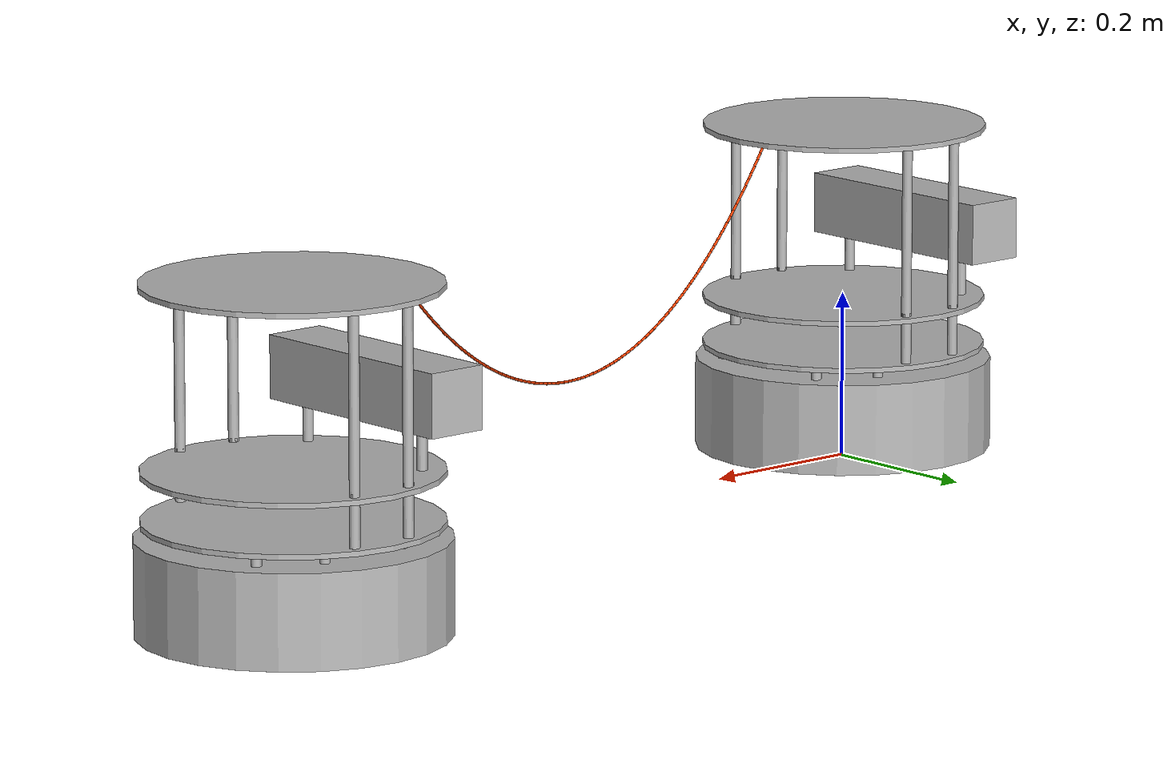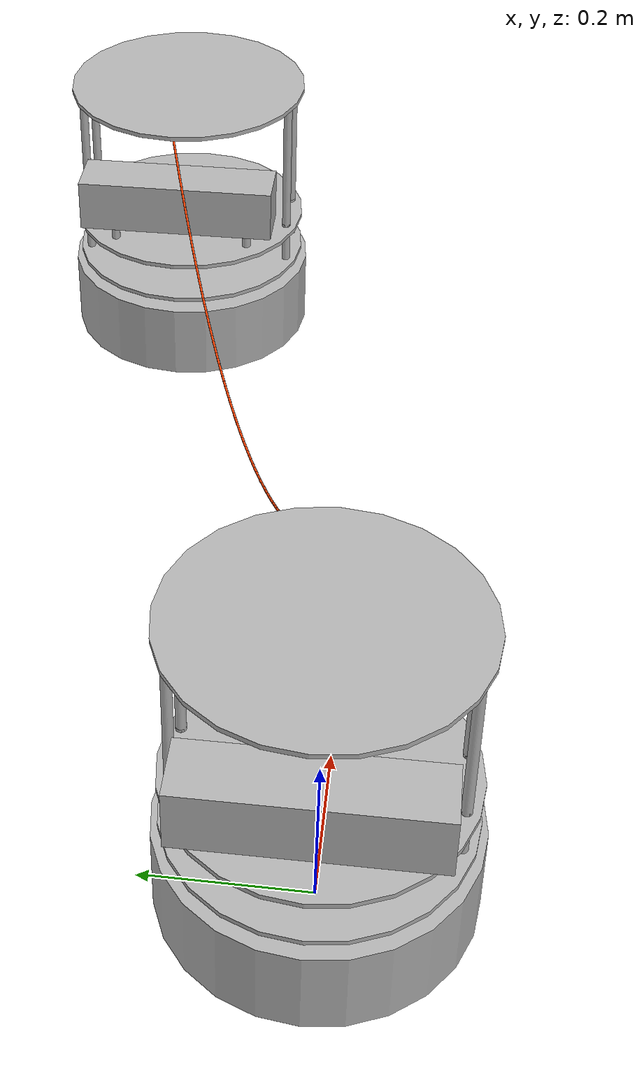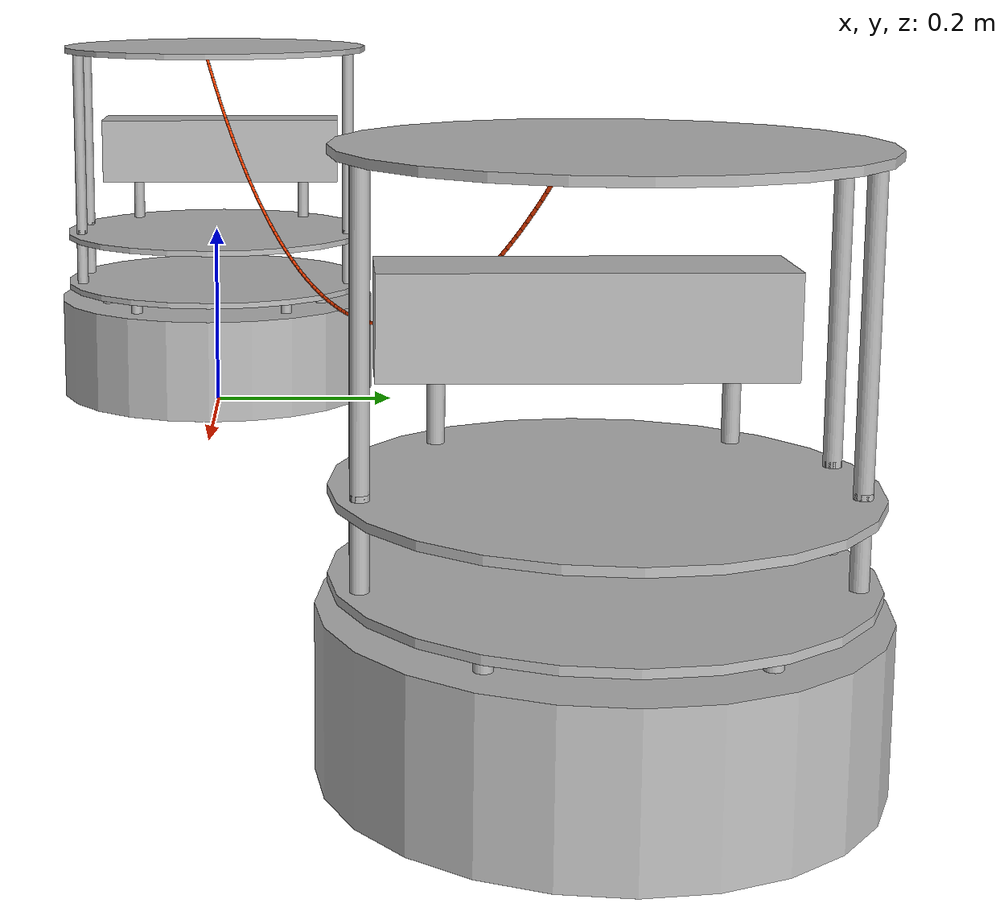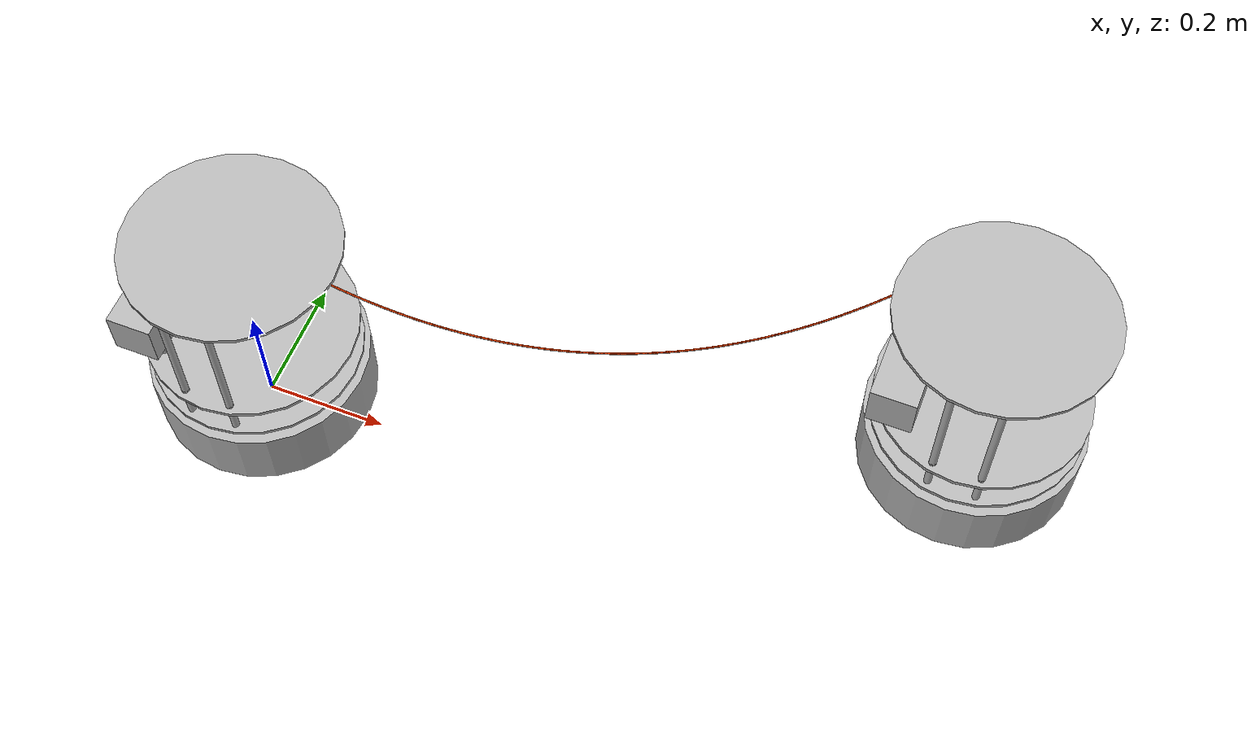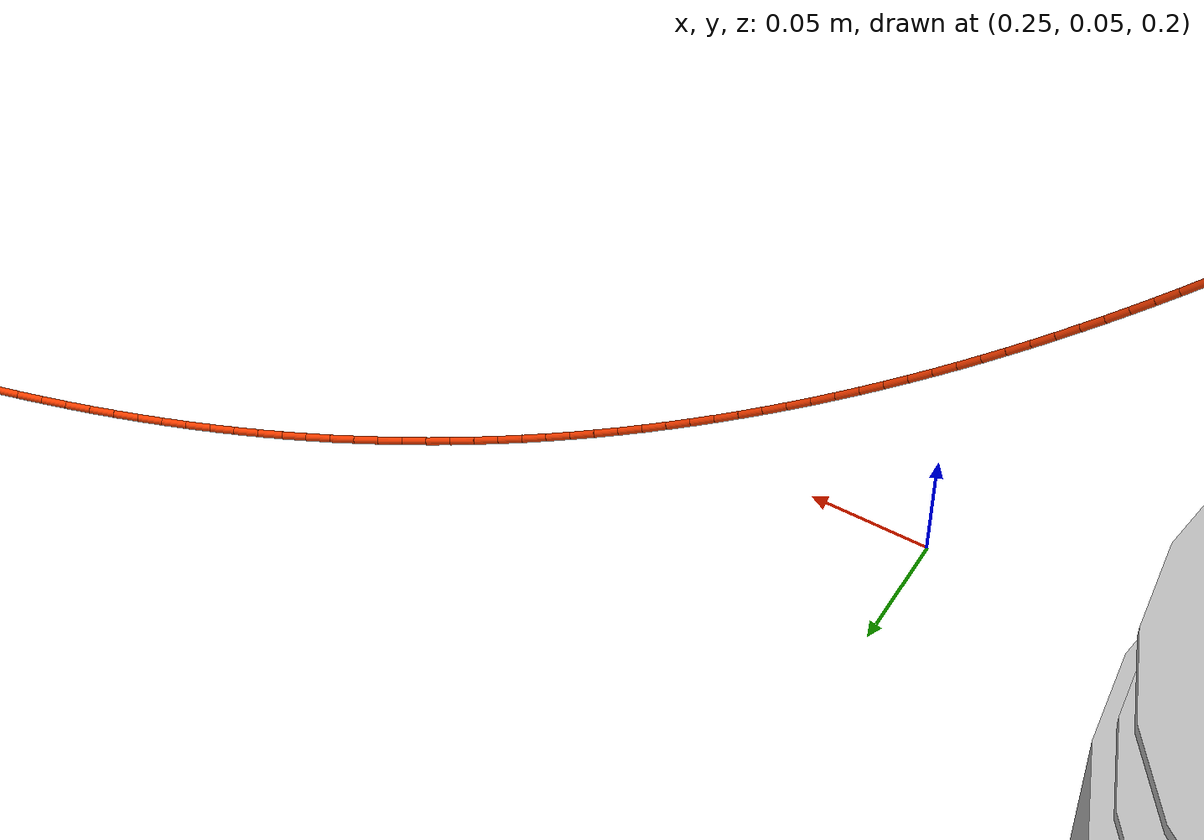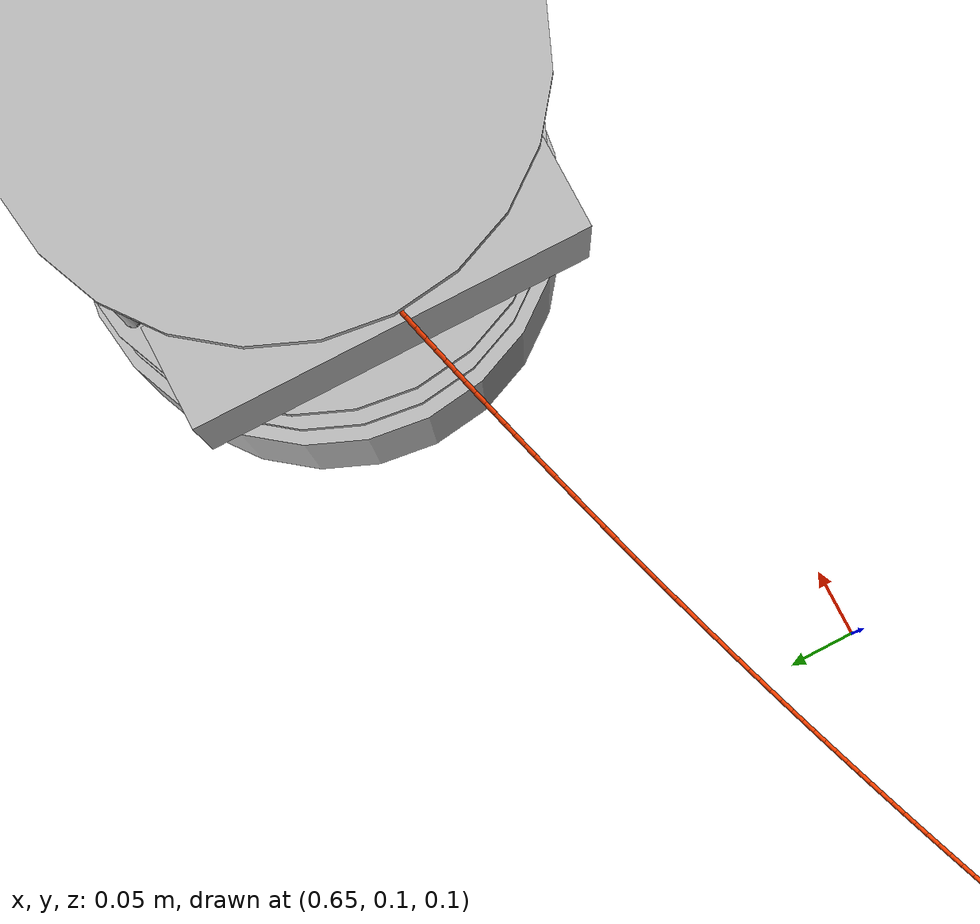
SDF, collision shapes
<?xml version="1.0" ?>
<sdf version="1.4">
  <model name="tethered_turtlebots">
-    <plugin name="p3d_turtle1" filename="libgazebo_ros_p3d.so">
-      <alwaysOn>true</alwaysOn>
-      <updateRate>30.0</updateRate>
-      <bodyName>base_foot1print</bodyName>
-      <topicName>turtle1/base_link/pose</topicName>
-      <gaussianNoise>0.01</gaussianNoise>
-      <frameName>world</frameName>
-      <xyzOffsets>0 0 0</xyzOffsets>
-      <rpyOffsets>0 0 0</rpyOffsets>
-    </plugin>
-    <plugin name="p3d_turtle2" filename="libgazebo_ros_p3d.so">
-      <alwaysOn>true</alwaysOn>
-      <updateRate>30.0</updateRate>
-      <bodyName>base_foot2print</bodyName>
-      <topicName>turtle2/base_link/pose</topicName>
-      <gaussianNoise>0.01</gaussianNoise>
-      <frameName>world</frameName>
-      <xyzOffsets>0 0 0</xyzOffsets>
-      <rpyOffsets>0 0 0</rpyOffsets>
-    </plugin>
-    <plugin name="p3d_tether" filename="libgazebo_ros_p3d.so">
-      <alwaysOn>true</alwaysOn>
-      <updateRate>30.0</updateRate>
-      <bodyName>link_49</bodyName>
-      <topicName>tether/middle_link/pose</topicName>
-      <gaussianNoise>0.01</gaussianNoise>
-      <frameName>world</frameName>
-      <xyzOffsets>0 0 0</xyzOffsets>
-      <rpyOffsets>0 0 0</rpyOffsets>
-    </plugin>
 	<!-- TURTLEBOT 1 -->
      <link name="base_foot1print">
		<pose>1.10613272858 0.298678786296 0.0 0.0 0.0 0.0</pose>
        <inertial>
          <pose>0.00947362 2.50779e-05 0.014919 0 -0 0</pose>
          <mass>2.4723</mass>
          <inertia>
            <ixx>0.0578436</ixx>
            <ixy>-2.91646e-06</ixy>
            <ixz>0.000317338</ixz>
            <iyy>0.0579316</iyy>
            <iyz>-9.59821e-07</iyz>
            <izz>0.0719963</izz>
          </inertia>
        </inertial>
        <collision name="base_foot1print_collision_base_link">
          <pose>0 0 0.06969 0 -0 0</pose>
          <geometry>
            <cylinder>
              <length>0.10938</length>
              <radius>0.178</radius>
            </cylinder>
          </geometry>
          <surface>
            <contact>
              <ode/>
            </contact>
            <friction>
              <ode>
                <mu>0.3</mu>
                <mu2>0.3</mu2>
              </ode>
            </friction>
            <bounce/>
          </surface>
          <max_contacts>10</max_contacts>
        </collision>
        <collision name="base_foot1print_collision_camera_link">
          <pose>-0.118 0 0.2812 0 -0 0</pose>
          <geometry>
            <box>
              <size>0.07271 0.27794 0.073</size>
            </box>
          </geometry>
          <surface>
            <contact>
              <ode/>
            </contact>
            <friction>
              <ode/>
            </friction>
            <bounce/>
          </surface>
          <max_contacts>10</max_contacts>
        </collision>
        <collision name="base_foot1print_collision_caster_back_link">
          <pose>-0.135 0 0.0192 -1.5708 0 0</pose>
          <geometry>
            <cylinder>
              <length>0.0176</length>
              <radius>0.017</radius>
            </cylinder>
          </geometry>
          <surface>
            <contact>
              <ode>
                <kp>1e+06</kp>
                <kd>100</kd>
                <max_vel>1</max_vel>
                <min_depth>0.001</min_depth>
              </ode>
            </contact>
            <friction>
              <ode>
                <mu>0</mu>
                <mu2>0</mu2>
              </ode>
            </friction>
            <bounce/>
          </surface>
          <max_contacts>10</max_contacts>
        </collision>
        <collision name="base_foot1print_collision_caster_front_link">
          <pose>0.115 0 0.0172 -1.5708 0 0</pose>
          <geometry>
            <cylinder>
              <length>0.0176</length>
              <radius>0.017</radius>
            </cylinder>
          </geometry>
          <surface>
            <contact>
              <ode>
                <kp>1e+06</kp>
                <kd>100</kd>
                <max_vel>1</max_vel>
                <min_depth>0.001</min_depth>
              </ode>
            </contact>
            <friction>
              <ode>
                <mu>0</mu>
                <mu2>0</mu2>
              </ode>
            </friction>
            <bounce/>
          </surface>
          <max_contacts>10</max_contacts>
        </collision>
        <collision name="base_foot1print_collision_plate_bottom_link">
          <pose>0 0 0.1408 0 -0 0</pose>
          <geometry>
            <cylinder>
              <length>0.006</length>
              <radius>0.17</radius>
            </cylinder>
          </geometry>
          <max_contacts>10</max_contacts>
          <surface>
            <bounce/>
            <friction>
              <ode/>
            </friction>
            <contact>
              <ode/>
            </contact>
          </surface>
        </collision>
        <collision name="base_foot1print_collision_plate_middle_link">
          <pose>0 0 0.1976 0 -0 0</pose>
          <geometry>
            <cylinder>
              <length>0.006</length>
              <radius>0.17</radius>
            </cylinder>
          </geometry>
          <max_contacts>10</max_contacts>
          <surface>
            <bounce/>
            <friction>
              <ode/>
            </friction>
            <contact>
              <ode/>
            </contact>
          </surface>
        </collision>
        <collision name="base_foot1print_collision_plate_top_link">
          <pose>0 0 0.4068 0 -0 0</pose>
          <geometry>
            <cylinder>
              <length>0.006</length>
              <radius>0.17</radius>
            </cylinder>
          </geometry>
          <max_contacts>10</max_contacts>
          <surface>
            <bounce/>
            <friction>
              <ode/>
            </friction>
            <contact>
              <ode/>
            </contact>
          </surface>
        </collision>
        <collision name="base_foot1print_collision_pole_bottom_0_link">
          <pose>0.12 0.082 0.113 0 -0 0</pose>
          <geometry>
            <cylinder>
              <length>0.0492</length>
              <radius>0.006</radius>
            </cylinder>
          </geometry>
          <max_contacts>10</max_contacts>
          <surface>
            <bounce/>
            <friction>
              <ode/>
            </friction>
            <contact>
              <ode/>
            </contact>
          </surface>
        </collision>
        <collision name="base_foot1print_collision_pole_bottom_1_link">
          <pose>0.055 0.12 0.113 0 -0 0</pose>
          <geometry>
            <cylinder>
              <length>0.0492</length>
              <radius>0.006</radius>
            </cylinder>
          </geometry>
          <max_contacts>10</max_contacts>
          <surface>
            <bounce/>
            <friction>
              <ode/>
            </friction>
            <contact>
              <ode/>
            </contact>
          </surface>
        </collision>
        <collision name="base_foot1print_collision_pole_bottom_2_link">
          <pose>-0.055 0.12 0.113 0 -0 0</pose>
          <geometry>
            <cylinder>
              <length>0.0492</length>
              <radius>0.006</radius>
            </cylinder>
          </geometry>
          <max_contacts>10</max_contacts>
          <surface>
            <bounce/>
            <friction>
              <ode/>
            </friction>
            <contact>
              <ode/>
            </contact>
          </surface>
        </collision>
        <collision name="base_foot1print_collision_pole_bottom_3_link">
          <pose>0.12 -0.082 0.113 0 -0 0</pose>
          <geometry>
            <cylinder>
              <length>0.0492</length>
              <radius>0.006</radius>
            </cylinder>
          </geometry>
          <max_contacts>10</max_contacts>
          <surface>
            <bounce/>
            <friction>
              <ode/>
            </friction>
            <contact>
              <ode/>
            </contact>
          </surface>
        </collision>
        <collision name="base_foot1print_collision_pole_bottom_4_link">
          <pose>0.055 -0.12 0.113 0 -0 0</pose>
          <geometry>
            <cylinder>
              <length>0.0492</length>
              <radius>0.006</radius>
            </cylinder>
          </geometry>
          <max_contacts>10</max_contacts>
          <surface>
            <bounce/>
            <friction>
              <ode/>
            </friction>
            <contact>
              <ode/>
            </contact>
          </surface>
        </collision>
        <collision name="base_foot1print_collision_pole_bottom_5_link">
          <pose>-0.055 -0.12 0.113 0 -0 0</pose>
          <geometry>
            <cylinder>
              <length>0.0492</length>
              <radius>0.006</radius>
            </cylinder>
          </geometry>
          <max_contacts>10</max_contacts>
          <surface>
            <bounce/>
            <friction>
              <ode/>
            </friction>
            <contact>
              <ode/>
            </contact>
          </surface>
        </collision>
        <collision name="base_foot1print_collision_pole_kinect_0_link">
          <pose>-0.1024 0.098 0.2474 0 -0 0</pose>
          <geometry>
            <cylinder>
              <length>0.0936</length>
              <radius>0.006</radius>
            </cylinder>
          </geometry>
          <max_contacts>10</max_contacts>
          <surface>
            <bounce/>
            <friction>
              <ode/>
            </friction>
            <contact>
              <ode/>
            </contact>
          </surface>
        </collision>
        <collision name="base_foot1print_collision_pole_kinect_1_link">
          <pose>-0.1024 -0.098 0.2474 0 -0 0</pose>
          <geometry>
            <cylinder>
              <length>0.0936</length>
              <radius>0.006</radius>
            </cylinder>
          </geometry>
          <max_contacts>10</max_contacts>
          <surface>
            <bounce/>
            <friction>
              <ode/>
            </friction>
            <contact>
              <ode/>
            </contact>
          </surface>
        </collision>
        <collision name="base_foot1print_collision_pole_middle_0_link">
          <pose>0.0381 0.1505 0.1742 0 -0 0</pose>
          <geometry>
            <cylinder>
              <length>0.0608</length>
              <radius>0.006</radius>
            </cylinder>
          </geometry>
          <max_contacts>10</max_contacts>
          <surface>
            <bounce/>
            <friction>
              <ode/>
            </friction>
            <contact>
              <ode/>
            </contact>
          </surface>
        </collision>
        <collision name="base_foot1print_collision_pole_middle_1_link">
          <pose>0.0381 -0.1505 0.1742 0 -0 0</pose>
          <geometry>
            <cylinder>
              <length>0.0608</length>
              <radius>0.006</radius>
            </cylinder>
          </geometry>
          <max_contacts>10</max_contacts>
          <surface>
            <bounce/>
            <friction>
              <ode/>
            </friction>
            <contact>
              <ode/>
            </contact>
          </surface>
        </collision>
        <collision name="base_foot1print_collision_pole_middle_2_link">
          <pose>-0.0381 0.1505 0.1742 0 -0 0</pose>
          <geometry>
            <cylinder>
              <length>0.0608</length>
              <radius>0.006</radius>
            </cylinder>
          </geometry>
          <max_contacts>10</max_contacts>
          <surface>
            <bounce/>
            <friction>
              <ode/>
            </friction>
            <contact>
              <ode/>
            </contact>
          </surface>
        </collision>
        <collision name="base_foot1print_collision_pole_middle_3_link">
          <pose>-0.0381 -0.1505 0.1742 0 -0 0</pose>
          <geometry>
            <cylinder>
              <length>0.0608</length>
              <radius>0.006</radius>
            </cylinder>
          </geometry>
          <max_contacts>10</max_contacts>
          <surface>
            <bounce/>
            <friction>
              <ode/>
            </friction>
            <contact>
              <ode/>
            </contact>
          </surface>
        </collision>
        <collision name="base_foot1print_collision_pole_top_0_link">
          <pose>0.0381 0.1505 0.3022 0 -0 0</pose>
          <geometry>
            <cylinder>
              <length>0.2032</length>
              <radius>0.006</radius>
            </cylinder>
          </geometry>
          <max_contacts>10</max_contacts>
          <surface>
            <bounce/>
            <friction>
              <ode/>
            </friction>
            <contact>
              <ode/>
            </contact>
          </surface>
        </collision>
        <collision name="base_foot1print_collision_pole_top_1_link">
          <pose>0.0381 -0.1505 0.3022 0 -0 0</pose>
          <geometry>
            <cylinder>
              <length>0.2032</length>
              <radius>0.006</radius>
            </cylinder>
          </geometry>
          <max_contacts>10</max_contacts>
          <surface>
            <bounce/>
            <friction>
              <ode/>
            </friction>
            <contact>
              <ode/>
            </contact>
          </surface>
        </collision>
        <collision name="base_foot1print_collision_pole_top_2_link">
          <pose>-0.0381 0.1505 0.3022 0 -0 0</pose>
          <geometry>
            <cylinder>
              <length>0.2032</length>
              <radius>0.006</radius>
            </cylinder>
          </geometry>
          <max_contacts>10</max_contacts>
          <surface>
            <bounce/>
            <friction>
              <ode/>
            </friction>
            <contact>
              <ode/>
            </contact>
          </surface>
        </collision>
        <collision name="base_foot1print_collision_pole_top_3_link">
          <pose>-0.0381 -0.1505 0.3022 0 -0 0</pose>
          <geometry>
            <cylinder>
              <length>0.2032</length>
              <radius>0.006</radius>
            </cylinder>
          </geometry>
          <max_contacts>10</max_contacts>
          <surface>
            <bounce/>
            <friction>
              <ode/>
            </friction>
            <contact>
              <ode/>
            </contact>
          </surface>
        </collision>
        <visual name="base_foot1print_visual_base_link">
          <pose>0.001 0 0.06219 0 -0 0</pose>
          <geometry>
            <mesh>
              <scale>1 1 1</scale>
              <uri>/opt/ros/indigo/share/kobuki_description/meshes/main_body.dae</uri>
            </mesh>
          </geometry>
        </visual>
        <visual name="base_foot1print_visual_camera_link">
          <pose>-0.118 0 0.2812 0 -0 1.5708</pose>
          <geometry>
            <mesh>
              <scale>1 1 1</scale>
              <uri>/opt/ros/indigo/share/turtlebot_description/meshes/sensors/kinect.dae</uri>
            </mesh>
          </geometry>
        </visual>
        <visual name="base_foot1print_visual_plate_bottom_link">
          <pose>0.02364 0 0.1408 0 -0 0</pose>
          <geometry>
            <mesh>
              <scale>1 1 1</scale>
              <uri>/opt/ros/indigo/share/turtlebot_description/meshes/stacks/hexagons/plate_bottom.dae</uri>
            </mesh>
          </geometry>
        </visual>
        <visual name="base_foot1print_visual_plate_middle_link">
          <pose>-0.01364 0 0.1976 0 -0 0</pose>
          <geometry>
            <mesh>
              <scale>1 1 1</scale>
              <uri>/opt/ros/indigo/share/turtlebot_description/meshes/stacks/hexagons/plate_middle.dae</uri>
            </mesh>
          </geometry>
        </visual>
        <visual name="base_foot1print_visual_plate_top_link">
          <pose>-0.01364 0 0.4068 0 -0 0</pose>
          <geometry>
            <mesh>
              <scale>1 1 1</scale>
              <uri>/opt/ros/indigo/share/turtlebot_description/meshes/stacks/hexagons/plate_top.dae</uri>
            </mesh>
          </geometry>
        </visual>
        <visual name="base_foot1print_visual_pole_bottom_0_link">
          <pose>0.12 0.082 0.113 0 -0 0</pose>
          <geometry>
            <mesh>
              <scale>1 1 1</scale>
              <uri>/opt/ros/indigo/share/turtlebot_description/meshes/stacks/hexagons/pole_bottom.dae</uri>
            </mesh>
          </geometry>
        </visual>
        <visual name="base_foot1print_visual_pole_bottom_1_link">
          <pose>0.055 0.12 0.113 0 -0 0</pose>
          <geometry>
            <mesh>
              <scale>1 1 1</scale>
              <uri>/opt/ros/indigo/share/turtlebot_description/meshes/stacks/hexagons/pole_bottom.dae</uri>
            </mesh>
          </geometry>
        </visual>
        <visual name="base_foot1print_visual_pole_bottom_2_link">
          <pose>-0.055 0.12 0.113 0 -0 0</pose>
          <geometry>
            <mesh>
              <scale>1 1 1</scale>
              <uri>/opt/ros/indigo/share/turtlebot_description/meshes/stacks/hexagons/pole_bottom.dae</uri>
            </mesh>
          </geometry>
        </visual>
        <visual name="base_foot1print_visual_pole_bottom_3_link">
          <pose>0.12 -0.082 0.113 0 -0 0</pose>
          <geometry>
            <mesh>
              <scale>1 1 1</scale>
              <uri>/opt/ros/indigo/share/turtlebot_description/meshes/stacks/hexagons/pole_bottom.dae</uri>
            </mesh>
          </geometry>
        </visual>
        <visual name="base_foot1print_visual_pole_bottom_4_link">
          <pose>0.055 -0.12 0.113 0 -0 0</pose>
          <geometry>
            <mesh>
              <scale>1 1 1</scale>
              <uri>/opt/ros/indigo/share/turtlebot_description/meshes/stacks/hexagons/pole_bottom.dae</uri>
            </mesh>
          </geometry>
        </visual>
        <visual name="base_foot1print_visual_pole_bottom_5_link">
          <pose>-0.055 -0.12 0.113 0 -0 0</pose>
          <geometry>
            <mesh>
              <scale>1 1 1</scale>
              <uri>/opt/ros/indigo/share/turtlebot_description/meshes/stacks/hexagons/pole_bottom.dae</uri>
            </mesh>
          </geometry>
        </visual>
        <visual name="base_foot1print_visual_pole_kinect_0_link">
          <pose>-0.1024 0.098 0.2474 0 -0 0</pose>
          <geometry>
            <mesh>
              <scale>1 1 1</scale>
              <uri>/opt/ros/indigo/share/turtlebot_description/meshes/stacks/hexagons/pole_kinect.dae</uri>
            </mesh>
          </geometry>
        </visual>
        <visual name="base_foot1print_visual_pole_kinect_1_link">
          <pose>-0.1024 -0.098 0.2474 0 -0 0</pose>
          <geometry>
            <mesh>
              <scale>1 1 1</scale>
              <uri>/opt/ros/indigo/share/turtlebot_description/meshes/stacks/hexagons/pole_kinect.dae</uri>
            </mesh>
          </geometry>
        </visual>
        <visual name="base_foot1print_visual_pole_middle_0_link">
          <pose>0.0381 0.1505 0.1742 3.14159 -2.06823e-13 3.14159</pose>
          <geometry>
            <mesh>
              <scale>1 1 1</scale>
              <uri>/opt/ros/indigo/share/turtlebot_description/meshes/stacks/hexagons/pole_middle.dae</uri>
            </mesh>
          </geometry>
        </visual>
        <visual name="base_foot1print_visual_pole_middle_1_link">
          <pose>0.0381 -0.1505 0.1742 3.14159 -2.06823e-13 3.14159</pose>
          <geometry>
            <mesh>
              <scale>1 1 1</scale>
              <uri>/opt/ros/indigo/share/turtlebot_description/meshes/stacks/hexagons/pole_middle.dae</uri>
            </mesh>
          </geometry>
        </visual>
        <visual name="base_foot1print_visual_pole_middle_2_link">
          <pose>-0.0381 0.1505 0.1742 3.14159 -2.06823e-13 3.14159</pose>
          <geometry>
            <mesh>
              <scale>1 1 1</scale>
              <uri>/opt/ros/indigo/share/turtlebot_description/meshes/stacks/hexagons/pole_middle.dae</uri>
            </mesh>
          </geometry>
        </visual>
        <visual name="base_foot1print_visual_pole_middle_3_link">
          <pose>-0.0381 -0.1505 0.1742 3.14159 -2.06823e-13 3.14159</pose>
          <geometry>
            <mesh>
              <scale>1 1 1</scale>
              <uri>/opt/ros/indigo/share/turtlebot_description/meshes/stacks/hexagons/pole_middle.dae</uri>
            </mesh>
          </geometry>
        </visual>
        <visual name="base_foot1print_visual_pole_top_0_link">
          <pose>0.0381 0.1505 0.3022 0 -0 0</pose>
          <geometry>
            <mesh>
              <scale>1 1 1</scale>
              <uri>/opt/ros/indigo/share/turtlebot_description/meshes/stacks/hexagons/pole_top.dae</uri>
            </mesh>
          </geometry>
        </visual>
        <visual name="base_foot1print_visual_pole_top_1_link">
          <pose>0.0381 -0.1505 0.3022 0 -0 0</pose>
          <geometry>
            <mesh>
              <scale>1 1 1</scale>
              <uri>/opt/ros/indigo/share/turtlebot_description/meshes/stacks/hexagons/pole_top.dae</uri>
            </mesh>
          </geometry>
        </visual>
        <visual name="base_foot1print_visual_pole_top_2_link">
          <pose>-0.0381 0.1505 0.3022 0 -0 0</pose>
          <geometry>
            <mesh>
              <scale>1 1 1</scale>
              <uri>/opt/ros/indigo/share/turtlebot_description/meshes/stacks/hexagons/pole_top.dae</uri>
            </mesh>
          </geometry>
        </visual>
        <visual name="base_foot1print_visual_pole_top_3_link">
          <pose>-0.0381 -0.1505 0.3022 0 -0 0</pose>
          <geometry>
            <mesh>
              <scale>1 1 1</scale>
              <uri>/opt/ros/indigo/share/turtlebot_description/meshes/stacks/hexagons/pole_top.dae</uri>
            </mesh>
          </geometry>
        </visual>
        <velocity_decay>
          <linear>0</linear>
          <angular>0</angular>
        </velocity_decay>
        <sensor name="bumpers" type="contact">
          <always_on>1</always_on>
          <update_rate>50</update_rate>
          <visualize>1</visualize>
          <contact>
            <collision>base_foot1print_collision_base_link</collision>
            <topic>__default_topic__</topic>
          </contact>
          <pose>0 0 0.0102 0 -0 0</pose>
        </sensor>
        <velocity_decay>
          <linear>0</linear>
          <angular>0</angular>
        </velocity_decay>
        <sensor name="camera" type="depth">
          <always_on>1</always_on>
          <update_rate>20</update_rate>
          <camera name="__default__">
            <horizontal_fov>1.0472</horizontal_fov>
            <image>
              <format>R8G8B8</format>
              <width>640</width>
              <height>480</height>
            </image>
            <clip>
              <near>0.05</near>
              <far>8</far>
            </clip>
          </camera>
          <plugin name="kinect_camera_controller" filename="libgazebo_ros_openni_kinect.so">
            <robotNamespace>/turtle1</robotNamespace>
            <cameraName>camera</cameraName>
            <alwaysOn>true</alwaysOn>
            <updateRate>30</updateRate>
            <imageTopicName>rgb/image_raw</imageTopicName>
            <depthImageTopicName>depth/image_raw</depthImageTopicName>
            <pointCloudTopicName>depth/points</pointCloudTopicName>
            <cameraInfoTopicName>rgb/camera_info</cameraInfoTopicName>
            <depthImageCameraInfoTopicName>depth/camera_info</depthImageCameraInfoTopicName>
            <frameName>camera_depth_optical_frame</frameName>
            <baseline>0.1</baseline>
            <distortion_k1>0.0</distortion_k1>
            <distortion_k2>0.0</distortion_k2>
            <distortion_k3>0.0</distortion_k3>
            <distortion_t1>0.0</distortion_t1>
            <distortion_t2>0.0</distortion_t2>
            <pointCloudCutoff>0.4</pointCloudCutoff>
          </plugin>
          <pose>-0.118 0.0 0.2812 0 -0 0</pose>
        </sensor>
        <velocity_decay>
          <linear>0</linear>
          <angular>0</angular>
        </velocity_decay>
        <velocity_decay>
          <linear>0</linear>
          <angular>0</angular>
        </velocity_decay>
        <velocity_decay>
          <linear>0</linear>
          <angular>0</angular>
        </velocity_decay>
        <sensor name="cliff_sensor_front" type="ray">
          <always_on>1</always_on>
          <update_rate>50</update_rate>
          <visualize>1</visualize>
          <ray>
            <scan>
              <horizontal>
                <samples>50</samples>
                <resolution>1</resolution>
                <min_angle>-0.0436</min_angle>
                <max_angle>0.0436</max_angle>
              </horizontal>
            </scan>
            <range>
              <min>0.01</min>
              <max>0.15</max>
              <resolution>1</resolution>
            </range>
          </ray>
          <pose>0.156 0 0.0316 3.14159 1.57079 3.14159</pose>
        </sensor>
        <velocity_decay>
          <linear>0</linear>
          <angular>0</angular>
        </velocity_decay>
        <sensor name="cliff_sensor_left" type="ray">
          <always_on>1</always_on>
          <update_rate>50</update_rate>
          <visualize>1</visualize>
          <ray>
            <scan>
              <horizontal>
                <samples>50</samples>
                <resolution>1</resolution>
                <min_angle>-0.0436</min_angle>
                <max_angle>0.0436</max_angle>
              </horizontal>
            </scan>
            <range>
              <min>0.01</min>
              <max>0.15</max>
              <resolution>1</resolution>
            </range>
          </ray>
          <pose>0.08734 0.13601 0.0316 3.14159 1.57079 3.14159</pose>
        </sensor>
        <velocity_decay>
          <linear>0</linear>
          <angular>0</angular>
        </velocity_decay>
        <sensor name="cliff_sensor_right" type="ray">
          <always_on>1</always_on>
          <update_rate>50</update_rate>
          <visualize>1</visualize>
          <ray>
            <scan>
              <horizontal>
                <samples>50</samples>
                <resolution>1</resolution>
                <min_angle>-0.0436</min_angle>
                <max_angle>0.0436</max_angle>
              </horizontal>
            </scan>
            <range>
              <min>0.01</min>
              <max>0.15</max>
              <resolution>1</resolution>
            </range>
          </ray>
          <pose>0.085 -0.13601 0.0316 3.14159 1.57079 3.14159</pose>
        </sensor>
        <gravity>1</gravity>
        <velocity_decay>
          <linear>0</linear>
          <angular>0</angular>
        </velocity_decay>
        <self_collide>0</self_collide>
        <sensor name="imu" type="imu">
          <always_on>1</always_on>
          <update_rate>50</update_rate>
          <visualize>0</visualize>
          <imu>
            <noise>
              <type>gaussian</type>
              <rate>
                <mean>0</mean>
                <stddev>1.96e-06</stddev>
                <bias_mean>0</bias_mean>
                <bias_stddev>0</bias_stddev>
              </rate>
              <accel>
                <mean>0</mean>
                <stddev>0.017</stddev>
                <bias_mean>0.1</bias_mean>
                <bias_stddev>0.001</bias_stddev>
              </accel>
            </noise>
          </imu>
          <pose>0.056 0.062 0.0304 0 -0 0</pose>
        </sensor>
        <kinematic>0</kinematic>
      </link>
      <link name="wheel1_left_link">
		<pose>1.10613272858 0.413678786296 0.0352 -1.5708 0.0 0.0</pose>
        <inertial>
          <pose>0 0 0 0 -0 0</pose>
          <mass>0.01</mass>
          <inertia>
            <ixx>0.001</ixx>
            <ixy>0</ixy>
            <ixz>0</ixz>
            <iyy>0.001</iyy>
            <iyz>0</iyz>
            <izz>0.001</izz>
          </inertia>
        </inertial>
        <collision name="wheel1_left_link_collision">
          <pose>0 0 0 0 -0 0</pose>
          <geometry>
            <cylinder>
              <length>0.0206</length>
              <radius>0.0352</radius>
            </cylinder>
          </geometry>
          <surface>
            <contact>
              <ode>
                <kp>1e+06</kp>
                <kd>100</kd>
                <max_vel>1</max_vel>
                <min_depth>0.001</min_depth>
              </ode>
            </contact>
            <friction>
              <ode>
                <mu>1</mu>
                <mu2>1</mu2>
              </ode>
            </friction>
            <bounce/>
          </surface>
          <max_contacts>10</max_contacts>
        </collision>
        <visual name="wheel1_left_link_visual">
          <pose>0 0 0 0 -0 0</pose>
          <geometry>
            <mesh>
              <scale>1 1 1</scale>
              <uri>/opt/ros/indigo/share/kobuki_description/meshes/wheel.dae</uri>
            </mesh>
          </geometry>
        </visual>
        <gravity>1</gravity>
        <velocity_decay>
          <linear>0</linear>
          <angular>0</angular>
        </velocity_decay>
        <self_collide>0</self_collide>
        <kinematic>0</kinematic>
      </link>
      <joint name="wheel1_left_joint" type="revolute">
        <child>wheel1_left_link</child>
        <parent>base_foot1print</parent>
        <axis>
          <xyz>0 1 0</xyz>
          <limit>
            <lower>-1e+16</lower>
            <upper>1e+16</upper>
          </limit>
        </axis>
      </joint>
      <link name="wheel1_right_link">
		<pose>1.10613272858 0.183678786296 0.0352 -1.5708 0.0 0.0</pose>
        <inertial>
          <pose>0 0 0 0 -0 0</pose>
          <mass>0.01</mass>
          <inertia>
            <ixx>0.001</ixx>
            <ixy>0</ixy>
            <ixz>0</ixz>
            <iyy>0.001</iyy>
            <iyz>0</iyz>
            <izz>0.001</izz>
          </inertia>
        </inertial>
        <collision name="wheel1_right_link_collision">
          <pose>0 0 0 0 -0 0</pose>
          <geometry>
            <cylinder>
              <length>0.0206</length>
              <radius>0.035</radius>
            </cylinder>
          </geometry>
          <surface>
            <contact>
              <ode>
                <kp>1e+06</kp>
                <kd>100</kd>
                <max_vel>1</max_vel>
                <min_depth>0.001</min_depth>
              </ode>
            </contact>
            <friction>
              <ode>
                <mu>1</mu>
                <mu2>1</mu2>
              </ode>
            </friction>
            <bounce/>
          </surface>
          <max_contacts>10</max_contacts>
        </collision>
        <visual name="wheel1_right_link_visual">
          <pose>0 0 0 0 -0 0</pose>
          <geometry>
            <mesh>
              <scale>1 1 1</scale>
              <uri>/opt/ros/indigo/share/kobuki_description/meshes/wheel.dae</uri>
            </mesh>
          </geometry>
        </visual>
        <gravity>1</gravity>
        <velocity_decay>
          <linear>0</linear>
          <angular>0</angular>
        </velocity_decay>
        <self_collide>0</self_collide>
        <kinematic>0</kinematic>
      </link>
      <joint name="wheel1_right_joint" type="revolute">
        <child>wheel1_right_link</child>
        <parent>base_foot1print</parent>
        <axis>
          <xyz>0 1 0</xyz>
          <limit>
            <lower>-1e+16</lower>
            <upper>1e+16</upper>
          </limit>
        </axis>
      </joint>
      <static>0</static>
      <plugin name="kobuki1_controller" filename="libgazebo_ros_diff_drive.so">
        <leftJoint>wheel1_right_joint</leftJoint>
        <rightJoint>wheel1_left_joint</rightJoint>
        <wheelSeparation>.230</wheelSeparation>
        <wheelDiameter>0.070</wheelDiameter>
        <wheelTorque>1.0</wheelTorque>
        <velocity_command_timeout>0.6</velocity_command_timeout>
        <cliff_sensor_left_name>cliff_sensor_left</cliff_sensor_left_name>
        <cliff_sensor_center_name>cliff_sensor_front</cliff_sensor_center_name>
        <cliff_sensor_right_name>cliff_sensor_right</cliff_sensor_right_name>
        <cliff_detection_threshold>0.04</cliff_detection_threshold>
        <bumper_name>bumpers</bumper_name>
        <imu_name>imu</imu_name>
        <robotBaseFrame>base_foot2print</robotBaseFrame>
        <publish_tf>1</publish_tf>
        <broadcasttf>1</broadcasttf>
        <commandTopic>cmd_vel</commandTopic>
        <odometryTopic>odom</odometryTopic>
        <odometryFrame>odom</odometryFrame>
		<legacyMode>true</legacyMode>
        <robotNamespace>/turtle1</robotNamespace>
      </plugin>
	  <!-- TURTLEBOT 2 -->
     <link name="base_foot2print">
		<pose>0.0 0.0 0.0 0.0 0.0 0.0</pose>
        <inertial>
          <pose>0.00947362 2.50779e-05 0.014919 0 -0 0</pose>
          <mass>2.4723</mass>
          <inertia>
            <ixx>0.0578436</ixx>
            <ixy>-2.91646e-06</ixy>
            <ixz>0.000317338</ixz>
            <iyy>0.0579316</iyy>
            <iyz>-9.59821e-07</iyz>
            <izz>0.0719963</izz>
          </inertia>
        </inertial>
        <collision name="base_foot2print_collision_base_link">
          <pose>0 0 0.06969 0 0 0</pose>
          <geometry>
            <cylinder>
              <length>0.10938</length>
              <radius>0.178</radius>
            </cylinder>
          </geometry>
          <surface>
            <contact>
              <ode/>
            </contact>
            <friction>
              <ode>
                <mu>0.3</mu>
                <mu2>0.3</mu2>
              </ode>
            </friction>
            <bounce/>
          </surface>
          <max_contacts>10</max_contacts>
        </collision>
        <collision name="base_foot2print_collision_camera_link">
          <pose>-0.118 0 0.2812 0 0 0</pose>
          <geometry>
            <box>
              <size>0.07271 0.27794 0.073</size>
            </box>
          </geometry>
          <surface>
            <contact>
              <ode/>
            </contact>
            <friction>
              <ode/>
            </friction>
            <bounce/>
          </surface>
          <max_contacts>10</max_contacts>
        </collision>
        <collision name="base_foot2print_collision_caster_back_link">
          <pose>-0.135 0 0.0192 -1.5708 0 0</pose>
          <geometry>
            <cylinder>
              <length>0.0176</length>
              <radius>0.017</radius>
            </cylinder>
          </geometry>
          <surface>
            <contact>
              <ode>
                <kp>1e+06</kp>
                <kd>100</kd>
                <max_vel>1</max_vel>
                <min_depth>0.001</min_depth>
              </ode>
            </contact>
            <friction>
              <ode>
                <mu>0</mu>
                <mu2>0</mu2>
              </ode>
            </friction>
            <bounce/>
          </surface>
          <max_contacts>10</max_contacts>
        </collision>
        <collision name="base_foot2print_collision_caster_front_link">
          <pose>0.115 0 0.0172 -1.5708 0 0</pose>
          <geometry>
            <cylinder>
              <length>0.0176</length>
              <radius>0.017</radius>
            </cylinder>
          </geometry>
          <surface>
            <contact>
              <ode>
                <kp>1e+06</kp>
                <kd>100</kd>
                <max_vel>1</max_vel>
                <min_depth>0.001</min_depth>
              </ode>
            </contact>
            <friction>
              <ode>
                <mu>0</mu>
                <mu2>0</mu2>
              </ode>
            </friction>
            <bounce/>
          </surface>
          <max_contacts>10</max_contacts>
        </collision>
        <collision name="base_foot2print_collision_plate_bottom_link">
          <pose>0 0 0.1408 0 -0 0</pose>
          <geometry>
            <cylinder>
              <length>0.006</length>
              <radius>0.17</radius>
            </cylinder>
          </geometry>
          <max_contacts>10</max_contacts>
          <surface>
            <bounce/>
            <friction>
              <ode/>
            </friction>
            <contact>
              <ode/>
            </contact>
          </surface>
        </collision>
        <collision name="base_foot2print_collision_plate_middle_link">
          <pose>0 0 0.1976 0 -0 0</pose>
          <geometry>
            <cylinder>
              <length>0.006</length>
              <radius>0.17</radius>
            </cylinder>
          </geometry>
          <max_contacts>10</max_contacts>
          <surface>
            <bounce/>
            <friction>
              <ode/>
            </friction>
            <contact>
              <ode/>
            </contact>
          </surface>
        </collision>
        <collision name="base_foot2print_collision_plate_top_link">
          <pose>0 0 0.4068 0 -0 0</pose>
          <geometry>
            <cylinder>
              <length>0.006</length>
              <radius>0.17</radius>
            </cylinder>
          </geometry>
          <max_contacts>10</max_contacts>
          <surface>
            <bounce/>
            <friction>
              <ode/>
            </friction>
            <contact>
              <ode/>
            </contact>
          </surface>
        </collision>
        <collision name="base_foot2print_collision_pole_bottom_0_link">
          <pose>0.12 0.082 0.113 0 -0 0</pose>
          <geometry>
            <cylinder>
              <length>0.0492</length>
              <radius>0.006</radius>
            </cylinder>
          </geometry>
          <max_contacts>10</max_contacts>
          <surface>
            <bounce/>
            <friction>
              <ode/>
            </friction>
            <contact>
              <ode/>
            </contact>
          </surface>
        </collision>
        <collision name="base_foot2print_collision_pole_bottom_1_link">
          <pose>0.055 0.12 0.113 0 -0 0</pose>
          <geometry>
            <cylinder>
              <length>0.0492</length>
              <radius>0.006</radius>
            </cylinder>
          </geometry>
          <max_contacts>10</max_contacts>
          <surface>
            <bounce/>
            <friction>
              <ode/>
            </friction>
            <contact>
              <ode/>
            </contact>
          </surface>
        </collision>
        <collision name="base_foot2print_collision_pole_bottom_2_link">
          <pose>-0.055 0.12 0.113 0 -0 0</pose>
          <geometry>
            <cylinder>
              <length>0.0492</length>
              <radius>0.006</radius>
            </cylinder>
          </geometry>
          <max_contacts>10</max_contacts>
          <surface>
            <bounce/>
            <friction>
              <ode/>
            </friction>
            <contact>
              <ode/>
            </contact>
          </surface>
        </collision>
        <collision name="base_foot2print_collision_pole_bottom_3_link">
          <pose>0.12 -0.082 0.113 0 -0 0</pose>
          <geometry>
            <cylinder>
              <length>0.0492</length>
              <radius>0.006</radius>
            </cylinder>
          </geometry>
          <max_contacts>10</max_contacts>
          <surface>
            <bounce/>
            <friction>
              <ode/>
            </friction>
            <contact>
              <ode/>
            </contact>
          </surface>
        </collision>
        <collision name="base_foot2print_collision_pole_bottom_4_link">
          <pose>0.055 -0.12 0.113 0 -0 0</pose>
          <geometry>
            <cylinder>
              <length>0.0492</length>
              <radius>0.006</radius>
            </cylinder>
          </geometry>
          <max_contacts>10</max_contacts>
          <surface>
            <bounce/>
            <friction>
              <ode/>
            </friction>
            <contact>
              <ode/>
            </contact>
          </surface>
        </collision>
        <collision name="base_foot2print_collision_pole_bottom_5_link">
          <pose>-0.055 -0.12 0.113 0 -0 0</pose>
          <geometry>
            <cylinder>
              <length>0.0492</length>
              <radius>0.006</radius>
            </cylinder>
          </geometry>
          <max_contacts>10</max_contacts>
          <surface>
            <bounce/>
            <friction>
              <ode/>
            </friction>
            <contact>
              <ode/>
            </contact>
          </surface>
        </collision>
        <collision name="base_foot2print_collision_pole_kinect_0_link">
          <pose>-0.1024 0.098 0.2474 0 -0 0</pose>
          <geometry>
            <cylinder>
              <length>0.0936</length>
              <radius>0.006</radius>
            </cylinder>
          </geometry>
          <max_contacts>10</max_contacts>
          <surface>
            <bounce/>
            <friction>
              <ode/>
            </friction>
            <contact>
              <ode/>
            </contact>
          </surface>
        </collision>
        <collision name="base_foot2print_collision_pole_kinect_1_link">
          <pose>-0.1024 -0.098 0.2474 0 -0 0</pose>
          <geometry>
            <cylinder>
              <length>0.0936</length>
              <radius>0.006</radius>
            </cylinder>
          </geometry>
          <max_contacts>10</max_contacts>
          <surface>
            <bounce/>
            <friction>
              <ode/>
            </friction>
            <contact>
              <ode/>
            </contact>
          </surface>
        </collision>
        <collision name="base_foot2print_collision_pole_middle_0_link">
          <pose>0.0381 0.1505 0.1742 0 -0 0</pose>
          <geometry>
            <cylinder>
              <length>0.0608</length>
              <radius>0.006</radius>
            </cylinder>
          </geometry>
          <max_contacts>10</max_contacts>
          <surface>
            <bounce/>
            <friction>
              <ode/>
            </friction>
            <contact>
              <ode/>
            </contact>
          </surface>
        </collision>
        <collision name="base_foot2print_collision_pole_middle_1_link">
          <pose>0.0381 -0.1505 0.1742 0 -0 0</pose>
          <geometry>
            <cylinder>
              <length>0.0608</length>
              <radius>0.006</radius>
            </cylinder>
          </geometry>
          <max_contacts>10</max_contacts>
          <surface>
            <bounce/>
            <friction>
              <ode/>
            </friction>
            <contact>
              <ode/>
            </contact>
          </surface>
        </collision>
        <collision name="base_foot2print_collision_pole_middle_2_link">
          <pose>-0.0381 0.1505 0.1742 0 -0 0</pose>
          <geometry>
            <cylinder>
              <length>0.0608</length>
              <radius>0.006</radius>
            </cylinder>
          </geometry>
          <max_contacts>10</max_contacts>
          <surface>
            <bounce/>
            <friction>
              <ode/>
            </friction>
            <contact>
              <ode/>
            </contact>
          </surface>
        </collision>
        <collision name="base_foot2print_collision_pole_middle_3_link">
          <pose>-0.0381 -0.1505 0.1742 0 -0 0</pose>
          <geometry>
            <cylinder>
              <length>0.0608</length>
              <radius>0.006</radius>
            </cylinder>
          </geometry>
          <max_contacts>10</max_contacts>
          <surface>
            <bounce/>
            <friction>
              <ode/>
            </friction>
            <contact>
              <ode/>
            </contact>
          </surface>
        </collision>
        <collision name="base_foot2print_collision_pole_top_0_link">
          <pose>0.0381 0.1505 0.3022 0 -0 0</pose>
          <geometry>
            <cylinder>
              <length>0.2032</length>
              <radius>0.006</radius>
            </cylinder>
          </geometry>
          <max_contacts>10</max_contacts>
          <surface>
            <bounce/>
            <friction>
              <ode/>
            </friction>
            <contact>
              <ode/>
            </contact>
          </surface>
        </collision>
        <collision name="base_foot2print_collision_pole_top_1_link">
          <pose>0.0381 -0.1505 0.3022 0 -0 0</pose>
          <geometry>
            <cylinder>
              <length>0.2032</length>
              <radius>0.006</radius>
            </cylinder>
          </geometry>
          <max_contacts>10</max_contacts>
          <surface>
            <bounce/>
            <friction>
              <ode/>
            </friction>
            <contact>
              <ode/>
            </contact>
          </surface>
        </collision>
        <collision name="base_foot2print_collision_pole_top_2_link">
          <pose>-0.0381 0.1505 0.3022 0 -0 0</pose>
          <geometry>
            <cylinder>
              <length>0.2032</length>
              <radius>0.006</radius>
            </cylinder>
          </geometry>
          <max_contacts>10</max_contacts>
          <surface>
            <bounce/>
            <friction>
              <ode/>
            </friction>
            <contact>
              <ode/>
            </contact>
          </surface>
        </collision>
        <collision name="base_foot2print_collision_pole_top_3_link">
          <pose>-0.0381 -0.1505 0.3022 0 -0 0</pose>
          <geometry>
            <cylinder>
              <length>0.2032</length>
              <radius>0.006</radius>
            </cylinder>
          </geometry>
          <max_contacts>10</max_contacts>
          <surface>
            <bounce/>
            <friction>
              <ode/>
            </friction>
            <contact>
              <ode/>
            </contact>
          </surface>
        </collision>
        <visual name="base_foot2print_visual_base_link">
          <pose>0.001 0 0.06219 0 -0 0</pose>
          <geometry>
            <mesh>
              <scale>1 1 1</scale>
              <uri>/opt/ros/indigo/share/kobuki_description/meshes/main_body.dae</uri>
            </mesh>
          </geometry>
        </visual>
        <visual name="base_foot2print_visual_camera_link">
          <pose>-0.118 0 0.2812 0 -0 1.5708</pose>
          <geometry>
            <mesh>
              <scale>1 1 1</scale>
              <uri>/opt/ros/indigo/share/turtlebot_description/meshes/sensors/kinect.dae</uri>
            </mesh>
          </geometry>
        </visual>
        <visual name="base_foot2print_visual_plate_bottom_link">
          <pose>0.02364 0 0.1408 0 -0 0</pose>
          <geometry>
            <mesh>
              <scale>1 1 1</scale>
              <uri>/opt/ros/indigo/share/turtlebot_description/meshes/stacks/hexagons/plate_bottom.dae</uri>
            </mesh>
          </geometry>
        </visual>
        <visual name="base_foot2print_visual_plate_middle_link">
          <pose>-0.01364 0 0.1976 0 -0 0</pose>
          <geometry>
            <mesh>
              <scale>1 1 1</scale>
              <uri>/opt/ros/indigo/share/turtlebot_description/meshes/stacks/hexagons/plate_middle.dae</uri>
            </mesh>
          </geometry>
        </visual>
        <visual name="base_foot2print_visual_plate_top_link">
          <pose>-0.01364 0 0.4068 0 -0 0</pose>
          <geometry>
            <mesh>
              <scale>1 1 1</scale>
              <uri>/opt/ros/indigo/share/turtlebot_description/meshes/stacks/hexagons/plate_top.dae</uri>
            </mesh>
          </geometry>
        </visual>
        <visual name="base_foot2print_visual_pole_bottom_0_link">
          <pose>0.12 0.082 0.113 0 -0 0</pose>
          <geometry>
            <mesh>
              <scale>1 1 1</scale>
              <uri>/opt/ros/indigo/share/turtlebot_description/meshes/stacks/hexagons/pole_bottom.dae</uri>
            </mesh>
          </geometry>
        </visual>
        <visual name="base_foot2print_visual_pole_bottom_1_link">
          <pose>0.055 0.12 0.113 0 -0 0</pose>
          <geometry>
            <mesh>
              <scale>1 1 1</scale>
              <uri>/opt/ros/indigo/share/turtlebot_description/meshes/stacks/hexagons/pole_bottom.dae</uri>
            </mesh>
          </geometry>
        </visual>
        <visual name="base_foot2print_visual_pole_bottom_2_link">
          <pose>-0.055 0.12 0.113 0 -0 0</pose>
          <geometry>
            <mesh>
              <scale>1 1 1</scale>
              <uri>/opt/ros/indigo/share/turtlebot_description/meshes/stacks/hexagons/pole_bottom.dae</uri>
            </mesh>
          </geometry>
        </visual>
        <visual name="base_foot2print_visual_pole_bottom_3_link">
          <pose>0.12 -0.082 0.113 0 -0 0</pose>
          <geometry>
            <mesh>
              <scale>1 1 1</scale>
              <uri>/opt/ros/indigo/share/turtlebot_description/meshes/stacks/hexagons/pole_bottom.dae</uri>
            </mesh>
          </geometry>
        </visual>
        <visual name="base_foot2print_visual_pole_bottom_4_link">
          <pose>0.055 -0.12 0.113 0 -0 0</pose>
          <geometry>
            <mesh>
              <scale>1 1 1</scale>
              <uri>/opt/ros/indigo/share/turtlebot_description/meshes/stacks/hexagons/pole_bottom.dae</uri>
            </mesh>
          </geometry>
        </visual>
        <visual name="base_foot2print_visual_pole_bottom_5_link">
          <pose>-0.055 -0.12 0.113 0 -0 0</pose>
          <geometry>
            <mesh>
              <scale>1 1 1</scale>
              <uri>/opt/ros/indigo/share/turtlebot_description/meshes/stacks/hexagons/pole_bottom.dae</uri>
            </mesh>
          </geometry>
        </visual>
        <visual name="base_foot2print_visual_pole_kinect_0_link">
          <pose>-0.1024 0.098 0.2474 0 -0 0</pose>
          <geometry>
            <mesh>
              <scale>1 1 1</scale>
              <uri>/opt/ros/indigo/share/turtlebot_description/meshes/stacks/hexagons/pole_kinect.dae</uri>
            </mesh>
          </geometry>
        </visual>
        <visual name="base_foot2print_visual_pole_kinect_1_link">
          <pose>-0.1024 -0.098 0.2474 0 -0 0</pose>
          <geometry>
            <mesh>
              <scale>1 1 1</scale>
              <uri>/opt/ros/indigo/share/turtlebot_description/meshes/stacks/hexagons/pole_kinect.dae</uri>
            </mesh>
          </geometry>
        </visual>
        <visual name="base_foot2print_visual_pole_middle_0_link">
          <pose>0.0381 0.1505 0.1742 3.14159 -2.06823e-13 3.14159</pose>
          <geometry>
            <mesh>
              <scale>1 1 1</scale>
              <uri>/opt/ros/indigo/share/turtlebot_description/meshes/stacks/hexagons/pole_middle.dae</uri>
            </mesh>
          </geometry>
        </visual>
        <visual name="base_foot2print_visual_pole_middle_1_link">
          <pose>0.0381 -0.1505 0.1742 3.14159 -2.06823e-13 3.14159</pose>
          <geometry>
            <mesh>
              <scale>1 1 1</scale>
              <uri>/opt/ros/indigo/share/turtlebot_description/meshes/stacks/hexagons/pole_middle.dae</uri>
            </mesh>
          </geometry>
        </visual>
        <visual name="base_foot2print_visual_pole_middle_2_link">
          <pose>-0.0381 0.1505 0.1742 3.14159 -2.06823e-13 3.14159</pose>
          <geometry>
            <mesh>
              <scale>1 1 1</scale>
              <uri>/opt/ros/indigo/share/turtlebot_description/meshes/stacks/hexagons/pole_middle.dae</uri>
            </mesh>
          </geometry>
        </visual>
        <visual name="base_foot2print_visual_pole_middle_3_link">
          <pose>-0.0381 -0.1505 0.1742 3.14159 -2.06823e-13 3.14159</pose>
          <geometry>
            <mesh>
              <scale>1 1 1</scale>
              <uri>/opt/ros/indigo/share/turtlebot_description/meshes/stacks/hexagons/pole_middle.dae</uri>
            </mesh>
          </geometry>
        </visual>
        <visual name="base_foot2print_visual_pole_top_0_link">
          <pose>0.0381 0.1505 0.3022 0 -0 0</pose>
          <geometry>
            <mesh>
              <scale>1 1 1</scale>
              <uri>/opt/ros/indigo/share/turtlebot_description/meshes/stacks/hexagons/pole_top.dae</uri>
            </mesh>
          </geometry>
        </visual>
        <visual name="base_foot2print_visual_pole_top_1_link">
          <pose>0.0381 -0.1505 0.3022 0 -0 0</pose>
          <geometry>
            <mesh>
              <scale>1 1 1</scale>
              <uri>/opt/ros/indigo/share/turtlebot_description/meshes/stacks/hexagons/pole_top.dae</uri>
            </mesh>
          </geometry>
        </visual>
        <visual name="base_foot2print_visual_pole_top_2_link">
          <pose>-0.0381 0.1505 0.3022 0 -0 0</pose>
          <geometry>
            <mesh>
              <scale>1 1 1</scale>
              <uri>/opt/ros/indigo/share/turtlebot_description/meshes/stacks/hexagons/pole_top.dae</uri>
            </mesh>
          </geometry>
        </visual>
        <visual name="base_foot2print_visual_pole_top_3_link">
          <pose>-0.0381 -0.1505 0.3022 0 -0 0</pose>
          <geometry>
            <mesh>
              <scale>1 1 1</scale>
              <uri>/opt/ros/indigo/share/turtlebot_description/meshes/stacks/hexagons/pole_top.dae</uri>
            </mesh>
          </geometry>
        </visual>
        <velocity_decay>
          <linear>0</linear>
          <angular>0</angular>
        </velocity_decay>
        <sensor name="bumpers" type="contact">
          <always_on>1</always_on>
          <update_rate>50</update_rate>
          <visualize>1</visualize>
          <contact>
            <collision>base_foot2print_collision_base_link</collision>
            <topic>__default_topic__</topic>
          </contact>
          <pose>0 0 0.0102 0 -0 0</pose>
        </sensor>
        <velocity_decay>
          <linear>0</linear>
          <angular>0</angular>
        </velocity_decay>
        <sensor name="camera" type="depth">
          <always_on>1</always_on>
          <update_rate>20</update_rate>
          <camera name="__default__">
            <horizontal_fov>1.0472</horizontal_fov>
            <image>
              <format>R8G8B8</format>
              <width>640</width>
              <height>480</height>
            </image>
            <clip>
              <near>0.05</near>
              <far>8</far>
            </clip>
          </camera>
          <plugin name="kinect_camera_controller" filename="libgazebo_ros_openni_kinect.so">
            <robotNamespace>/turtle2</robotNamespace>
            <cameraName>camera</cameraName>
            <alwaysOn>true</alwaysOn>
            <updateRate>30</updateRate>
            <imageTopicName>rgb/image_raw</imageTopicName>
            <depthImageTopicName>depth/image_raw</depthImageTopicName>
            <pointCloudTopicName>depth/points</pointCloudTopicName>
            <cameraInfoTopicName>rgb/camera_info</cameraInfoTopicName>
            <depthImageCameraInfoTopicName>depth/camera_info</depthImageCameraInfoTopicName>
            <frameName>camera_depth_optical_frame</frameName>
            <baseline>0.1</baseline>
            <distortion_k1>0.0</distortion_k1>
            <distortion_k2>0.0</distortion_k2>
            <distortion_k3>0.0</distortion_k3>
            <distortion_t1>0.0</distortion_t1>
            <distortion_t2>0.0</distortion_t2>
            <pointCloudCutoff>0.4</pointCloudCutoff>
          </plugin>
          <pose>-0.118 -0.01 0.2812 0 -0 0</pose>
        </sensor>
        <velocity_decay>
          <linear>0</linear>
          <angular>0</angular>
        </velocity_decay>
        <velocity_decay>
          <linear>0</linear>
          <angular>0</angular>
        </velocity_decay>
        <velocity_decay>
          <linear>0</linear>
          <angular>0</angular>
        </velocity_decay>
        <sensor name="cliff_sensor_front" type="ray">
          <always_on>1</always_on>
          <update_rate>50</update_rate>
          <visualize>1</visualize>
          <ray>
            <scan>
              <horizontal>
                <samples>50</samples>
                <resolution>1</resolution>
                <min_angle>-0.0436</min_angle>
                <max_angle>0.0436</max_angle>
              </horizontal>
            </scan>
            <range>
              <min>0.01</min>
              <max>0.15</max>
              <resolution>1</resolution>
            </range>
          </ray>
          <pose>0.156 0 0.0316 3.14159 1.57079 3.14159</pose>
        </sensor>
        <velocity_decay>
          <linear>0</linear>
          <angular>0</angular>
        </velocity_decay>
        <sensor name="cliff_sensor_left" type="ray">
          <always_on>1</always_on>
          <update_rate>50</update_rate>
          <visualize>1</visualize>
          <ray>
            <scan>
              <horizontal>
                <samples>50</samples>
                <resolution>1</resolution>
                <min_angle>-0.0436</min_angle>
                <max_angle>0.0436</max_angle>
              </horizontal>
            </scan>
            <range>
              <min>0.01</min>
              <max>0.15</max>
              <resolution>1</resolution>
            </range>
          </ray>
          <pose>0.08734 0.13601 0.0316 3.14159 1.57079 3.14159</pose>
        </sensor>
        <velocity_decay>
          <linear>0</linear>
          <angular>0</angular>
        </velocity_decay>
        <sensor name="cliff_sensor_right" type="ray">
          <always_on>1</always_on>
          <update_rate>50</update_rate>
          <visualize>1</visualize>
          <ray>
            <scan>
              <horizontal>
                <samples>50</samples>
                <resolution>1</resolution>
                <min_angle>-0.0436</min_angle>
                <max_angle>0.0436</max_angle>
              </horizontal>
            </scan>
            <range>
              <min>0.01</min>
              <max>0.15</max>
              <resolution>1</resolution>
            </range>
          </ray>
          <pose>0.085 -0.13601 0.0316 3.14159 1.57079 3.14159</pose>
        </sensor>
        <gravity>1</gravity>
        <velocity_decay>
          <linear>0</linear>
          <angular>0</angular>
        </velocity_decay>
        <self_collide>0</self_collide>
        <sensor name="imu" type="imu">
          <always_on>1</always_on>
          <update_rate>50</update_rate>
          <visualize>0</visualize>
          <imu>
            <noise>
              <type>gaussian</type>
              <rate>
                <mean>0</mean>
                <stddev>1.96e-06</stddev>
                <bias_mean>0</bias_mean>
                <bias_stddev>0</bias_stddev>
              </rate>
              <accel>
                <mean>0</mean>
                <stddev>0.017</stddev>
                <bias_mean>0.1</bias_mean>
                <bias_stddev>0.001</bias_stddev>
              </accel>
            </noise>
          </imu>
          <pose>0.056 0.062 0.0304 0 -0 0</pose>
        </sensor>
        <kinematic>0</kinematic>
      </link>
      <link name="wheel2_left_link">
		<pose>0.0 0.115 0.0352 -1.5708 0.0 0.0</pose>
        <inertial>
          <pose>0 0 0 0 -0 0</pose>
          <mass>0.01</mass>
          <inertia>
            <ixx>0.001</ixx>
            <ixy>0</ixy>
            <ixz>0</ixz>
            <iyy>0.001</iyy>
            <iyz>0</iyz>
            <izz>0.001</izz>
          </inertia>
        </inertial>
        <collision name="wheel2_left_link_collision">
          <pose>0 0 0 0 -0 0</pose>
          <geometry>
            <cylinder>
              <length>0.0206</length>
              <radius>0.0352</radius>
            </cylinder>
          </geometry>
          <surface>
            <contact>
              <ode>
                <kp>1e+06</kp>
                <kd>100</kd>
                <max_vel>1</max_vel>
                <min_depth>0.001</min_depth>
              </ode>
            </contact>
            <friction>
              <ode>
                <mu>1</mu>
                <mu2>1</mu2>
              </ode>
            </friction>
            <bounce/>
          </surface>
          <max_contacts>10</max_contacts>
        </collision>
        <visual name="wheel2_left_link_visual">
          <pose>0 0 0 0 -0 0</pose>
          <geometry>
            <mesh>
              <scale>1 1 1</scale>
              <uri>/opt/ros/indigo/share/kobuki_description/meshes/wheel.dae</uri>
            </mesh>
          </geometry>
        </visual>
        <gravity>1</gravity>
        <velocity_decay>
          <linear>0</linear>
          <angular>0</angular>
        </velocity_decay>
        <self_collide>0</self_collide>
        <kinematic>0</kinematic>
      </link>
      <joint name="wheel2_left_joint" type="revolute">
        <child>wheel2_left_link</child>
        <parent>base_foot2print</parent>
        <axis>
          <xyz>0 1 0</xyz>
          <limit>
            <lower>-1e+16</lower>
            <upper>1e+16</upper>
          </limit>
        </axis>
      </joint>
      <link name="wheel2_right_link">
		<pose>0.0 -0.115 0.0352 -1.5708 0.0 0.0</pose>
        <inertial>
          <pose>0 0 0 0 -0 0</pose>
          <mass>0.01</mass>
          <inertia>
            <ixx>0.001</ixx>
            <ixy>0</ixy>
            <ixz>0</ixz>
            <iyy>0.001</iyy>
            <iyz>0</iyz>
            <izz>0.001</izz>
          </inertia>
        </inertial>
        <collision name="wheel2_right_link_collision">
          <pose>0 0 0 0 -0 0</pose>
          <geometry>
            <cylinder>
              <length>0.0206</length>
              <radius>0.035</radius>
            </cylinder>
          </geometry>
          <surface>
            <contact>
              <ode>
                <kp>1e+06</kp>
                <kd>100</kd>
                <max_vel>1</max_vel>
                <min_depth>0.001</min_depth>
              </ode>
            </contact>
            <friction>
              <ode>
                <mu>1</mu>
                <mu2>1</mu2>
              </ode>
            </friction>
            <bounce/>
          </surface>
          <max_contacts>10</max_contacts>
        </collision>
        <visual name="wheel2_right_link_visual">
          <pose>0 0 0 0 -0 0</pose>
          <geometry>
            <mesh>
              <scale>1 1 1</scale>
              <uri>/opt/ros/indigo/share/kobuki_description/meshes/wheel.dae</uri>
            </mesh>
          </geometry>
        </visual>
        <gravity>1</gravity>
        <velocity_decay>
          <linear>0</linear>
          <angular>0</angular>
        </velocity_decay>
        <self_collide>0</self_collide>
        <kinematic>0</kinematic>
      </link>
      <joint name="wheel2_right_joint" type="revolute">
        <child>wheel2_right_link</child>
        <parent>base_foot2print</parent>
        <axis>
          <xyz>0 1 0</xyz>
          <limit>
            <lower>-1e+16</lower>
            <upper>1e+16</upper>
          </limit>
        </axis>
      </joint>
      <static>0</static>
      <plugin name="kobuki2_controller" filename="libgazebo_ros_diff_drive.so">
        <leftJoint>wheel2_right_joint</leftJoint>
        <rightJoint>wheel2_left_joint</rightJoint>
        <wheelSeparation>.230</wheelSeparation>
        <wheelDiameter>0.070</wheelDiameter>
        <wheelTorque>1.0</wheelTorque>
        <velocity_command_timeout>0.6</velocity_command_timeout>
        <cliff_sensor_left_name>cliff_sensor_left</cliff_sensor_left_name>
        <cliff_sensor_center_name>cliff_sensor_front</cliff_sensor_center_name>
        <cliff_sensor_right_name>cliff_sensor_right</cliff_sensor_right_name>
        <cliff_detection_threshold>0.04</cliff_detection_threshold>
        <bumper_name>bumpers</bumper_name>
        <imu_name>imu</imu_name>
        <robotBaseFrame>base_foot2print</robotBaseFrame>
        <publish_tf>1</publish_tf>
        <broadcasttf>1</broadcasttf>
        <commandTopic>cmd_vel</commandTopic>
        <odometryTopic>odom</odometryTopic>
        <odometryFrame>odom</odometryFrame>
		<legacyMode>true</legacyMode>
        <robotNamespace>/turtle2</robotNamespace>
      </plugin>

    <!--TETHER-->
    <link name="link_0">
		<pose>0.13 0.0 0.4 0.0 0.758283185886 0.346916897527</pose>
      <inertial>
        <pose>0.0 0.0 0.0 0.0 1.5708 0.0</pose>
        <mass>0.0001</mass>
        <inertia>
          <ixx>0.0001</ixx>
          <ixy>0</ixy>
          <ixz>0</ixz>
          <iyy>0.0001</iyy>
          <iyz>0</iyz>
          <izz>0.0001</izz>
        </inertia>
      </inertial>
      <collision name="link_0_collision">
        <pose>0.0 0.0 0.0 0.0 1.5708 0.0</pose>
        <geometry>
          <cylinder>
            <radius>0.0015</radius>
            <length>0.01</length>
          </cylinder>
        </geometry>
        <surface>
          <contact>
            <ode>
              <min_depth>0.0001</min_depth>
            </ode>
          </contact>
          <friction>
            <ode>
              <mu>1.0</mu>
              <mu2>1.0</mu2>
            </ode>
          </friction>
        </surface>
      </collision>
      <visual name="link_0_visual">
        <pose>0.0 0.0 0.0 0.0 1.5708 0.0</pose>
        <geometry>
          <cylinder>
            <radius>0.0015</radius>
            <length>0.01</length>
          </cylinder>
        </geometry>
        <material>
          <ambient>1 0.25 0 1.0</ambient>
          <diffuse>1 0.25 0 1.0</diffuse>
          <specular>0.1 0.1 0.1 1</specular>
          <emissive>0 0 0 0</emissive>
        </material>
      </visual>
      <visual name="link_0_visual_sphere">
        <pose>-0.005 0.0 0.0 0.0 0.0 0.0</pose>
        <geometry>
          <sphere>
            <radius>0.0015</radius>
          </sphere>
        </geometry>
        <material>
          <ambient>1 0.25 0 1.0</ambient>
          <diffuse>1 0.25 0 1.0</diffuse>
          <specular>0.1 0.1 0.1 1</specular>
          <emissive>0 0 0 0</emissive>
        </material>
      </visual>
      <velocity_decay>
        <linear>0.002</linear>
        <angular>0.002</angular>
      </velocity_decay>
    </link>
    <joint name="joint_0" type="ball">
      <pose>-0.005 0.0 0.0 0.0 0.0 0.0</pose>
      <parent>base_foot2print</parent>
      <child>link_0</child>
      <physics>
        <ode>
          <implicit_spring_damper>1</implicit_spring_damper>
          <cfm>1e-09</cfm>
          <erp>0.2</erp>
        </ode>
      </physics>
    </joint>
    <link name="link_1">
		<pose>0.1367646952 0.00244569774581 0.393123239783 0.0 0.758283185886 0.346916897527</pose>
      <inertial>
        <pose>0.0 0.0 0.0 0.0 1.5708 0.0</pose>
        <mass>0.0001</mass>
        <inertia>
          <ixx>0.0001</ixx>
          <ixy>0</ixy>
          <ixz>0</ixz>
          <iyy>0.0001</iyy>
          <iyz>0</iyz>
          <izz>0.0001</izz>
        </inertia>
      </inertial>
      <collision name="link_1_collision">
        <pose>0.0 0.0 0.0 0.0 1.5708 0.0</pose>
        <geometry>
          <cylinder>
            <radius>0.0015</radius>
            <length>0.01</length>
          </cylinder>
        </geometry>
        <surface>
          <contact>
            <ode>
              <min_depth>0.0001</min_depth>
            </ode>
          </contact>
          <friction>
            <ode>
              <mu>1.0</mu>
              <mu2>1.0</mu2>
            </ode>
          </friction>
        </surface>
      </collision>
      <visual name="link_1_visual">
        <pose>0.0 0.0 0.0 0.0 1.5708 0.0</pose>
        <geometry>
          <cylinder>
            <radius>0.0015</radius>
            <length>0.01</length>
          </cylinder>
        </geometry>
        <material>
          <ambient>1 0.25 0 1.0</ambient>
          <diffuse>1 0.25 0 1.0</diffuse>
          <specular>0.1 0.1 0.1 1</specular>
          <emissive>0 0 0 0</emissive>
        </material>
      </visual>
      <visual name="link_1_visual_sphere">
        <pose>-0.005 0.0 0.0 0.0 0.0 0.0</pose>
        <geometry>
          <sphere>
            <radius>0.0015</radius>
          </sphere>
        </geometry>
        <material>
          <ambient>1 0.25 0 1.0</ambient>
          <diffuse>1 0.25 0 1.0</diffuse>
          <specular>0.1 0.1 0.1 1</specular>
          <emissive>0 0 0 0</emissive>
        </material>
      </visual>
      <velocity_decay>
        <linear>0.002</linear>
        <angular>0.002</angular>
      </velocity_decay>
    </link>
    <joint name="joint_1" type="ball">
      <pose>-0.005 0.0 0.0 0.0 0.0 0.0</pose>
      <parent>link_0</parent>
      <child>link_1</child>
      <physics>
        <ode>
          <implicit_spring_damper>1</implicit_spring_damper>
          <cfm>1e-09</cfm>
          <erp>0.2</erp>
        </ode>
      </physics>
    </joint>
    <link name="link_2">
		<pose>0.143595311489 0.00491522850308 0.386320486629 0.0 0.748138192155 0.346916897527</pose>
      <inertial>
        <pose>0.0 0.0 0.0 0.0 1.5708 0.0</pose>
        <mass>0.0001</mass>
        <inertia>
          <ixx>0.0001</ixx>
          <ixy>0</ixy>
          <ixz>0</ixz>
          <iyy>0.0001</iyy>
          <iyz>0</iyz>
          <izz>0.0001</izz>
        </inertia>
      </inertial>
      <collision name="link_2_collision">
        <pose>0.0 0.0 0.0 0.0 1.5708 0.0</pose>
        <geometry>
          <cylinder>
            <radius>0.0015</radius>
            <length>0.01</length>
          </cylinder>
        </geometry>
        <surface>
          <contact>
            <ode>
              <min_depth>0.0001</min_depth>
            </ode>
          </contact>
          <friction>
            <ode>
              <mu>1.0</mu>
              <mu2>1.0</mu2>
            </ode>
          </friction>
        </surface>
      </collision>
      <visual name="link_2_visual">
        <pose>0.0 0.0 0.0 0.0 1.5708 0.0</pose>
        <geometry>
          <cylinder>
            <radius>0.0015</radius>
            <length>0.01</length>
          </cylinder>
        </geometry>
        <material>
          <ambient>1 0.25 0 1.0</ambient>
          <diffuse>1 0.25 0 1.0</diffuse>
          <specular>0.1 0.1 0.1 1</specular>
          <emissive>0 0 0 0</emissive>
        </material>
      </visual>
      <visual name="link_2_visual_sphere">
        <pose>-0.005 0.0 0.0 0.0 0.0 0.0</pose>
        <geometry>
          <sphere>
            <radius>0.0015</radius>
          </sphere>
        </geometry>
        <material>
          <ambient>1 0.25 0 1.0</ambient>
          <diffuse>1 0.25 0 1.0</diffuse>
          <specular>0.1 0.1 0.1 1</specular>
          <emissive>0 0 0 0</emissive>
        </material>
      </visual>
      <velocity_decay>
        <linear>0.002</linear>
        <angular>0.002</angular>
      </velocity_decay>
    </link>
    <joint name="joint_2" type="ball">
      <pose>-0.005 0.0 0.0 0.0 0.0 0.0</pose>
      <parent>link_1</parent>
      <child>link_2</child>
      <physics>
        <ode>
          <implicit_spring_damper>1</implicit_spring_damper>
          <cfm>1e-09</cfm>
          <erp>0.2</erp>
        </ode>
      </physics>
    </joint>
    <link name="link_3">
		<pose>0.150492415865 0.0074087972635 0.379593910289 0.0 0.737794572164 0.346916897527</pose>
      <inertial>
        <pose>0.0 0.0 0.0 0.0 1.5708 0.0</pose>
        <mass>0.0001</mass>
        <inertia>
          <ixx>0.0001</ixx>
          <ixy>0</ixy>
          <ixz>0</ixz>
          <iyy>0.0001</iyy>
          <iyz>0</iyz>
          <izz>0.0001</izz>
        </inertia>
      </inertial>
      <collision name="link_3_collision">
        <pose>0.0 0.0 0.0 0.0 1.5708 0.0</pose>
        <geometry>
          <cylinder>
            <radius>0.0015</radius>
            <length>0.01</length>
          </cylinder>
        </geometry>
        <surface>
          <contact>
            <ode>
              <min_depth>0.0001</min_depth>
            </ode>
          </contact>
          <friction>
            <ode>
              <mu>1.0</mu>
              <mu2>1.0</mu2>
            </ode>
          </friction>
        </surface>
      </collision>
      <visual name="link_3_visual">
        <pose>0.0 0.0 0.0 0.0 1.5708 0.0</pose>
        <geometry>
          <cylinder>
            <radius>0.0015</radius>
            <length>0.01</length>
          </cylinder>
        </geometry>
        <material>
          <ambient>1 0.25 0 1.0</ambient>
          <diffuse>1 0.25 0 1.0</diffuse>
          <specular>0.1 0.1 0.1 1</specular>
          <emissive>0 0 0 0</emissive>
        </material>
      </visual>
      <visual name="link_3_visual_sphere">
        <pose>-0.005 0.0 0.0 0.0 0.0 0.0</pose>
        <geometry>
          <sphere>
            <radius>0.0015</radius>
          </sphere>
        </geometry>
        <material>
          <ambient>1 0.25 0 1.0</ambient>
          <diffuse>1 0.25 0 1.0</diffuse>
          <specular>0.1 0.1 0.1 1</specular>
          <emissive>0 0 0 0</emissive>
        </material>
      </visual>
      <velocity_decay>
        <linear>0.002</linear>
        <angular>0.002</angular>
      </velocity_decay>
    </link>
    <joint name="joint_3" type="ball">
      <pose>-0.005 0.0 0.0 0.0 0.0 0.0</pose>
      <parent>link_2</parent>
      <child>link_3</child>
      <physics>
        <ode>
          <implicit_spring_damper>1</implicit_spring_damper>
          <cfm>1e-09</cfm>
          <erp>0.2</erp>
        </ode>
      </physics>
    </joint>
    <link name="link_4">
		<pose>0.157456548886 0.0099265994596 0.372945741211 0.0 0.72724869007 0.346916897527</pose>
      <inertial>
        <pose>0.0 0.0 0.0 0.0 1.5708 0.0</pose>
        <mass>0.0001</mass>
        <inertia>
          <ixx>0.0001</ixx>
          <ixy>0</ixy>
          <ixz>0</ixz>
          <iyy>0.0001</iyy>
          <iyz>0</iyz>
          <izz>0.0001</izz>
        </inertia>
      </inertial>
      <collision name="link_4_collision">
        <pose>0.0 0.0 0.0 0.0 1.5708 0.0</pose>
        <geometry>
          <cylinder>
            <radius>0.0015</radius>
            <length>0.01</length>
          </cylinder>
        </geometry>
        <surface>
          <contact>
            <ode>
              <min_depth>0.0001</min_depth>
            </ode>
          </contact>
          <friction>
            <ode>
              <mu>1.0</mu>
              <mu2>1.0</mu2>
            </ode>
          </friction>
        </surface>
      </collision>
      <visual name="link_4_visual">
        <pose>0.0 0.0 0.0 0.0 1.5708 0.0</pose>
        <geometry>
          <cylinder>
            <radius>0.0015</radius>
            <length>0.01</length>
          </cylinder>
        </geometry>
        <material>
          <ambient>1 0.25 0 1.0</ambient>
          <diffuse>1 0.25 0 1.0</diffuse>
          <specular>0.1 0.1 0.1 1</specular>
          <emissive>0 0 0 0</emissive>
        </material>
      </visual>
      <visual name="link_4_visual_sphere">
        <pose>-0.005 0.0 0.0 0.0 0.0 0.0</pose>
        <geometry>
          <sphere>
            <radius>0.0015</radius>
          </sphere>
        </geometry>
        <material>
          <ambient>1 0.25 0 1.0</ambient>
          <diffuse>1 0.25 0 1.0</diffuse>
          <specular>0.1 0.1 0.1 1</specular>
          <emissive>0 0 0 0</emissive>
        </material>
      </visual>
      <velocity_decay>
        <linear>0.002</linear>
        <angular>0.002</angular>
      </velocity_decay>
    </link>
    <joint name="joint_4" type="ball">
      <pose>-0.005 0.0 0.0 0.0 0.0 0.0</pose>
      <parent>link_3</parent>
      <child>link_4</child>
      <physics>
        <ode>
          <implicit_spring_damper>1</implicit_spring_damper>
          <cfm>1e-09</cfm>
          <erp>0.2</erp>
        </ode>
      </physics>
    </joint>
    <link name="link_5">
		<pose>0.164488221798 0.0124688199265 0.366378271069 0.0 0.71649694421 0.346916897527</pose>
      <inertial>
        <pose>0.0 0.0 0.0 0.0 1.5708 0.0</pose>
        <mass>0.0001</mass>
        <inertia>
          <ixx>0.0001</ixx>
          <ixy>0</ixy>
          <ixz>0</ixz>
          <iyy>0.0001</iyy>
          <iyz>0</iyz>
          <izz>0.0001</izz>
        </inertia>
      </inertial>
      <collision name="link_5_collision">
        <pose>0.0 0.0 0.0 0.0 1.5708 0.0</pose>
        <geometry>
          <cylinder>
            <radius>0.0015</radius>
            <length>0.01</length>
          </cylinder>
        </geometry>
        <surface>
          <contact>
            <ode>
              <min_depth>0.0001</min_depth>
            </ode>
          </contact>
          <friction>
            <ode>
              <mu>1.0</mu>
              <mu2>1.0</mu2>
            </ode>
          </friction>
        </surface>
      </collision>
      <visual name="link_5_visual">
        <pose>0.0 0.0 0.0 0.0 1.5708 0.0</pose>
        <geometry>
          <cylinder>
            <radius>0.0015</radius>
            <length>0.01</length>
          </cylinder>
        </geometry>
        <material>
          <ambient>1 0.25 0 1.0</ambient>
          <diffuse>1 0.25 0 1.0</diffuse>
          <specular>0.1 0.1 0.1 1</specular>
          <emissive>0 0 0 0</emissive>
        </material>
      </visual>
      <visual name="link_5_visual_sphere">
        <pose>-0.005 0.0 0.0 0.0 0.0 0.0</pose>
        <geometry>
          <sphere>
            <radius>0.0015</radius>
          </sphere>
        </geometry>
        <material>
          <ambient>1 0.25 0 1.0</ambient>
          <diffuse>1 0.25 0 1.0</diffuse>
          <specular>0.1 0.1 0.1 1</specular>
          <emissive>0 0 0 0</emissive>
        </material>
      </visual>
      <velocity_decay>
        <linear>0.002</linear>
        <angular>0.002</angular>
      </velocity_decay>
    </link>
    <joint name="joint_5" type="ball">
      <pose>-0.005 0.0 0.0 0.0 0.0 0.0</pose>
      <parent>link_4</parent>
      <child>link_5</child>
      <physics>
        <ode>
          <implicit_spring_damper>1</implicit_spring_damper>
          <cfm>1e-09</cfm>
          <erp>0.2</erp>
        </ode>
      </physics>
    </joint>
    <link name="link_6">
		<pose>0.171587913502 0.0150356318052 0.359893853149 0.0 0.705535778988 0.346916897527</pose>
      <inertial>
        <pose>0.0 0.0 0.0 0.0 1.5708 0.0</pose>
        <mass>0.0001</mass>
        <inertia>
          <ixx>0.0001</ixx>
          <ixy>0</ixy>
          <ixz>0</ixz>
          <iyy>0.0001</iyy>
          <iyz>0</iyz>
          <izz>0.0001</izz>
        </inertia>
      </inertial>
      <collision name="link_6_collision">
        <pose>0.0 0.0 0.0 0.0 1.5708 0.0</pose>
        <geometry>
          <cylinder>
            <radius>0.0015</radius>
            <length>0.01</length>
          </cylinder>
        </geometry>
        <surface>
          <contact>
            <ode>
              <min_depth>0.0001</min_depth>
            </ode>
          </contact>
          <friction>
            <ode>
              <mu>1.0</mu>
              <mu2>1.0</mu2>
            </ode>
          </friction>
        </surface>
      </collision>
      <visual name="link_6_visual">
        <pose>0.0 0.0 0.0 0.0 1.5708 0.0</pose>
        <geometry>
          <cylinder>
            <radius>0.0015</radius>
            <length>0.01</length>
          </cylinder>
        </geometry>
        <material>
          <ambient>1 0.25 0 1.0</ambient>
          <diffuse>1 0.25 0 1.0</diffuse>
          <specular>0.1 0.1 0.1 1</specular>
          <emissive>0 0 0 0</emissive>
        </material>
      </visual>
      <visual name="link_6_visual_sphere">
        <pose>-0.005 0.0 0.0 0.0 0.0 0.0</pose>
        <geometry>
          <sphere>
            <radius>0.0015</radius>
          </sphere>
        </geometry>
        <material>
          <ambient>1 0.25 0 1.0</ambient>
          <diffuse>1 0.25 0 1.0</diffuse>
          <specular>0.1 0.1 0.1 1</specular>
          <emissive>0 0 0 0</emissive>
        </material>
      </visual>
      <velocity_decay>
        <linear>0.002</linear>
        <angular>0.002</angular>
      </velocity_decay>
    </link>
    <joint name="joint_6" type="ball">
      <pose>-0.005 0.0 0.0 0.0 0.0 0.0</pose>
      <parent>link_5</parent>
      <child>link_6</child>
      <physics>
        <ode>
          <implicit_spring_damper>1</implicit_spring_damper>
          <cfm>1e-09</cfm>
          <erp>0.2</erp>
        </ode>
      </physics>
    </joint>
    <link name="link_7">
		<pose>0.178756067356 0.0176271953869 0.353494902562 0.0 0.69436169777 0.346916897527</pose>
      <inertial>
        <pose>0.0 0.0 0.0 0.0 1.5708 0.0</pose>
        <mass>0.0001</mass>
        <inertia>
          <ixx>0.0001</ixx>
          <ixy>0</ixy>
          <ixz>0</ixz>
          <iyy>0.0001</iyy>
          <iyz>0</iyz>
          <izz>0.0001</izz>
        </inertia>
      </inertial>
      <collision name="link_7_collision">
        <pose>0.0 0.0 0.0 0.0 1.5708 0.0</pose>
        <geometry>
          <cylinder>
            <radius>0.0015</radius>
            <length>0.01</length>
          </cylinder>
        </geometry>
        <surface>
          <contact>
            <ode>
              <min_depth>0.0001</min_depth>
            </ode>
          </contact>
          <friction>
            <ode>
              <mu>1.0</mu>
              <mu2>1.0</mu2>
            </ode>
          </friction>
        </surface>
      </collision>
      <visual name="link_7_visual">
        <pose>0.0 0.0 0.0 0.0 1.5708 0.0</pose>
        <geometry>
          <cylinder>
            <radius>0.0015</radius>
            <length>0.01</length>
          </cylinder>
        </geometry>
        <material>
          <ambient>1 0.25 0 1.0</ambient>
          <diffuse>1 0.25 0 1.0</diffuse>
          <specular>0.1 0.1 0.1 1</specular>
          <emissive>0 0 0 0</emissive>
        </material>
      </visual>
      <visual name="link_7_visual_sphere">
        <pose>-0.005 0.0 0.0 0.0 0.0 0.0</pose>
        <geometry>
          <sphere>
            <radius>0.0015</radius>
          </sphere>
        </geometry>
        <material>
          <ambient>1 0.25 0 1.0</ambient>
          <diffuse>1 0.25 0 1.0</diffuse>
          <specular>0.1 0.1 0.1 1</specular>
          <emissive>0 0 0 0</emissive>
        </material>
      </visual>
      <velocity_decay>
        <linear>0.002</linear>
        <angular>0.002</angular>
      </velocity_decay>
    </link>
    <joint name="joint_7" type="ball">
      <pose>-0.005 0.0 0.0 0.0 0.0 0.0</pose>
      <parent>link_6</parent>
      <child>link_7</child>
      <physics>
        <ode>
          <implicit_spring_damper>1</implicit_spring_damper>
          <cfm>1e-09</cfm>
          <erp>0.2</erp>
        </ode>
      </physics>
    </joint>
    <link name="link_8">
		<pose>0.185993087816 0.0202436568981 0.347183896274 0.0 0.682971276826 0.346916897527</pose>
      <inertial>
        <pose>0.0 0.0 0.0 0.0 1.5708 0.0</pose>
        <mass>0.0001</mass>
        <inertia>
          <ixx>0.0001</ixx>
          <ixy>0</ixy>
          <ixz>0</ixz>
          <iyy>0.0001</iyy>
          <iyz>0</iyz>
          <izz>0.0001</izz>
        </inertia>
      </inertial>
      <collision name="link_8_collision">
        <pose>0.0 0.0 0.0 0.0 1.5708 0.0</pose>
        <geometry>
          <cylinder>
            <radius>0.0015</radius>
            <length>0.01</length>
          </cylinder>
        </geometry>
        <surface>
          <contact>
            <ode>
              <min_depth>0.0001</min_depth>
            </ode>
          </contact>
          <friction>
            <ode>
              <mu>1.0</mu>
              <mu2>1.0</mu2>
            </ode>
          </friction>
        </surface>
      </collision>
      <visual name="link_8_visual">
        <pose>0.0 0.0 0.0 0.0 1.5708 0.0</pose>
        <geometry>
          <cylinder>
            <radius>0.0015</radius>
            <length>0.01</length>
          </cylinder>
        </geometry>
        <material>
          <ambient>1 0.25 0 1.0</ambient>
          <diffuse>1 0.25 0 1.0</diffuse>
          <specular>0.1 0.1 0.1 1</specular>
          <emissive>0 0 0 0</emissive>
        </material>
      </visual>
      <visual name="link_8_visual_sphere">
        <pose>-0.005 0.0 0.0 0.0 0.0 0.0</pose>
        <geometry>
          <sphere>
            <radius>0.0015</radius>
          </sphere>
        </geometry>
        <material>
          <ambient>1 0.25 0 1.0</ambient>
          <diffuse>1 0.25 0 1.0</diffuse>
          <specular>0.1 0.1 0.1 1</specular>
          <emissive>0 0 0 0</emissive>
        </material>
      </visual>
      <velocity_decay>
        <linear>0.002</linear>
        <angular>0.002</angular>
      </velocity_decay>
    </link>
    <joint name="joint_8" type="ball">
      <pose>-0.005 0.0 0.0 0.0 0.0 0.0</pose>
      <parent>link_7</parent>
      <child>link_8</child>
      <physics>
        <ode>
          <implicit_spring_damper>1</implicit_spring_damper>
          <cfm>1e-09</cfm>
          <erp>0.2</erp>
        </ode>
      </physics>
    </joint>
    <link name="link_9">
		<pose>0.193299336911 0.0228851472261 0.340963372934 0.0 0.671361180357 0.346916897527</pose>
      <inertial>
        <pose>0.0 0.0 0.0 0.0 1.5708 0.0</pose>
        <mass>0.0001</mass>
        <inertia>
          <ixx>0.0001</ixx>
          <ixy>0</ixy>
          <ixz>0</ixz>
          <iyy>0.0001</iyy>
          <iyz>0</iyz>
          <izz>0.0001</izz>
        </inertia>
      </inertial>
      <collision name="link_9_collision">
        <pose>0.0 0.0 0.0 0.0 1.5708 0.0</pose>
        <geometry>
          <cylinder>
            <radius>0.0015</radius>
            <length>0.01</length>
          </cylinder>
        </geometry>
        <surface>
          <contact>
            <ode>
              <min_depth>0.0001</min_depth>
            </ode>
          </contact>
          <friction>
            <ode>
              <mu>1.0</mu>
              <mu2>1.0</mu2>
            </ode>
          </friction>
        </surface>
      </collision>
      <visual name="link_9_visual">
        <pose>0.0 0.0 0.0 0.0 1.5708 0.0</pose>
        <geometry>
          <cylinder>
            <radius>0.0015</radius>
            <length>0.01</length>
          </cylinder>
        </geometry>
        <material>
          <ambient>1 0.25 0 1.0</ambient>
          <diffuse>1 0.25 0 1.0</diffuse>
          <specular>0.1 0.1 0.1 1</specular>
          <emissive>0 0 0 0</emissive>
        </material>
      </visual>
      <visual name="link_9_visual_sphere">
        <pose>-0.005 0.0 0.0 0.0 0.0 0.0</pose>
        <geometry>
          <sphere>
            <radius>0.0015</radius>
          </sphere>
        </geometry>
        <material>
          <ambient>1 0.25 0 1.0</ambient>
          <diffuse>1 0.25 0 1.0</diffuse>
          <specular>0.1 0.1 0.1 1</specular>
          <emissive>0 0 0 0</emissive>
        </material>
      </visual>
      <velocity_decay>
        <linear>0.002</linear>
        <angular>0.002</angular>
      </velocity_decay>
    </link>
    <joint name="joint_9" type="ball">
      <pose>-0.005 0.0 0.0 0.0 0.0 0.0</pose>
      <parent>link_8</parent>
      <child>link_9</child>
      <physics>
        <ode>
          <implicit_spring_damper>1</implicit_spring_damper>
          <cfm>1e-09</cfm>
          <erp>0.2</erp>
        </ode>
      </physics>
    </joint>
    <link name="link_10">
		<pose>0.200675130559 0.0255517805872 0.334835932464 0.0 0.659528176635 0.346916897527</pose>
      <inertial>
        <pose>0.0 0.0 0.0 0.0 1.5708 0.0</pose>
        <mass>0.0001</mass>
        <inertia>
          <ixx>0.0001</ixx>
          <ixy>0</ixy>
          <ixz>0</ixz>
          <iyy>0.0001</iyy>
          <iyz>0</iyz>
          <izz>0.0001</izz>
        </inertia>
      </inertial>
      <collision name="link_10_collision">
        <pose>0.0 0.0 0.0 0.0 1.5708 0.0</pose>
        <geometry>
          <cylinder>
            <radius>0.0015</radius>
            <length>0.01</length>
          </cylinder>
        </geometry>
        <surface>
          <contact>
            <ode>
              <min_depth>0.0001</min_depth>
            </ode>
          </contact>
          <friction>
            <ode>
              <mu>1.0</mu>
              <mu2>1.0</mu2>
            </ode>
          </friction>
        </surface>
      </collision>
      <visual name="link_10_visual">
        <pose>0.0 0.0 0.0 0.0 1.5708 0.0</pose>
        <geometry>
          <cylinder>
            <radius>0.0015</radius>
            <length>0.01</length>
          </cylinder>
        </geometry>
        <material>
          <ambient>1 0.25 0 1.0</ambient>
          <diffuse>1 0.25 0 1.0</diffuse>
          <specular>0.1 0.1 0.1 1</specular>
          <emissive>0 0 0 0</emissive>
        </material>
      </visual>
      <visual name="link_10_visual_sphere">
        <pose>-0.005 0.0 0.0 0.0 0.0 0.0</pose>
        <geometry>
          <sphere>
            <radius>0.0015</radius>
          </sphere>
        </geometry>
        <material>
          <ambient>1 0.25 0 1.0</ambient>
          <diffuse>1 0.25 0 1.0</diffuse>
          <specular>0.1 0.1 0.1 1</specular>
          <emissive>0 0 0 0</emissive>
        </material>
      </visual>
      <velocity_decay>
        <linear>0.002</linear>
        <angular>0.002</angular>
      </velocity_decay>
    </link>
    <joint name="joint_10" type="ball">
      <pose>-0.005 0.0 0.0 0.0 0.0 0.0</pose>
      <parent>link_9</parent>
      <child>link_10</child>
      <physics>
        <ode>
          <implicit_spring_damper>1</implicit_spring_damper>
          <cfm>1e-09</cfm>
          <erp>0.2</erp>
        </ode>
      </physics>
    </joint>
    <link name="link_11">
		<pose>0.208120734722 0.0282436531372 0.328804235412 0.0 0.647469155277 0.346916897527</pose>
      <inertial>
        <pose>0.0 0.0 0.0 0.0 1.5708 0.0</pose>
        <mass>0.0001</mass>
        <inertia>
          <ixx>0.0001</ixx>
          <ixy>0</ixy>
          <ixz>0</ixz>
          <iyy>0.0001</iyy>
          <iyz>0</iyz>
          <izz>0.0001</izz>
        </inertia>
      </inertial>
      <collision name="link_11_collision">
        <pose>0.0 0.0 0.0 0.0 1.5708 0.0</pose>
        <geometry>
          <cylinder>
            <radius>0.0015</radius>
            <length>0.01</length>
          </cylinder>
        </geometry>
        <surface>
          <contact>
            <ode>
              <min_depth>0.0001</min_depth>
            </ode>
          </contact>
          <friction>
            <ode>
              <mu>1.0</mu>
              <mu2>1.0</mu2>
            </ode>
          </friction>
        </surface>
      </collision>
      <visual name="link_11_visual">
        <pose>0.0 0.0 0.0 0.0 1.5708 0.0</pose>
        <geometry>
          <cylinder>
            <radius>0.0015</radius>
            <length>0.01</length>
          </cylinder>
        </geometry>
        <material>
          <ambient>1 0.25 0 1.0</ambient>
          <diffuse>1 0.25 0 1.0</diffuse>
          <specular>0.1 0.1 0.1 1</specular>
          <emissive>0 0 0 0</emissive>
        </material>
      </visual>
      <visual name="link_11_visual_sphere">
        <pose>-0.005 0.0 0.0 0.0 0.0 0.0</pose>
        <geometry>
          <sphere>
            <radius>0.0015</radius>
          </sphere>
        </geometry>
        <material>
          <ambient>1 0.25 0 1.0</ambient>
          <diffuse>1 0.25 0 1.0</diffuse>
          <specular>0.1 0.1 0.1 1</specular>
          <emissive>0 0 0 0</emissive>
        </material>
      </visual>
      <velocity_decay>
        <linear>0.002</linear>
        <angular>0.002</angular>
      </velocity_decay>
    </link>
    <joint name="joint_11" type="ball">
      <pose>-0.005 0.0 0.0 0.0 0.0 0.0</pose>
      <parent>link_10</parent>
      <child>link_11</child>
      <physics>
        <ode>
          <implicit_spring_damper>1</implicit_spring_damper>
          <cfm>1e-09</cfm>
          <erp>0.2</erp>
        </ode>
      </physics>
    </joint>
    <link name="link_12">
		<pose>0.215636361414 0.0309608415268 0.322871002013 0.0 0.635181145676 0.346916897527</pose>
      <inertial>
        <pose>0.0 0.0 0.0 0.0 1.5708 0.0</pose>
        <mass>0.0001</mass>
        <inertia>
          <ixx>0.0001</ixx>
          <ixy>0</ixy>
          <ixz>0</ixz>
          <iyy>0.0001</iyy>
          <iyz>0</iyz>
          <izz>0.0001</izz>
        </inertia>
      </inertial>
      <collision name="link_12_collision">
        <pose>0.0 0.0 0.0 0.0 1.5708 0.0</pose>
        <geometry>
          <cylinder>
            <radius>0.0015</radius>
            <length>0.01</length>
          </cylinder>
        </geometry>
        <surface>
          <contact>
            <ode>
              <min_depth>0.0001</min_depth>
            </ode>
          </contact>
          <friction>
            <ode>
              <mu>1.0</mu>
              <mu2>1.0</mu2>
            </ode>
          </friction>
        </surface>
      </collision>
      <visual name="link_12_visual">
        <pose>0.0 0.0 0.0 0.0 1.5708 0.0</pose>
        <geometry>
          <cylinder>
            <radius>0.0015</radius>
            <length>0.01</length>
          </cylinder>
        </geometry>
        <material>
          <ambient>1 0.25 0 1.0</ambient>
          <diffuse>1 0.25 0 1.0</diffuse>
          <specular>0.1 0.1 0.1 1</specular>
          <emissive>0 0 0 0</emissive>
        </material>
      </visual>
      <visual name="link_12_visual_sphere">
        <pose>-0.005 0.0 0.0 0.0 0.0 0.0</pose>
        <geometry>
          <sphere>
            <radius>0.0015</radius>
          </sphere>
        </geometry>
        <material>
          <ambient>1 0.25 0 1.0</ambient>
          <diffuse>1 0.25 0 1.0</diffuse>
          <specular>0.1 0.1 0.1 1</specular>
          <emissive>0 0 0 0</emissive>
        </material>
      </visual>
      <velocity_decay>
        <linear>0.002</linear>
        <angular>0.002</angular>
      </velocity_decay>
    </link>
    <joint name="joint_12" type="ball">
      <pose>-0.005 0.0 0.0 0.0 0.0 0.0</pose>
      <parent>link_11</parent>
      <child>link_12</child>
      <physics>
        <ode>
          <implicit_spring_damper>1</implicit_spring_damper>
          <cfm>1e-09</cfm>
          <erp>0.2</erp>
        </ode>
      </physics>
    </joint>
    <link name="link_13">
		<pose>0.223222164556 0.0337034014053 0.317039010964 0.0 0.622661336584 0.346916897527</pose>
      <inertial>
        <pose>0.0 0.0 0.0 0.0 1.5708 0.0</pose>
        <mass>0.0001</mass>
        <inertia>
          <ixx>0.0001</ixx>
          <ixy>0</ixy>
          <ixz>0</ixz>
          <iyy>0.0001</iyy>
          <iyz>0</iyz>
          <izz>0.0001</izz>
        </inertia>
      </inertial>
      <collision name="link_13_collision">
        <pose>0.0 0.0 0.0 0.0 1.5708 0.0</pose>
        <geometry>
          <cylinder>
            <radius>0.0015</radius>
            <length>0.01</length>
          </cylinder>
        </geometry>
        <surface>
          <contact>
            <ode>
              <min_depth>0.0001</min_depth>
            </ode>
          </contact>
          <friction>
            <ode>
              <mu>1.0</mu>
              <mu2>1.0</mu2>
            </ode>
          </friction>
        </surface>
      </collision>
      <visual name="link_13_visual">
        <pose>0.0 0.0 0.0 0.0 1.5708 0.0</pose>
        <geometry>
          <cylinder>
            <radius>0.0015</radius>
            <length>0.01</length>
          </cylinder>
        </geometry>
        <material>
          <ambient>1 0.25 0 1.0</ambient>
          <diffuse>1 0.25 0 1.0</diffuse>
          <specular>0.1 0.1 0.1 1</specular>
          <emissive>0 0 0 0</emissive>
        </material>
      </visual>
      <visual name="link_13_visual_sphere">
        <pose>-0.005 0.0 0.0 0.0 0.0 0.0</pose>
        <geometry>
          <sphere>
            <radius>0.0015</radius>
          </sphere>
        </geometry>
        <material>
          <ambient>1 0.25 0 1.0</ambient>
          <diffuse>1 0.25 0 1.0</diffuse>
          <specular>0.1 0.1 0.1 1</specular>
          <emissive>0 0 0 0</emissive>
        </material>
      </visual>
      <velocity_decay>
        <linear>0.002</linear>
        <angular>0.002</angular>
      </velocity_decay>
    </link>
    <joint name="joint_13" type="ball">
      <pose>-0.005 0.0 0.0 0.0 0.0 0.0</pose>
      <parent>link_12</parent>
      <child>link_13</child>
      <physics>
        <ode>
          <implicit_spring_damper>1</implicit_spring_damper>
          <cfm>1e-09</cfm>
          <erp>0.2</erp>
        </ode>
      </physics>
    </joint>
    <link name="link_14">
		<pose>0.230878235711 0.0364713658752 0.311311097867 0.0 0.609907096858 0.346916897527</pose>
      <inertial>
        <pose>0.0 0.0 0.0 0.0 1.5708 0.0</pose>
        <mass>0.0001</mass>
        <inertia>
          <ixx>0.0001</ixx>
          <ixy>0</ixy>
          <ixz>0</ixz>
          <iyy>0.0001</iyy>
          <iyz>0</iyz>
          <izz>0.0001</izz>
        </inertia>
      </inertial>
      <collision name="link_14_collision">
        <pose>0.0 0.0 0.0 0.0 1.5708 0.0</pose>
        <geometry>
          <cylinder>
            <radius>0.0015</radius>
            <length>0.01</length>
          </cylinder>
        </geometry>
        <surface>
          <contact>
            <ode>
              <min_depth>0.0001</min_depth>
            </ode>
          </contact>
          <friction>
            <ode>
              <mu>1.0</mu>
              <mu2>1.0</mu2>
            </ode>
          </friction>
        </surface>
      </collision>
      <visual name="link_14_visual">
        <pose>0.0 0.0 0.0 0.0 1.5708 0.0</pose>
        <geometry>
          <cylinder>
            <radius>0.0015</radius>
            <length>0.01</length>
          </cylinder>
        </geometry>
        <material>
          <ambient>1 0.25 0 1.0</ambient>
          <diffuse>1 0.25 0 1.0</diffuse>
          <specular>0.1 0.1 0.1 1</specular>
          <emissive>0 0 0 0</emissive>
        </material>
      </visual>
      <visual name="link_14_visual_sphere">
        <pose>-0.005 0.0 0.0 0.0 0.0 0.0</pose>
        <geometry>
          <sphere>
            <radius>0.0015</radius>
          </sphere>
        </geometry>
        <material>
          <ambient>1 0.25 0 1.0</ambient>
          <diffuse>1 0.25 0 1.0</diffuse>
          <specular>0.1 0.1 0.1 1</specular>
          <emissive>0 0 0 0</emissive>
        </material>
      </visual>
      <velocity_decay>
        <linear>0.002</linear>
        <angular>0.002</angular>
      </velocity_decay>
    </link>
    <joint name="joint_14" type="ball">
      <pose>-0.005 0.0 0.0 0.0 0.0 0.0</pose>
      <parent>link_13</parent>
      <child>link_14</child>
      <physics>
        <ode>
          <implicit_spring_damper>1</implicit_spring_damper>
          <cfm>1e-09</cfm>
          <erp>0.2</erp>
        </ode>
      </physics>
    </joint>
    <link name="link_15">
		<pose>0.238604599676 0.0392647439025 0.305690153317 0.0 0.596915997326 0.346916897527</pose>
      <inertial>
        <pose>0.0 0.0 0.0 0.0 1.5708 0.0</pose>
        <mass>0.0001</mass>
        <inertia>
          <ixx>0.0001</ixx>
          <ixy>0</ixy>
          <ixz>0</ixz>
          <iyy>0.0001</iyy>
          <iyz>0</iyz>
          <izz>0.0001</izz>
        </inertia>
      </inertial>
      <collision name="link_15_collision">
        <pose>0.0 0.0 0.0 0.0 1.5708 0.0</pose>
        <geometry>
          <cylinder>
            <radius>0.0015</radius>
            <length>0.01</length>
          </cylinder>
        </geometry>
        <surface>
          <contact>
            <ode>
              <min_depth>0.0001</min_depth>
            </ode>
          </contact>
          <friction>
            <ode>
              <mu>1.0</mu>
              <mu2>1.0</mu2>
            </ode>
          </friction>
        </surface>
      </collision>
      <visual name="link_15_visual">
        <pose>0.0 0.0 0.0 0.0 1.5708 0.0</pose>
        <geometry>
          <cylinder>
            <radius>0.0015</radius>
            <length>0.01</length>
          </cylinder>
        </geometry>
        <material>
          <ambient>1 0.25 0 1.0</ambient>
          <diffuse>1 0.25 0 1.0</diffuse>
          <specular>0.1 0.1 0.1 1</specular>
          <emissive>0 0 0 0</emissive>
        </material>
      </visual>
      <visual name="link_15_visual_sphere">
        <pose>-0.005 0.0 0.0 0.0 0.0 0.0</pose>
        <geometry>
          <sphere>
            <radius>0.0015</radius>
          </sphere>
        </geometry>
        <material>
          <ambient>1 0.25 0 1.0</ambient>
          <diffuse>1 0.25 0 1.0</diffuse>
          <specular>0.1 0.1 0.1 1</specular>
          <emissive>0 0 0 0</emissive>
        </material>
      </visual>
      <velocity_decay>
        <linear>0.002</linear>
        <angular>0.002</angular>
      </velocity_decay>
    </link>
    <joint name="joint_15" type="ball">
      <pose>-0.005 0.0 0.0 0.0 0.0 0.0</pose>
      <parent>link_14</parent>
      <child>link_15</child>
      <physics>
        <ode>
          <implicit_spring_damper>1</implicit_spring_damper>
          <cfm>1e-09</cfm>
          <erp>0.2</erp>
        </ode>
      </physics>
    </joint>
    <link name="link_16">
		<pose>0.246401209988 0.0420835186887 0.300179120621 0.0 0.583685833767 0.346916897527</pose>
      <inertial>
        <pose>0.0 0.0 0.0 0.0 1.5708 0.0</pose>
        <mass>0.0001</mass>
        <inertia>
          <ixx>0.0001</ixx>
          <ixy>0</ixy>
          <ixz>0</ixz>
          <iyy>0.0001</iyy>
          <iyz>0</iyz>
          <izz>0.0001</izz>
        </inertia>
      </inertial>
      <collision name="link_16_collision">
        <pose>0.0 0.0 0.0 0.0 1.5708 0.0</pose>
        <geometry>
          <cylinder>
            <radius>0.0015</radius>
            <length>0.01</length>
          </cylinder>
        </geometry>
        <surface>
          <contact>
            <ode>
              <min_depth>0.0001</min_depth>
            </ode>
          </contact>
          <friction>
            <ode>
              <mu>1.0</mu>
              <mu2>1.0</mu2>
            </ode>
          </friction>
        </surface>
      </collision>
      <visual name="link_16_visual">
        <pose>0.0 0.0 0.0 0.0 1.5708 0.0</pose>
        <geometry>
          <cylinder>
            <radius>0.0015</radius>
            <length>0.01</length>
          </cylinder>
        </geometry>
        <material>
          <ambient>1 0.25 0 1.0</ambient>
          <diffuse>1 0.25 0 1.0</diffuse>
          <specular>0.1 0.1 0.1 1</specular>
          <emissive>0 0 0 0</emissive>
        </material>
      </visual>
      <visual name="link_16_visual_sphere">
        <pose>-0.005 0.0 0.0 0.0 0.0 0.0</pose>
        <geometry>
          <sphere>
            <radius>0.0015</radius>
          </sphere>
        </geometry>
        <material>
          <ambient>1 0.25 0 1.0</ambient>
          <diffuse>1 0.25 0 1.0</diffuse>
          <specular>0.1 0.1 0.1 1</specular>
          <emissive>0 0 0 0</emissive>
        </material>
      </visual>
      <velocity_decay>
        <linear>0.002</linear>
        <angular>0.002</angular>
      </velocity_decay>
    </link>
    <joint name="joint_16" type="ball">
      <pose>-0.005 0.0 0.0 0.0 0.0 0.0</pose>
      <parent>link_15</parent>
      <child>link_16</child>
      <physics>
        <ode>
          <implicit_spring_damper>1</implicit_spring_damper>
          <cfm>1e-09</cfm>
          <erp>0.2</erp>
        </ode>
      </physics>
    </joint>
    <link name="link_17">
		<pose>0.254267944326 0.0449276460096 0.29478099311 0.0 0.570214650942 0.346916897527</pose>
      <inertial>
        <pose>0.0 0.0 0.0 0.0 1.5708 0.0</pose>
        <mass>0.0001</mass>
        <inertia>
          <ixx>0.0001</ixx>
          <ixy>0</ixy>
          <ixz>0</ixz>
          <iyy>0.0001</iyy>
          <iyz>0</iyz>
          <izz>0.0001</izz>
        </inertia>
      </inertial>
      <collision name="link_17_collision">
        <pose>0.0 0.0 0.0 0.0 1.5708 0.0</pose>
        <geometry>
          <cylinder>
            <radius>0.0015</radius>
            <length>0.01</length>
          </cylinder>
        </geometry>
        <surface>
          <contact>
            <ode>
              <min_depth>0.0001</min_depth>
            </ode>
          </contact>
          <friction>
            <ode>
              <mu>1.0</mu>
              <mu2>1.0</mu2>
            </ode>
          </friction>
        </surface>
      </collision>
      <visual name="link_17_visual">
        <pose>0.0 0.0 0.0 0.0 1.5708 0.0</pose>
        <geometry>
          <cylinder>
            <radius>0.0015</radius>
            <length>0.01</length>
          </cylinder>
        </geometry>
        <material>
          <ambient>1 0.25 0 1.0</ambient>
          <diffuse>1 0.25 0 1.0</diffuse>
          <specular>0.1 0.1 0.1 1</specular>
          <emissive>0 0 0 0</emissive>
        </material>
      </visual>
      <visual name="link_17_visual_sphere">
        <pose>-0.005 0.0 0.0 0.0 0.0 0.0</pose>
        <geometry>
          <sphere>
            <radius>0.0015</radius>
          </sphere>
        </geometry>
        <material>
          <ambient>1 0.25 0 1.0</ambient>
          <diffuse>1 0.25 0 1.0</diffuse>
          <specular>0.1 0.1 0.1 1</specular>
          <emissive>0 0 0 0</emissive>
        </material>
      </visual>
      <velocity_decay>
        <linear>0.002</linear>
        <angular>0.002</angular>
      </velocity_decay>
    </link>
    <joint name="joint_17" type="ball">
      <pose>-0.005 0.0 0.0 0.0 0.0 0.0</pose>
      <parent>link_16</parent>
      <child>link_17</child>
      <physics>
        <ode>
          <implicit_spring_damper>1</implicit_spring_damper>
          <cfm>1e-09</cfm>
          <erp>0.2</erp>
        </ode>
      </physics>
    </joint>
    <link name="link_18">
		<pose>0.262204599849 0.0477970525307 0.289498811016 0.0 0.556500767603 0.346916897527</pose>
      <inertial>
        <pose>0.0 0.0 0.0 0.0 1.5708 0.0</pose>
        <mass>0.0001</mass>
        <inertia>
          <ixx>0.0001</ixx>
          <ixy>0</ixy>
          <ixz>0</ixz>
          <iyy>0.0001</iyy>
          <iyz>0</iyz>
          <izz>0.0001</izz>
        </inertia>
      </inertial>
      <collision name="link_18_collision">
        <pose>0.0 0.0 0.0 0.0 1.5708 0.0</pose>
        <geometry>
          <cylinder>
            <radius>0.0015</radius>
            <length>0.01</length>
          </cylinder>
        </geometry>
        <surface>
          <contact>
            <ode>
              <min_depth>0.0001</min_depth>
            </ode>
          </contact>
          <friction>
            <ode>
              <mu>1.0</mu>
              <mu2>1.0</mu2>
            </ode>
          </friction>
        </surface>
      </collision>
      <visual name="link_18_visual">
        <pose>0.0 0.0 0.0 0.0 1.5708 0.0</pose>
        <geometry>
          <cylinder>
            <radius>0.0015</radius>
            <length>0.01</length>
          </cylinder>
        </geometry>
        <material>
          <ambient>1 0.25 0 1.0</ambient>
          <diffuse>1 0.25 0 1.0</diffuse>
          <specular>0.1 0.1 0.1 1</specular>
          <emissive>0 0 0 0</emissive>
        </material>
      </visual>
      <visual name="link_18_visual_sphere">
        <pose>-0.005 0.0 0.0 0.0 0.0 0.0</pose>
        <geometry>
          <sphere>
            <radius>0.0015</radius>
          </sphere>
        </geometry>
        <material>
          <ambient>1 0.25 0 1.0</ambient>
          <diffuse>1 0.25 0 1.0</diffuse>
          <specular>0.1 0.1 0.1 1</specular>
          <emissive>0 0 0 0</emissive>
        </material>
      </visual>
      <velocity_decay>
        <linear>0.002</linear>
        <angular>0.002</angular>
      </velocity_decay>
    </link>
    <joint name="joint_18" type="ball">
      <pose>-0.005 0.0 0.0 0.0 0.0 0.0</pose>
      <parent>link_17</parent>
      <child>link_18</child>
      <physics>
        <ode>
          <implicit_spring_damper>1</implicit_spring_damper>
          <cfm>1e-09</cfm>
          <erp>0.2</erp>
        </ode>
      </physics>
    </joint>
    <link name="link_19">
		<pose>0.27021088849 0.0506916341052 0.284335657908 0.0 0.542542802408 0.346916897527</pose>
      <inertial>
        <pose>0.0 0.0 0.0 0.0 1.5708 0.0</pose>
        <mass>0.0001</mass>
        <inertia>
          <ixx>0.0001</ixx>
          <ixy>0</ixy>
          <ixz>0</ixz>
          <iyy>0.0001</iyy>
          <iyz>0</iyz>
          <izz>0.0001</izz>
        </inertia>
      </inertial>
      <collision name="link_19_collision">
        <pose>0.0 0.0 0.0 0.0 1.5708 0.0</pose>
        <geometry>
          <cylinder>
            <radius>0.0015</radius>
            <length>0.01</length>
          </cylinder>
        </geometry>
        <surface>
          <contact>
            <ode>
              <min_depth>0.0001</min_depth>
            </ode>
          </contact>
          <friction>
            <ode>
              <mu>1.0</mu>
              <mu2>1.0</mu2>
            </ode>
          </friction>
        </surface>
      </collision>
      <visual name="link_19_visual">
        <pose>0.0 0.0 0.0 0.0 1.5708 0.0</pose>
        <geometry>
          <cylinder>
            <radius>0.0015</radius>
            <length>0.01</length>
          </cylinder>
        </geometry>
        <material>
          <ambient>1 0.25 0 1.0</ambient>
          <diffuse>1 0.25 0 1.0</diffuse>
          <specular>0.1 0.1 0.1 1</specular>
          <emissive>0 0 0 0</emissive>
        </material>
      </visual>
      <visual name="link_19_visual_sphere">
        <pose>-0.005 0.0 0.0 0.0 0.0 0.0</pose>
        <geometry>
          <sphere>
            <radius>0.0015</radius>
          </sphere>
        </geometry>
        <material>
          <ambient>1 0.25 0 1.0</ambient>
          <diffuse>1 0.25 0 1.0</diffuse>
          <specular>0.1 0.1 0.1 1</specular>
          <emissive>0 0 0 0</emissive>
        </material>
      </visual>
      <velocity_decay>
        <linear>0.002</linear>
        <angular>0.002</angular>
      </velocity_decay>
    </link>
    <joint name="joint_19" type="ball">
      <pose>-0.005 0.0 0.0 0.0 0.0 0.0</pose>
      <parent>link_18</parent>
      <child>link_19</child>
      <physics>
        <ode>
          <implicit_spring_damper>1</implicit_spring_damper>
          <cfm>1e-09</cfm>
          <erp>0.2</erp>
        </ode>
      </physics>
    </joint>
    <link name="link_20">
		<pose>0.278286432241 0.0536112540679 0.279294656638 0.0 0.528339700619 0.346916897527</pose>
      <inertial>
        <pose>0.0 0.0 0.0 0.0 1.5708 0.0</pose>
        <mass>0.0001</mass>
        <inertia>
          <ixx>0.0001</ixx>
          <ixy>0</ixy>
          <ixz>0</ixz>
          <iyy>0.0001</iyy>
          <iyz>0</iyz>
          <izz>0.0001</izz>
        </inertia>
      </inertial>
      <collision name="link_20_collision">
        <pose>0.0 0.0 0.0 0.0 1.5708 0.0</pose>
        <geometry>
          <cylinder>
            <radius>0.0015</radius>
            <length>0.01</length>
          </cylinder>
        </geometry>
        <surface>
          <contact>
            <ode>
              <min_depth>0.0001</min_depth>
            </ode>
          </contact>
          <friction>
            <ode>
              <mu>1.0</mu>
              <mu2>1.0</mu2>
            </ode>
          </friction>
        </surface>
      </collision>
      <visual name="link_20_visual">
        <pose>0.0 0.0 0.0 0.0 1.5708 0.0</pose>
        <geometry>
          <cylinder>
            <radius>0.0015</radius>
            <length>0.01</length>
          </cylinder>
        </geometry>
        <material>
          <ambient>1 0.25 0 1.0</ambient>
          <diffuse>1 0.25 0 1.0</diffuse>
          <specular>0.1 0.1 0.1 1</specular>
          <emissive>0 0 0 0</emissive>
        </material>
      </visual>
      <visual name="link_20_visual_sphere">
        <pose>-0.005 0.0 0.0 0.0 0.0 0.0</pose>
        <geometry>
          <sphere>
            <radius>0.0015</radius>
          </sphere>
        </geometry>
        <material>
          <ambient>1 0.25 0 1.0</ambient>
          <diffuse>1 0.25 0 1.0</diffuse>
          <specular>0.1 0.1 0.1 1</specular>
          <emissive>0 0 0 0</emissive>
        </material>
      </visual>
      <velocity_decay>
        <linear>0.002</linear>
        <angular>0.002</angular>
      </velocity_decay>
    </link>
    <joint name="joint_20" type="ball">
      <pose>-0.005 0.0 0.0 0.0 0.0 0.0</pose>
      <parent>link_19</parent>
      <child>link_20</child>
      <physics>
        <ode>
          <implicit_spring_damper>1</implicit_spring_damper>
          <cfm>1e-09</cfm>
          <erp>0.2</erp>
        </ode>
      </physics>
    </joint>
    <link name="link_21">
		<pose>0.28643075844 0.0565557415333 0.274378964798 0.0 0.513890761451 0.346916897527</pose>
      <inertial>
        <pose>0.0 0.0 0.0 0.0 1.5708 0.0</pose>
        <mass>0.0001</mass>
        <inertia>
          <ixx>0.0001</ixx>
          <ixy>0</ixy>
          <ixz>0</ixz>
          <iyy>0.0001</iyy>
          <iyz>0</iyz>
          <izz>0.0001</izz>
        </inertia>
      </inertial>
      <collision name="link_21_collision">
        <pose>0.0 0.0 0.0 0.0 1.5708 0.0</pose>
        <geometry>
          <cylinder>
            <radius>0.0015</radius>
            <length>0.01</length>
          </cylinder>
        </geometry>
        <surface>
          <contact>
            <ode>
              <min_depth>0.0001</min_depth>
            </ode>
          </contact>
          <friction>
            <ode>
              <mu>1.0</mu>
              <mu2>1.0</mu2>
            </ode>
          </friction>
        </surface>
      </collision>
      <visual name="link_21_visual">
        <pose>0.0 0.0 0.0 0.0 1.5708 0.0</pose>
        <geometry>
          <cylinder>
            <radius>0.0015</radius>
            <length>0.01</length>
          </cylinder>
        </geometry>
        <material>
          <ambient>1 0.25 0 1.0</ambient>
          <diffuse>1 0.25 0 1.0</diffuse>
          <specular>0.1 0.1 0.1 1</specular>
          <emissive>0 0 0 0</emissive>
        </material>
      </visual>
      <visual name="link_21_visual_sphere">
        <pose>-0.005 0.0 0.0 0.0 0.0 0.0</pose>
        <geometry>
          <sphere>
            <radius>0.0015</radius>
          </sphere>
        </geometry>
        <material>
          <ambient>1 0.25 0 1.0</ambient>
          <diffuse>1 0.25 0 1.0</diffuse>
          <specular>0.1 0.1 0.1 1</specular>
          <emissive>0 0 0 0</emissive>
        </material>
      </visual>
      <velocity_decay>
        <linear>0.002</linear>
        <angular>0.002</angular>
      </velocity_decay>
    </link>
    <joint name="joint_21" type="ball">
      <pose>-0.005 0.0 0.0 0.0 0.0 0.0</pose>
      <parent>link_20</parent>
      <child>link_21</child>
      <physics>
        <ode>
          <implicit_spring_damper>1</implicit_spring_damper>
          <cfm>1e-09</cfm>
          <erp>0.2</erp>
        </ode>
      </physics>
    </joint>
    <link name="link_22">
		<pose>0.294643295117 0.059524889713 0.269591769657 0.0 0.499195665919 0.346916897527</pose>
      <inertial>
        <pose>0.0 0.0 0.0 0.0 1.5708 0.0</pose>
        <mass>0.0001</mass>
        <inertia>
          <ixx>0.0001</ixx>
          <ixy>0</ixy>
          <ixz>0</ixz>
          <iyy>0.0001</iyy>
          <iyz>0</iyz>
          <izz>0.0001</izz>
        </inertia>
      </inertial>
      <collision name="link_22_collision">
        <pose>0.0 0.0 0.0 0.0 1.5708 0.0</pose>
        <geometry>
          <cylinder>
            <radius>0.0015</radius>
            <length>0.01</length>
          </cylinder>
        </geometry>
        <surface>
          <contact>
            <ode>
              <min_depth>0.0001</min_depth>
            </ode>
          </contact>
          <friction>
            <ode>
              <mu>1.0</mu>
              <mu2>1.0</mu2>
            </ode>
          </friction>
        </surface>
      </collision>
      <visual name="link_22_visual">
        <pose>0.0 0.0 0.0 0.0 1.5708 0.0</pose>
        <geometry>
          <cylinder>
            <radius>0.0015</radius>
            <length>0.01</length>
          </cylinder>
        </geometry>
        <material>
          <ambient>1 0.25 0 1.0</ambient>
          <diffuse>1 0.25 0 1.0</diffuse>
          <specular>0.1 0.1 0.1 1</specular>
          <emissive>0 0 0 0</emissive>
        </material>
      </visual>
      <visual name="link_22_visual_sphere">
        <pose>-0.005 0.0 0.0 0.0 0.0 0.0</pose>
        <geometry>
          <sphere>
            <radius>0.0015</radius>
          </sphere>
        </geometry>
        <material>
          <ambient>1 0.25 0 1.0</ambient>
          <diffuse>1 0.25 0 1.0</diffuse>
          <specular>0.1 0.1 0.1 1</specular>
          <emissive>0 0 0 0</emissive>
        </material>
      </visual>
      <velocity_decay>
        <linear>0.002</linear>
        <angular>0.002</angular>
      </velocity_decay>
    </link>
    <joint name="joint_22" type="ball">
      <pose>-0.005 0.0 0.0 0.0 0.0 0.0</pose>
      <parent>link_21</parent>
      <child>link_22</child>
      <physics>
        <ode>
          <implicit_spring_damper>1</implicit_spring_damper>
          <cfm>1e-09</cfm>
          <erp>0.2</erp>
        </ode>
      </physics>
    </joint>
    <link name="link_23">
		<pose>0.302923366434 0.0625184542649 0.264936282565 0.0 0.484254504985 0.346916897527</pose>
      <inertial>
        <pose>0.0 0.0 0.0 0.0 1.5708 0.0</pose>
        <mass>0.0001</mass>
        <inertia>
          <ixx>0.0001</ixx>
          <ixy>0</ixy>
          <ixz>0</ixz>
          <iyy>0.0001</iyy>
          <iyz>0</iyz>
          <izz>0.0001</izz>
        </inertia>
      </inertial>
      <collision name="link_23_collision">
        <pose>0.0 0.0 0.0 0.0 1.5708 0.0</pose>
        <geometry>
          <cylinder>
            <radius>0.0015</radius>
            <length>0.01</length>
          </cylinder>
        </geometry>
        <surface>
          <contact>
            <ode>
              <min_depth>0.0001</min_depth>
            </ode>
          </contact>
          <friction>
            <ode>
              <mu>1.0</mu>
              <mu2>1.0</mu2>
            </ode>
          </friction>
        </surface>
      </collision>
      <visual name="link_23_visual">
        <pose>0.0 0.0 0.0 0.0 1.5708 0.0</pose>
        <geometry>
          <cylinder>
            <radius>0.0015</radius>
            <length>0.01</length>
          </cylinder>
        </geometry>
        <material>
          <ambient>1 0.25 0 1.0</ambient>
          <diffuse>1 0.25 0 1.0</diffuse>
          <specular>0.1 0.1 0.1 1</specular>
          <emissive>0 0 0 0</emissive>
        </material>
      </visual>
      <visual name="link_23_visual_sphere">
        <pose>-0.005 0.0 0.0 0.0 0.0 0.0</pose>
        <geometry>
          <sphere>
            <radius>0.0015</radius>
          </sphere>
        </geometry>
        <material>
          <ambient>1 0.25 0 1.0</ambient>
          <diffuse>1 0.25 0 1.0</diffuse>
          <specular>0.1 0.1 0.1 1</specular>
          <emissive>0 0 0 0</emissive>
        </material>
      </visual>
      <velocity_decay>
        <linear>0.002</linear>
        <angular>0.002</angular>
      </velocity_decay>
    </link>
    <joint name="joint_23" type="ball">
      <pose>-0.005 0.0 0.0 0.0 0.0 0.0</pose>
      <parent>link_22</parent>
      <child>link_23</child>
      <physics>
        <ode>
          <implicit_spring_damper>1</implicit_spring_damper>
          <cfm>1e-09</cfm>
          <erp>0.2</erp>
        </ode>
      </physics>
    </joint>
    <link name="link_24">
		<pose>0.311270188246 0.0655361516905 0.260415732808 0.0 0.469067807805 0.346916897527</pose>
      <inertial>
        <pose>0.0 0.0 0.0 0.0 1.5708 0.0</pose>
        <mass>0.0001</mass>
        <inertia>
          <ixx>0.0001</ixx>
          <ixy>0</ixy>
          <ixz>0</ixz>
          <iyy>0.0001</iyy>
          <iyz>0</iyz>
          <izz>0.0001</izz>
        </inertia>
      </inertial>
      <collision name="link_24_collision">
        <pose>0.0 0.0 0.0 0.0 1.5708 0.0</pose>
        <geometry>
          <cylinder>
            <radius>0.0015</radius>
            <length>0.01</length>
          </cylinder>
        </geometry>
        <surface>
          <contact>
            <ode>
              <min_depth>0.0001</min_depth>
            </ode>
          </contact>
          <friction>
            <ode>
              <mu>1.0</mu>
              <mu2>1.0</mu2>
            </ode>
          </friction>
        </surface>
      </collision>
      <visual name="link_24_visual">
        <pose>0.0 0.0 0.0 0.0 1.5708 0.0</pose>
        <geometry>
          <cylinder>
            <radius>0.0015</radius>
            <length>0.01</length>
          </cylinder>
        </geometry>
        <material>
          <ambient>1 0.25 0 1.0</ambient>
          <diffuse>1 0.25 0 1.0</diffuse>
          <specular>0.1 0.1 0.1 1</specular>
          <emissive>0 0 0 0</emissive>
        </material>
      </visual>
      <visual name="link_24_visual_sphere">
        <pose>-0.005 0.0 0.0 0.0 0.0 0.0</pose>
        <geometry>
          <sphere>
            <radius>0.0015</radius>
          </sphere>
        </geometry>
        <material>
          <ambient>1 0.25 0 1.0</ambient>
          <diffuse>1 0.25 0 1.0</diffuse>
          <specular>0.1 0.1 0.1 1</specular>
          <emissive>0 0 0 0</emissive>
        </material>
      </visual>
      <velocity_decay>
        <linear>0.002</linear>
        <angular>0.002</angular>
      </velocity_decay>
    </link>
    <joint name="joint_24" type="ball">
      <pose>-0.005 0.0 0.0 0.0 0.0 0.0</pose>
      <parent>link_23</parent>
      <child>link_24</child>
      <physics>
        <ode>
          <implicit_spring_damper>1</implicit_spring_damper>
          <cfm>1e-09</cfm>
          <erp>0.2</erp>
        </ode>
      </physics>
    </joint>
    <link name="link_25">
		<pose>0.319682863848 0.0685776577962 0.256033360913 0.0 0.453636569816 0.346916897527</pose>
      <inertial>
        <pose>0.0 0.0 0.0 0.0 1.5708 0.0</pose>
        <mass>0.0001</mass>
        <inertia>
          <ixx>0.0001</ixx>
          <ixy>0</ixy>
          <ixz>0</ixz>
          <iyy>0.0001</iyy>
          <iyz>0</iyz>
          <izz>0.0001</izz>
        </inertia>
      </inertial>
      <collision name="link_25_collision">
        <pose>0.0 0.0 0.0 0.0 1.5708 0.0</pose>
        <geometry>
          <cylinder>
            <radius>0.0015</radius>
            <length>0.01</length>
          </cylinder>
        </geometry>
        <surface>
          <contact>
            <ode>
              <min_depth>0.0001</min_depth>
            </ode>
          </contact>
          <friction>
            <ode>
              <mu>1.0</mu>
              <mu2>1.0</mu2>
            </ode>
          </friction>
        </surface>
      </collision>
      <visual name="link_25_visual">
        <pose>0.0 0.0 0.0 0.0 1.5708 0.0</pose>
        <geometry>
          <cylinder>
            <radius>0.0015</radius>
            <length>0.01</length>
          </cylinder>
        </geometry>
        <material>
          <ambient>1 0.25 0 1.0</ambient>
          <diffuse>1 0.25 0 1.0</diffuse>
          <specular>0.1 0.1 0.1 1</specular>
          <emissive>0 0 0 0</emissive>
        </material>
      </visual>
      <visual name="link_25_visual_sphere">
        <pose>-0.005 0.0 0.0 0.0 0.0 0.0</pose>
        <geometry>
          <sphere>
            <radius>0.0015</radius>
          </sphere>
        </geometry>
        <material>
          <ambient>1 0.25 0 1.0</ambient>
          <diffuse>1 0.25 0 1.0</diffuse>
          <specular>0.1 0.1 0.1 1</specular>
          <emissive>0 0 0 0</emissive>
        </material>
      </visual>
      <velocity_decay>
        <linear>0.002</linear>
        <angular>0.002</angular>
      </velocity_decay>
    </link>
    <joint name="joint_25" type="ball">
      <pose>-0.005 0.0 0.0 0.0 0.0 0.0</pose>
      <parent>link_24</parent>
      <child>link_25</child>
      <physics>
        <ode>
          <implicit_spring_damper>1</implicit_spring_damper>
          <cfm>1e-09</cfm>
          <erp>0.2</erp>
        </ode>
      </physics>
    </joint>
    <link name="link_26">
		<pose>0.328160379942 0.0716426062364 0.251792411395 0.0 0.437962280418 0.346916897527</pose>
      <inertial>
        <pose>0.0 0.0 0.0 0.0 1.5708 0.0</pose>
        <mass>0.0001</mass>
        <inertia>
          <ixx>0.0001</ixx>
          <ixy>0</ixy>
          <ixz>0</ixz>
          <iyy>0.0001</iyy>
          <iyz>0</iyz>
          <izz>0.0001</izz>
        </inertia>
      </inertial>
      <collision name="link_26_collision">
        <pose>0.0 0.0 0.0 0.0 1.5708 0.0</pose>
        <geometry>
          <cylinder>
            <radius>0.0015</radius>
            <length>0.01</length>
          </cylinder>
        </geometry>
        <surface>
          <contact>
            <ode>
              <min_depth>0.0001</min_depth>
            </ode>
          </contact>
          <friction>
            <ode>
              <mu>1.0</mu>
              <mu2>1.0</mu2>
            </ode>
          </friction>
        </surface>
      </collision>
      <visual name="link_26_visual">
        <pose>0.0 0.0 0.0 0.0 1.5708 0.0</pose>
        <geometry>
          <cylinder>
            <radius>0.0015</radius>
            <length>0.01</length>
          </cylinder>
        </geometry>
        <material>
          <ambient>1 0.25 0 1.0</ambient>
          <diffuse>1 0.25 0 1.0</diffuse>
          <specular>0.1 0.1 0.1 1</specular>
          <emissive>0 0 0 0</emissive>
        </material>
      </visual>
      <visual name="link_26_visual_sphere">
        <pose>-0.005 0.0 0.0 0.0 0.0 0.0</pose>
        <geometry>
          <sphere>
            <radius>0.0015</radius>
          </sphere>
        </geometry>
        <material>
          <ambient>1 0.25 0 1.0</ambient>
          <diffuse>1 0.25 0 1.0</diffuse>
          <specular>0.1 0.1 0.1 1</specular>
          <emissive>0 0 0 0</emissive>
        </material>
      </visual>
      <velocity_decay>
        <linear>0.002</linear>
        <angular>0.002</angular>
      </velocity_decay>
    </link>
    <joint name="joint_26" type="ball">
      <pose>-0.005 0.0 0.0 0.0 0.0 0.0</pose>
      <parent>link_25</parent>
      <child>link_26</child>
      <physics>
        <ode>
          <implicit_spring_damper>1</implicit_spring_damper>
          <cfm>1e-09</cfm>
          <erp>0.2</erp>
        </ode>
      </physics>
    </joint>
    <link name="link_27">
		<pose>0.336701602894 0.0747305871584 0.247696124946 0.0 0.422046949919 0.346916897527</pose>
      <inertial>
        <pose>0.0 0.0 0.0 0.0 1.5708 0.0</pose>
        <mass>0.0001</mass>
        <inertia>
          <ixx>0.0001</ixx>
          <ixy>0</ixy>
          <ixz>0</ixz>
          <iyy>0.0001</iyy>
          <iyz>0</iyz>
          <izz>0.0001</izz>
        </inertia>
      </inertial>
      <collision name="link_27_collision">
        <pose>0.0 0.0 0.0 0.0 1.5708 0.0</pose>
        <geometry>
          <cylinder>
            <radius>0.0015</radius>
            <length>0.01</length>
          </cylinder>
        </geometry>
        <surface>
          <contact>
            <ode>
              <min_depth>0.0001</min_depth>
            </ode>
          </contact>
          <friction>
            <ode>
              <mu>1.0</mu>
              <mu2>1.0</mu2>
            </ode>
          </friction>
        </surface>
      </collision>
      <visual name="link_27_visual">
        <pose>0.0 0.0 0.0 0.0 1.5708 0.0</pose>
        <geometry>
          <cylinder>
            <radius>0.0015</radius>
            <length>0.01</length>
          </cylinder>
        </geometry>
        <material>
          <ambient>1 0.25 0 1.0</ambient>
          <diffuse>1 0.25 0 1.0</diffuse>
          <specular>0.1 0.1 0.1 1</specular>
          <emissive>0 0 0 0</emissive>
        </material>
      </visual>
      <visual name="link_27_visual_sphere">
        <pose>-0.005 0.0 0.0 0.0 0.0 0.0</pose>
        <geometry>
          <sphere>
            <radius>0.0015</radius>
          </sphere>
        </geometry>
        <material>
          <ambient>1 0.25 0 1.0</ambient>
          <diffuse>1 0.25 0 1.0</diffuse>
          <specular>0.1 0.1 0.1 1</specular>
          <emissive>0 0 0 0</emissive>
        </material>
      </visual>
      <velocity_decay>
        <linear>0.002</linear>
        <angular>0.002</angular>
      </velocity_decay>
    </link>
    <joint name="joint_27" type="ball">
      <pose>-0.005 0.0 0.0 0.0 0.0 0.0</pose>
      <parent>link_26</parent>
      <child>link_27</child>
      <physics>
        <ode>
          <implicit_spring_damper>1</implicit_spring_damper>
          <cfm>1e-09</cfm>
          <erp>0.2</erp>
        </ode>
      </physics>
    </joint>
    <link name="link_28">
		<pose>0.345305275313 0.0778411459666 0.243747730086 0.0 0.405893135455 0.346916897527</pose>
      <inertial>
        <pose>0.0 0.0 0.0 0.0 1.5708 0.0</pose>
        <mass>0.0001</mass>
        <inertia>
          <ixx>0.0001</ixx>
          <ixy>0</ixy>
          <ixz>0</ixz>
          <iyy>0.0001</iyy>
          <iyz>0</iyz>
          <izz>0.0001</izz>
        </inertia>
      </inertial>
      <collision name="link_28_collision">
        <pose>0.0 0.0 0.0 0.0 1.5708 0.0</pose>
        <geometry>
          <cylinder>
            <radius>0.0015</radius>
            <length>0.01</length>
          </cylinder>
        </geometry>
        <surface>
          <contact>
            <ode>
              <min_depth>0.0001</min_depth>
            </ode>
          </contact>
          <friction>
            <ode>
              <mu>1.0</mu>
              <mu2>1.0</mu2>
            </ode>
          </friction>
        </surface>
      </collision>
      <visual name="link_28_visual">
        <pose>0.0 0.0 0.0 0.0 1.5708 0.0</pose>
        <geometry>
          <cylinder>
            <radius>0.0015</radius>
            <length>0.01</length>
          </cylinder>
        </geometry>
        <material>
          <ambient>1 0.25 0 1.0</ambient>
          <diffuse>1 0.25 0 1.0</diffuse>
          <specular>0.1 0.1 0.1 1</specular>
          <emissive>0 0 0 0</emissive>
        </material>
      </visual>
      <visual name="link_28_visual_sphere">
        <pose>-0.005 0.0 0.0 0.0 0.0 0.0</pose>
        <geometry>
          <sphere>
            <radius>0.0015</radius>
          </sphere>
        </geometry>
        <material>
          <ambient>1 0.25 0 1.0</ambient>
          <diffuse>1 0.25 0 1.0</diffuse>
          <specular>0.1 0.1 0.1 1</specular>
          <emissive>0 0 0 0</emissive>
        </material>
      </visual>
      <velocity_decay>
        <linear>0.002</linear>
        <angular>0.002</angular>
      </velocity_decay>
    </link>
    <joint name="joint_28" type="ball">
      <pose>-0.005 0.0 0.0 0.0 0.0 0.0</pose>
      <parent>link_27</parent>
      <child>link_28</child>
      <physics>
        <ode>
          <implicit_spring_damper>1</implicit_spring_damper>
          <cfm>1e-09</cfm>
          <erp>0.2</erp>
        </ode>
      </physics>
    </joint>
    <link name="link_29">
		<pose>0.353970013023 0.0809737822285 0.23995043427 0.0 0.389503965507 0.346916897527</pose>
      <inertial>
        <pose>0.0 0.0 0.0 0.0 1.5708 0.0</pose>
        <mass>0.0001</mass>
        <inertia>
          <ixx>0.0001</ixx>
          <ixy>0</ixy>
          <ixz>0</ixz>
          <iyy>0.0001</iyy>
          <iyz>0</iyz>
          <izz>0.0001</izz>
        </inertia>
      </inertial>
      <collision name="link_29_collision">
        <pose>0.0 0.0 0.0 0.0 1.5708 0.0</pose>
        <geometry>
          <cylinder>
            <radius>0.0015</radius>
            <length>0.01</length>
          </cylinder>
        </geometry>
        <surface>
          <contact>
            <ode>
              <min_depth>0.0001</min_depth>
            </ode>
          </contact>
          <friction>
            <ode>
              <mu>1.0</mu>
              <mu2>1.0</mu2>
            </ode>
          </friction>
        </surface>
      </collision>
      <visual name="link_29_visual">
        <pose>0.0 0.0 0.0 0.0 1.5708 0.0</pose>
        <geometry>
          <cylinder>
            <radius>0.0015</radius>
            <length>0.01</length>
          </cylinder>
        </geometry>
        <material>
          <ambient>1 0.25 0 1.0</ambient>
          <diffuse>1 0.25 0 1.0</diffuse>
          <specular>0.1 0.1 0.1 1</specular>
          <emissive>0 0 0 0</emissive>
        </material>
      </visual>
      <visual name="link_29_visual_sphere">
        <pose>-0.005 0.0 0.0 0.0 0.0 0.0</pose>
        <geometry>
          <sphere>
            <radius>0.0015</radius>
          </sphere>
        </geometry>
        <material>
          <ambient>1 0.25 0 1.0</ambient>
          <diffuse>1 0.25 0 1.0</diffuse>
          <specular>0.1 0.1 0.1 1</specular>
          <emissive>0 0 0 0</emissive>
        </material>
      </visual>
      <velocity_decay>
        <linear>0.002</linear>
        <angular>0.002</angular>
      </velocity_decay>
    </link>
    <joint name="joint_29" type="ball">
      <pose>-0.005 0.0 0.0 0.0 0.0 0.0</pose>
      <parent>link_28</parent>
      <child>link_29</child>
      <physics>
        <ode>
          <implicit_spring_damper>1</implicit_spring_damper>
          <cfm>1e-09</cfm>
          <erp>0.2</erp>
        </ode>
      </physics>
    </joint>
    <link name="link_30">
		<pose>0.362694302488 0.0841279487427 0.236307414504 0.0 0.372883162663 0.346916897527</pose>
      <inertial>
        <pose>0.0 0.0 0.0 0.0 1.5708 0.0</pose>
        <mass>0.0001</mass>
        <inertia>
          <ixx>0.0001</ixx>
          <ixy>0</ixy>
          <ixz>0</ixz>
          <iyy>0.0001</iyy>
          <iyz>0</iyz>
          <izz>0.0001</izz>
        </inertia>
      </inertial>
      <collision name="link_30_collision">
        <pose>0.0 0.0 0.0 0.0 1.5708 0.0</pose>
        <geometry>
          <cylinder>
            <radius>0.0015</radius>
            <length>0.01</length>
          </cylinder>
        </geometry>
        <surface>
          <contact>
            <ode>
              <min_depth>0.0001</min_depth>
            </ode>
          </contact>
          <friction>
            <ode>
              <mu>1.0</mu>
              <mu2>1.0</mu2>
            </ode>
          </friction>
        </surface>
      </collision>
      <visual name="link_30_visual">
        <pose>0.0 0.0 0.0 0.0 1.5708 0.0</pose>
        <geometry>
          <cylinder>
            <radius>0.0015</radius>
            <length>0.01</length>
          </cylinder>
        </geometry>
        <material>
          <ambient>1 0.25 0 1.0</ambient>
          <diffuse>1 0.25 0 1.0</diffuse>
          <specular>0.1 0.1 0.1 1</specular>
          <emissive>0 0 0 0</emissive>
        </material>
      </visual>
      <visual name="link_30_visual_sphere">
        <pose>-0.005 0.0 0.0 0.0 0.0 0.0</pose>
        <geometry>
          <sphere>
            <radius>0.0015</radius>
          </sphere>
        </geometry>
        <material>
          <ambient>1 0.25 0 1.0</ambient>
          <diffuse>1 0.25 0 1.0</diffuse>
          <specular>0.1 0.1 0.1 1</specular>
          <emissive>0 0 0 0</emissive>
        </material>
      </visual>
      <velocity_decay>
        <linear>0.002</linear>
        <angular>0.002</angular>
      </velocity_decay>
    </link>
    <joint name="joint_30" type="ball">
      <pose>-0.005 0.0 0.0 0.0 0.0 0.0</pose>
      <parent>link_29</parent>
      <child>link_30</child>
      <physics>
        <ode>
          <implicit_spring_damper>1</implicit_spring_damper>
          <cfm>1e-09</cfm>
          <erp>0.2</erp>
        </ode>
      </physics>
    </joint>
    <link name="link_31">
		<pose>0.37147649874 0.0873030507895 0.232821807471 0.0 0.35603506424 0.346916897527</pose>
      <inertial>
        <pose>0.0 0.0 0.0 0.0 1.5708 0.0</pose>
        <mass>0.0001</mass>
        <inertia>
          <ixx>0.0001</ixx>
          <ixy>0</ixy>
          <ixz>0</ixz>
          <iyy>0.0001</iyy>
          <iyz>0</iyz>
          <izz>0.0001</izz>
        </inertia>
      </inertial>
      <collision name="link_31_collision">
        <pose>0.0 0.0 0.0 0.0 1.5708 0.0</pose>
        <geometry>
          <cylinder>
            <radius>0.0015</radius>
            <length>0.01</length>
          </cylinder>
        </geometry>
        <surface>
          <contact>
            <ode>
              <min_depth>0.0001</min_depth>
            </ode>
          </contact>
          <friction>
            <ode>
              <mu>1.0</mu>
              <mu2>1.0</mu2>
            </ode>
          </friction>
        </surface>
      </collision>
      <visual name="link_31_visual">
        <pose>0.0 0.0 0.0 0.0 1.5708 0.0</pose>
        <geometry>
          <cylinder>
            <radius>0.0015</radius>
            <length>0.01</length>
          </cylinder>
        </geometry>
        <material>
          <ambient>1 0.25 0 1.0</ambient>
          <diffuse>1 0.25 0 1.0</diffuse>
          <specular>0.1 0.1 0.1 1</specular>
          <emissive>0 0 0 0</emissive>
        </material>
      </visual>
      <visual name="link_31_visual_sphere">
        <pose>-0.005 0.0 0.0 0.0 0.0 0.0</pose>
        <geometry>
          <sphere>
            <radius>0.0015</radius>
          </sphere>
        </geometry>
        <material>
          <ambient>1 0.25 0 1.0</ambient>
          <diffuse>1 0.25 0 1.0</diffuse>
          <specular>0.1 0.1 0.1 1</specular>
          <emissive>0 0 0 0</emissive>
        </material>
      </visual>
      <velocity_decay>
        <linear>0.002</linear>
        <angular>0.002</angular>
      </velocity_decay>
    </link>
    <joint name="joint_31" type="ball">
      <pose>-0.005 0.0 0.0 0.0 0.0 0.0</pose>
      <parent>link_30</parent>
      <child>link_31</child>
      <physics>
        <ode>
          <implicit_spring_damper>1</implicit_spring_damper>
          <cfm>1e-09</cfm>
          <erp>0.2</erp>
        </ode>
      </physics>
    </joint>
    <link name="link_32">
		<pose>0.380314823867 0.0904984455859 0.229496699237 0.0 0.338964640352 0.346916897527</pose>
      <inertial>
        <pose>0.0 0.0 0.0 0.0 1.5708 0.0</pose>
        <mass>0.0001</mass>
        <inertia>
          <ixx>0.0001</ixx>
          <ixy>0</ixy>
          <ixz>0</ixz>
          <iyy>0.0001</iyy>
          <iyz>0</iyz>
          <izz>0.0001</izz>
        </inertia>
      </inertial>
      <collision name="link_32_collision">
        <pose>0.0 0.0 0.0 0.0 1.5708 0.0</pose>
        <geometry>
          <cylinder>
            <radius>0.0015</radius>
            <length>0.01</length>
          </cylinder>
        </geometry>
        <surface>
          <contact>
            <ode>
              <min_depth>0.0001</min_depth>
            </ode>
          </contact>
          <friction>
            <ode>
              <mu>1.0</mu>
              <mu2>1.0</mu2>
            </ode>
          </friction>
        </surface>
      </collision>
      <visual name="link_32_visual">
        <pose>0.0 0.0 0.0 0.0 1.5708 0.0</pose>
        <geometry>
          <cylinder>
            <radius>0.0015</radius>
            <length>0.01</length>
          </cylinder>
        </geometry>
        <material>
          <ambient>1 0.25 0 1.0</ambient>
          <diffuse>1 0.25 0 1.0</diffuse>
          <specular>0.1 0.1 0.1 1</specular>
          <emissive>0 0 0 0</emissive>
        </material>
      </visual>
      <visual name="link_32_visual_sphere">
        <pose>-0.005 0.0 0.0 0.0 0.0 0.0</pose>
        <geometry>
          <sphere>
            <radius>0.0015</radius>
          </sphere>
        </geometry>
        <material>
          <ambient>1 0.25 0 1.0</ambient>
          <diffuse>1 0.25 0 1.0</diffuse>
          <specular>0.1 0.1 0.1 1</specular>
          <emissive>0 0 0 0</emissive>
        </material>
      </visual>
      <velocity_decay>
        <linear>0.002</linear>
        <angular>0.002</angular>
      </velocity_decay>
    </link>
    <joint name="joint_32" type="ball">
      <pose>-0.005 0.0 0.0 0.0 0.0 0.0</pose>
      <parent>link_31</parent>
      <child>link_32</child>
      <physics>
        <ode>
          <implicit_spring_damper>1</implicit_spring_damper>
          <cfm>1e-09</cfm>
          <erp>0.2</erp>
        </ode>
      </physics>
    </joint>
    <link name="link_33">
		<pose>0.389207366133 0.0937134419648 0.226335114554 0.0 0.32167750904 0.346916897527</pose>
      <inertial>
        <pose>0.0 0.0 0.0 0.0 1.5708 0.0</pose>
        <mass>0.0001</mass>
        <inertia>
          <ixx>0.0001</ixx>
          <ixy>0</ixy>
          <ixz>0</ixz>
          <iyy>0.0001</iyy>
          <iyz>0</iyz>
          <izz>0.0001</izz>
        </inertia>
      </inertial>
      <collision name="link_33_collision">
        <pose>0.0 0.0 0.0 0.0 1.5708 0.0</pose>
        <geometry>
          <cylinder>
            <radius>0.0015</radius>
            <length>0.01</length>
          </cylinder>
        </geometry>
        <surface>
          <contact>
            <ode>
              <min_depth>0.0001</min_depth>
            </ode>
          </contact>
          <friction>
            <ode>
              <mu>1.0</mu>
              <mu2>1.0</mu2>
            </ode>
          </friction>
        </surface>
      </collision>
      <visual name="link_33_visual">
        <pose>0.0 0.0 0.0 0.0 1.5708 0.0</pose>
        <geometry>
          <cylinder>
            <radius>0.0015</radius>
            <length>0.01</length>
          </cylinder>
        </geometry>
        <material>
          <ambient>1 0.25 0 1.0</ambient>
          <diffuse>1 0.25 0 1.0</diffuse>
          <specular>0.1 0.1 0.1 1</specular>
          <emissive>0 0 0 0</emissive>
        </material>
      </visual>
      <visual name="link_33_visual_sphere">
        <pose>-0.005 0.0 0.0 0.0 0.0 0.0</pose>
        <geometry>
          <sphere>
            <radius>0.0015</radius>
          </sphere>
        </geometry>
        <material>
          <ambient>1 0.25 0 1.0</ambient>
          <diffuse>1 0.25 0 1.0</diffuse>
          <specular>0.1 0.1 0.1 1</specular>
          <emissive>0 0 0 0</emissive>
        </material>
      </visual>
      <velocity_decay>
        <linear>0.002</linear>
        <angular>0.002</angular>
      </velocity_decay>
    </link>
    <joint name="joint_33" type="ball">
      <pose>-0.005 0.0 0.0 0.0 0.0 0.0</pose>
      <parent>link_32</parent>
      <child>link_33</child>
      <physics>
        <ode>
          <implicit_spring_damper>1</implicit_spring_damper>
          <cfm>1e-09</cfm>
          <erp>0.2</erp>
        </ode>
      </physics>
    </joint>
    <link name="link_34">
		<pose>0.398152079758 0.0969473002989 0.223340005852 0.0 0.304179948054 0.346916897527</pose>
      <inertial>
        <pose>0.0 0.0 0.0 0.0 1.5708 0.0</pose>
        <mass>0.0001</mass>
        <inertia>
          <ixx>0.0001</ixx>
          <ixy>0</ixy>
          <ixz>0</ixz>
          <iyy>0.0001</iyy>
          <iyz>0</iyz>
          <izz>0.0001</izz>
        </inertia>
      </inertial>
      <collision name="link_34_collision">
        <pose>0.0 0.0 0.0 0.0 1.5708 0.0</pose>
        <geometry>
          <cylinder>
            <radius>0.0015</radius>
            <length>0.01</length>
          </cylinder>
        </geometry>
        <surface>
          <contact>
            <ode>
              <min_depth>0.0001</min_depth>
            </ode>
          </contact>
          <friction>
            <ode>
              <mu>1.0</mu>
              <mu2>1.0</mu2>
            </ode>
          </friction>
        </surface>
      </collision>
      <visual name="link_34_visual">
        <pose>0.0 0.0 0.0 0.0 1.5708 0.0</pose>
        <geometry>
          <cylinder>
            <radius>0.0015</radius>
            <length>0.01</length>
          </cylinder>
        </geometry>
        <material>
          <ambient>1 0.25 0 1.0</ambient>
          <diffuse>1 0.25 0 1.0</diffuse>
          <specular>0.1 0.1 0.1 1</specular>
          <emissive>0 0 0 0</emissive>
        </material>
      </visual>
      <visual name="link_34_visual_sphere">
        <pose>-0.005 0.0 0.0 0.0 0.0 0.0</pose>
        <geometry>
          <sphere>
            <radius>0.0015</radius>
          </sphere>
        </geometry>
        <material>
          <ambient>1 0.25 0 1.0</ambient>
          <diffuse>1 0.25 0 1.0</diffuse>
          <specular>0.1 0.1 0.1 1</specular>
          <emissive>0 0 0 0</emissive>
        </material>
      </visual>
      <velocity_decay>
        <linear>0.002</linear>
        <angular>0.002</angular>
      </velocity_decay>
    </link>
    <joint name="joint_34" type="ball">
      <pose>-0.005 0.0 0.0 0.0 0.0 0.0</pose>
      <parent>link_33</parent>
      <child>link_34</child>
      <physics>
        <ode>
          <implicit_spring_damper>1</implicit_spring_damper>
          <cfm>1e-09</cfm>
          <erp>0.2</erp>
        </ode>
      </physics>
    </joint>
    <link name="link_35">
		<pose>0.407146785443 0.100199232687 0.220514241955 0.0 0.286478902883 0.346916897527</pose>
      <inertial>
        <pose>0.0 0.0 0.0 0.0 1.5708 0.0</pose>
        <mass>0.0001</mass>
        <inertia>
          <ixx>0.0001</ixx>
          <ixy>0</ixy>
          <ixz>0</ixz>
          <iyy>0.0001</iyy>
          <iyz>0</iyz>
          <izz>0.0001</izz>
        </inertia>
      </inertial>
      <collision name="link_35_collision">
        <pose>0.0 0.0 0.0 0.0 1.5708 0.0</pose>
        <geometry>
          <cylinder>
            <radius>0.0015</radius>
            <length>0.01</length>
          </cylinder>
        </geometry>
        <surface>
          <contact>
            <ode>
              <min_depth>0.0001</min_depth>
            </ode>
          </contact>
          <friction>
            <ode>
              <mu>1.0</mu>
              <mu2>1.0</mu2>
            </ode>
          </friction>
        </surface>
      </collision>
      <visual name="link_35_visual">
        <pose>0.0 0.0 0.0 0.0 1.5708 0.0</pose>
        <geometry>
          <cylinder>
            <radius>0.0015</radius>
            <length>0.01</length>
          </cylinder>
        </geometry>
        <material>
          <ambient>1 0.25 0 1.0</ambient>
          <diffuse>1 0.25 0 1.0</diffuse>
          <specular>0.1 0.1 0.1 1</specular>
          <emissive>0 0 0 0</emissive>
        </material>
      </visual>
      <visual name="link_35_visual_sphere">
        <pose>-0.005 0.0 0.0 0.0 0.0 0.0</pose>
        <geometry>
          <sphere>
            <radius>0.0015</radius>
          </sphere>
        </geometry>
        <material>
          <ambient>1 0.25 0 1.0</ambient>
          <diffuse>1 0.25 0 1.0</diffuse>
          <specular>0.1 0.1 0.1 1</specular>
          <emissive>0 0 0 0</emissive>
        </material>
      </visual>
      <velocity_decay>
        <linear>0.002</linear>
        <angular>0.002</angular>
      </velocity_decay>
    </link>
    <joint name="joint_35" type="ball">
      <pose>-0.005 0.0 0.0 0.0 0.0 0.0</pose>
      <parent>link_34</parent>
      <child>link_35</child>
      <physics>
        <ode>
          <implicit_spring_damper>1</implicit_spring_damper>
          <cfm>1e-09</cfm>
          <erp>0.2</erp>
        </ode>
      </physics>
    </joint>
    <link name="link_36">
		<pose>0.416189171647 0.103468403419 0.217860596626 0.0 0.268581990679 0.346916897527</pose>
      <inertial>
        <pose>0.0 0.0 0.0 0.0 1.5708 0.0</pose>
        <mass>0.0001</mass>
        <inertia>
          <ixx>0.0001</ixx>
          <ixy>0</ixy>
          <ixz>0</ixz>
          <iyy>0.0001</iyy>
          <iyz>0</iyz>
          <izz>0.0001</izz>
        </inertia>
      </inertial>
      <collision name="link_36_collision">
        <pose>0.0 0.0 0.0 0.0 1.5708 0.0</pose>
        <geometry>
          <cylinder>
            <radius>0.0015</radius>
            <length>0.01</length>
          </cylinder>
        </geometry>
        <surface>
          <contact>
            <ode>
              <min_depth>0.0001</min_depth>
            </ode>
          </contact>
          <friction>
            <ode>
              <mu>1.0</mu>
              <mu2>1.0</mu2>
            </ode>
          </friction>
        </surface>
      </collision>
      <visual name="link_36_visual">
        <pose>0.0 0.0 0.0 0.0 1.5708 0.0</pose>
        <geometry>
          <cylinder>
            <radius>0.0015</radius>
            <length>0.01</length>
          </cylinder>
        </geometry>
        <material>
          <ambient>1 0.25 0 1.0</ambient>
          <diffuse>1 0.25 0 1.0</diffuse>
          <specular>0.1 0.1 0.1 1</specular>
          <emissive>0 0 0 0</emissive>
        </material>
      </visual>
      <visual name="link_36_visual_sphere">
        <pose>-0.005 0.0 0.0 0.0 0.0 0.0</pose>
        <geometry>
          <sphere>
            <radius>0.0015</radius>
          </sphere>
        </geometry>
        <material>
          <ambient>1 0.25 0 1.0</ambient>
          <diffuse>1 0.25 0 1.0</diffuse>
          <specular>0.1 0.1 0.1 1</specular>
          <emissive>0 0 0 0</emissive>
        </material>
      </visual>
      <velocity_decay>
        <linear>0.002</linear>
        <angular>0.002</angular>
      </velocity_decay>
    </link>
    <joint name="joint_36" type="ball">
      <pose>-0.005 0.0 0.0 0.0 0.0 0.0</pose>
      <parent>link_35</parent>
      <child>link_36</child>
      <physics>
        <ode>
          <implicit_spring_damper>1</implicit_spring_damper>
          <cfm>1e-09</cfm>
          <erp>0.2</erp>
        </ode>
      </physics>
    </joint>
    <link name="link_37">
		<pose>0.425276796696 0.106753929734 0.215381737003 0.0 0.250497499701 0.346916897527</pose>
      <inertial>
        <pose>0.0 0.0 0.0 0.0 1.5708 0.0</pose>
        <mass>0.0001</mass>
        <inertia>
          <ixx>0.0001</ixx>
          <ixy>0</ixy>
          <ixz>0</ixz>
          <iyy>0.0001</iyy>
          <iyz>0</iyz>
          <izz>0.0001</izz>
        </inertia>
      </inertial>
      <collision name="link_37_collision">
        <pose>0.0 0.0 0.0 0.0 1.5708 0.0</pose>
        <geometry>
          <cylinder>
            <radius>0.0015</radius>
            <length>0.01</length>
          </cylinder>
        </geometry>
        <surface>
          <contact>
            <ode>
              <min_depth>0.0001</min_depth>
            </ode>
          </contact>
          <friction>
            <ode>
              <mu>1.0</mu>
              <mu2>1.0</mu2>
            </ode>
          </friction>
        </surface>
      </collision>
      <visual name="link_37_visual">
        <pose>0.0 0.0 0.0 0.0 1.5708 0.0</pose>
        <geometry>
          <cylinder>
            <radius>0.0015</radius>
            <length>0.01</length>
          </cylinder>
        </geometry>
        <material>
          <ambient>1 0.25 0 1.0</ambient>
          <diffuse>1 0.25 0 1.0</diffuse>
          <specular>0.1 0.1 0.1 1</specular>
          <emissive>0 0 0 0</emissive>
        </material>
      </visual>
      <visual name="link_37_visual_sphere">
        <pose>-0.005 0.0 0.0 0.0 0.0 0.0</pose>
        <geometry>
          <sphere>
            <radius>0.0015</radius>
          </sphere>
        </geometry>
        <material>
          <ambient>1 0.25 0 1.0</ambient>
          <diffuse>1 0.25 0 1.0</diffuse>
          <specular>0.1 0.1 0.1 1</specular>
          <emissive>0 0 0 0</emissive>
        </material>
      </visual>
      <velocity_decay>
        <linear>0.002</linear>
        <angular>0.002</angular>
      </velocity_decay>
    </link>
    <joint name="joint_37" type="ball">
      <pose>-0.005 0.0 0.0 0.0 0.0 0.0</pose>
      <parent>link_36</parent>
      <child>link_37</child>
      <physics>
        <ode>
          <implicit_spring_damper>1</implicit_spring_damper>
          <cfm>1e-09</cfm>
          <erp>0.2</erp>
        </ode>
      </physics>
    </joint>
    <link name="link_38">
		<pose>0.434407091719 0.110054882888 0.213080212031 0.0 0.23223438399 0.346916897527</pose>
      <inertial>
        <pose>0.0 0.0 0.0 0.0 1.5708 0.0</pose>
        <mass>0.0001</mass>
        <inertia>
          <ixx>0.0001</ixx>
          <ixy>0</ixy>
          <ixz>0</ixz>
          <iyy>0.0001</iyy>
          <iyz>0</iyz>
          <izz>0.0001</izz>
        </inertia>
      </inertial>
      <collision name="link_38_collision">
        <pose>0.0 0.0 0.0 0.0 1.5708 0.0</pose>
        <geometry>
          <cylinder>
            <radius>0.0015</radius>
            <length>0.01</length>
          </cylinder>
        </geometry>
        <surface>
          <contact>
            <ode>
              <min_depth>0.0001</min_depth>
            </ode>
          </contact>
          <friction>
            <ode>
              <mu>1.0</mu>
              <mu2>1.0</mu2>
            </ode>
          </friction>
        </surface>
      </collision>
      <visual name="link_38_visual">
        <pose>0.0 0.0 0.0 0.0 1.5708 0.0</pose>
        <geometry>
          <cylinder>
            <radius>0.0015</radius>
            <length>0.01</length>
          </cylinder>
        </geometry>
        <material>
          <ambient>1 0.25 0 1.0</ambient>
          <diffuse>1 0.25 0 1.0</diffuse>
          <specular>0.1 0.1 0.1 1</specular>
          <emissive>0 0 0 0</emissive>
        </material>
      </visual>
      <visual name="link_38_visual_sphere">
        <pose>-0.005 0.0 0.0 0.0 0.0 0.0</pose>
        <geometry>
          <sphere>
            <radius>0.0015</radius>
          </sphere>
        </geometry>
        <material>
          <ambient>1 0.25 0 1.0</ambient>
          <diffuse>1 0.25 0 1.0</diffuse>
          <specular>0.1 0.1 0.1 1</specular>
          <emissive>0 0 0 0</emissive>
        </material>
      </visual>
      <velocity_decay>
        <linear>0.002</linear>
        <angular>0.002</angular>
      </velocity_decay>
    </link>
    <joint name="joint_38" type="ball">
      <pose>-0.005 0.0 0.0 0.0 0.0 0.0</pose>
      <parent>link_37</parent>
      <child>link_38</child>
      <physics>
        <ode>
          <implicit_spring_damper>1</implicit_spring_damper>
          <cfm>1e-09</cfm>
          <erp>0.2</erp>
        </ode>
      </physics>
    </joint>
    <link name="link_39">
		<pose>0.443577364465 0.113370289528 0.210958440981 0.0 0.213802252985 0.346916897527</pose>
      <inertial>
        <pose>0.0 0.0 0.0 0.0 1.5708 0.0</pose>
        <mass>0.0001</mass>
        <inertia>
          <ixx>0.0001</ixx>
          <ixy>0</ixy>
          <ixz>0</ixz>
          <iyy>0.0001</iyy>
          <iyz>0</iyz>
          <izz>0.0001</izz>
        </inertia>
      </inertial>
      <collision name="link_39_collision">
        <pose>0.0 0.0 0.0 0.0 1.5708 0.0</pose>
        <geometry>
          <cylinder>
            <radius>0.0015</radius>
            <length>0.01</length>
          </cylinder>
        </geometry>
        <surface>
          <contact>
            <ode>
              <min_depth>0.0001</min_depth>
            </ode>
          </contact>
          <friction>
            <ode>
              <mu>1.0</mu>
              <mu2>1.0</mu2>
            </ode>
          </friction>
        </surface>
      </collision>
      <visual name="link_39_visual">
        <pose>0.0 0.0 0.0 0.0 1.5708 0.0</pose>
        <geometry>
          <cylinder>
            <radius>0.0015</radius>
            <length>0.01</length>
          </cylinder>
        </geometry>
        <material>
          <ambient>1 0.25 0 1.0</ambient>
          <diffuse>1 0.25 0 1.0</diffuse>
          <specular>0.1 0.1 0.1 1</specular>
          <emissive>0 0 0 0</emissive>
        </material>
      </visual>
      <visual name="link_39_visual_sphere">
        <pose>-0.005 0.0 0.0 0.0 0.0 0.0</pose>
        <geometry>
          <sphere>
            <radius>0.0015</radius>
          </sphere>
        </geometry>
        <material>
          <ambient>1 0.25 0 1.0</ambient>
          <diffuse>1 0.25 0 1.0</diffuse>
          <specular>0.1 0.1 0.1 1</specular>
          <emissive>0 0 0 0</emissive>
        </material>
      </visual>
      <velocity_decay>
        <linear>0.002</linear>
        <angular>0.002</angular>
      </velocity_decay>
    </link>
    <joint name="joint_39" type="ball">
      <pose>-0.005 0.0 0.0 0.0 0.0 0.0</pose>
      <parent>link_38</parent>
      <child>link_39</child>
      <physics>
        <ode>
          <implicit_spring_damper>1</implicit_spring_damper>
          <cfm>1e-09</cfm>
          <erp>0.2</erp>
        </ode>
      </physics>
    </joint>
    <link name="link_40">
		<pose>0.452784803996 0.116699133391 0.209018702173 0.0 0.195211355887 0.346916897527</pose>
      <inertial>
        <pose>0.0 0.0 0.0 0.0 1.5708 0.0</pose>
        <mass>0.0001</mass>
        <inertia>
          <ixx>0.0001</ixx>
          <ixy>0</ixy>
          <ixz>0</ixz>
          <iyy>0.0001</iyy>
          <iyz>0</iyz>
          <izz>0.0001</izz>
        </inertia>
      </inertial>
      <collision name="link_40_collision">
        <pose>0.0 0.0 0.0 0.0 1.5708 0.0</pose>
        <geometry>
          <cylinder>
            <radius>0.0015</radius>
            <length>0.01</length>
          </cylinder>
        </geometry>
        <surface>
          <contact>
            <ode>
              <min_depth>0.0001</min_depth>
            </ode>
          </contact>
          <friction>
            <ode>
              <mu>1.0</mu>
              <mu2>1.0</mu2>
            </ode>
          </friction>
        </surface>
      </collision>
      <visual name="link_40_visual">
        <pose>0.0 0.0 0.0 0.0 1.5708 0.0</pose>
        <geometry>
          <cylinder>
            <radius>0.0015</radius>
            <length>0.01</length>
          </cylinder>
        </geometry>
        <material>
          <ambient>1 0.25 0 1.0</ambient>
          <diffuse>1 0.25 0 1.0</diffuse>
          <specular>0.1 0.1 0.1 1</specular>
          <emissive>0 0 0 0</emissive>
        </material>
      </visual>
      <visual name="link_40_visual_sphere">
        <pose>-0.005 0.0 0.0 0.0 0.0 0.0</pose>
        <geometry>
          <sphere>
            <radius>0.0015</radius>
          </sphere>
        </geometry>
        <material>
          <ambient>1 0.25 0 1.0</ambient>
          <diffuse>1 0.25 0 1.0</diffuse>
          <specular>0.1 0.1 0.1 1</specular>
          <emissive>0 0 0 0</emissive>
        </material>
      </visual>
      <velocity_decay>
        <linear>0.002</linear>
        <angular>0.002</angular>
      </velocity_decay>
    </link>
    <joint name="joint_40" type="ball">
      <pose>-0.005 0.0 0.0 0.0 0.0 0.0</pose>
      <parent>link_39</parent>
      <child>link_40</child>
      <physics>
        <ode>
          <implicit_spring_damper>1</implicit_spring_damper>
          <cfm>1e-09</cfm>
          <erp>0.2</erp>
        </ode>
      </physics>
    </joint>
    <link name="link_41">
		<pose>0.462026486272 0.120040357326 0.207263121995 0.0 0.176472560614 0.346916897527</pose>
      <inertial>
        <pose>0.0 0.0 0.0 0.0 1.5708 0.0</pose>
        <mass>0.0001</mass>
        <inertia>
          <ixx>0.0001</ixx>
          <ixy>0</ixy>
          <ixz>0</ixz>
          <iyy>0.0001</iyy>
          <iyz>0</iyz>
          <izz>0.0001</izz>
        </inertia>
      </inertial>
      <collision name="link_41_collision">
        <pose>0.0 0.0 0.0 0.0 1.5708 0.0</pose>
        <geometry>
          <cylinder>
            <radius>0.0015</radius>
            <length>0.01</length>
          </cylinder>
        </geometry>
        <surface>
          <contact>
            <ode>
              <min_depth>0.0001</min_depth>
            </ode>
          </contact>
          <friction>
            <ode>
              <mu>1.0</mu>
              <mu2>1.0</mu2>
            </ode>
          </friction>
        </surface>
      </collision>
      <visual name="link_41_visual">
        <pose>0.0 0.0 0.0 0.0 1.5708 0.0</pose>
        <geometry>
          <cylinder>
            <radius>0.0015</radius>
            <length>0.01</length>
          </cylinder>
        </geometry>
        <material>
          <ambient>1 0.25 0 1.0</ambient>
          <diffuse>1 0.25 0 1.0</diffuse>
          <specular>0.1 0.1 0.1 1</specular>
          <emissive>0 0 0 0</emissive>
        </material>
      </visual>
      <visual name="link_41_visual_sphere">
        <pose>-0.005 0.0 0.0 0.0 0.0 0.0</pose>
        <geometry>
          <sphere>
            <radius>0.0015</radius>
          </sphere>
        </geometry>
        <material>
          <ambient>1 0.25 0 1.0</ambient>
          <diffuse>1 0.25 0 1.0</diffuse>
          <specular>0.1 0.1 0.1 1</specular>
          <emissive>0 0 0 0</emissive>
        </material>
      </visual>
      <velocity_decay>
        <linear>0.002</linear>
        <angular>0.002</angular>
      </velocity_decay>
    </link>
    <joint name="joint_41" type="ball">
      <pose>-0.005 0.0 0.0 0.0 0.0 0.0</pose>
      <parent>link_40</parent>
      <child>link_41</child>
      <physics>
        <ode>
          <implicit_spring_damper>1</implicit_spring_damper>
          <cfm>1e-09</cfm>
          <erp>0.2</erp>
        </ode>
      </physics>
    </joint>
    <link name="link_42">
		<pose>0.47129938061 0.123392865622 0.205693664345 0.0 0.157597327282 0.346916897527</pose>
      <inertial>
        <pose>0.0 0.0 0.0 0.0 1.5708 0.0</pose>
        <mass>0.0001</mass>
        <inertia>
          <ixx>0.0001</ixx>
          <ixy>0</ixy>
          <ixz>0</ixz>
          <iyy>0.0001</iyy>
          <iyz>0</iyz>
          <izz>0.0001</izz>
        </inertia>
      </inertial>
      <collision name="link_42_collision">
        <pose>0.0 0.0 0.0 0.0 1.5708 0.0</pose>
        <geometry>
          <cylinder>
            <radius>0.0015</radius>
            <length>0.01</length>
          </cylinder>
        </geometry>
        <surface>
          <contact>
            <ode>
              <min_depth>0.0001</min_depth>
            </ode>
          </contact>
          <friction>
            <ode>
              <mu>1.0</mu>
              <mu2>1.0</mu2>
            </ode>
          </friction>
        </surface>
      </collision>
      <visual name="link_42_visual">
        <pose>0.0 0.0 0.0 0.0 1.5708 0.0</pose>
        <geometry>
          <cylinder>
            <radius>0.0015</radius>
            <length>0.01</length>
          </cylinder>
        </geometry>
        <material>
          <ambient>1 0.25 0 1.0</ambient>
          <diffuse>1 0.25 0 1.0</diffuse>
          <specular>0.1 0.1 0.1 1</specular>
          <emissive>0 0 0 0</emissive>
        </material>
      </visual>
      <visual name="link_42_visual_sphere">
        <pose>-0.005 0.0 0.0 0.0 0.0 0.0</pose>
        <geometry>
          <sphere>
            <radius>0.0015</radius>
          </sphere>
        </geometry>
        <material>
          <ambient>1 0.25 0 1.0</ambient>
          <diffuse>1 0.25 0 1.0</diffuse>
          <specular>0.1 0.1 0.1 1</specular>
          <emissive>0 0 0 0</emissive>
        </material>
      </visual>
      <velocity_decay>
        <linear>0.002</linear>
        <angular>0.002</angular>
      </velocity_decay>
    </link>
    <joint name="joint_42" type="ball">
      <pose>-0.005 0.0 0.0 0.0 0.0 0.0</pose>
      <parent>link_41</parent>
      <child>link_42</child>
      <physics>
        <ode>
          <implicit_spring_damper>1</implicit_spring_damper>
          <cfm>1e-09</cfm>
          <erp>0.2</erp>
        </ode>
      </physics>
    </joint>
    <link name="link_43">
		<pose>0.480600357009 0.126755526664 0.204312120601 0.0 0.138597676204 0.346916897527</pose>
      <inertial>
        <pose>0.0 0.0 0.0 0.0 1.5708 0.0</pose>
        <mass>0.0001</mass>
        <inertia>
          <ixx>0.0001</ixx>
          <ixy>0</ixy>
          <ixz>0</ixz>
          <iyy>0.0001</iyy>
          <iyz>0</iyz>
          <izz>0.0001</izz>
        </inertia>
      </inertial>
      <collision name="link_43_collision">
        <pose>0.0 0.0 0.0 0.0 1.5708 0.0</pose>
        <geometry>
          <cylinder>
            <radius>0.0015</radius>
            <length>0.01</length>
          </cylinder>
        </geometry>
        <surface>
          <contact>
            <ode>
              <min_depth>0.0001</min_depth>
            </ode>
          </contact>
          <friction>
            <ode>
              <mu>1.0</mu>
              <mu2>1.0</mu2>
            </ode>
          </friction>
        </surface>
      </collision>
      <visual name="link_43_visual">
        <pose>0.0 0.0 0.0 0.0 1.5708 0.0</pose>
        <geometry>
          <cylinder>
            <radius>0.0015</radius>
            <length>0.01</length>
          </cylinder>
        </geometry>
        <material>
          <ambient>1 0.25 0 1.0</ambient>
          <diffuse>1 0.25 0 1.0</diffuse>
          <specular>0.1 0.1 0.1 1</specular>
          <emissive>0 0 0 0</emissive>
        </material>
      </visual>
      <visual name="link_43_visual_sphere">
        <pose>-0.005 0.0 0.0 0.0 0.0 0.0</pose>
        <geometry>
          <sphere>
            <radius>0.0015</radius>
          </sphere>
        </geometry>
        <material>
          <ambient>1 0.25 0 1.0</ambient>
          <diffuse>1 0.25 0 1.0</diffuse>
          <specular>0.1 0.1 0.1 1</specular>
          <emissive>0 0 0 0</emissive>
        </material>
      </visual>
      <velocity_decay>
        <linear>0.002</linear>
        <angular>0.002</angular>
      </velocity_decay>
    </link>
    <joint name="joint_43" type="ball">
      <pose>-0.005 0.0 0.0 0.0 0.0 0.0</pose>
      <parent>link_42</parent>
      <child>link_43</child>
      <physics>
        <ode>
          <implicit_spring_damper>1</implicit_spring_damper>
          <cfm>1e-09</cfm>
          <erp>0.2</erp>
        </ode>
      </physics>
    </joint>
    <link name="link_44">
		<pose>0.48992619429 0.130127175873 0.203120100227 0.0 0.119486150519 0.346916897527</pose>
      <inertial>
        <pose>0.0 0.0 0.0 0.0 1.5708 0.0</pose>
        <mass>0.0001</mass>
        <inertia>
          <ixx>0.0001</ixx>
          <ixy>0</ixy>
          <ixz>0</ixz>
          <iyy>0.0001</iyy>
          <iyz>0</iyz>
          <izz>0.0001</izz>
        </inertia>
      </inertial>
      <collision name="link_44_collision">
        <pose>0.0 0.0 0.0 0.0 1.5708 0.0</pose>
        <geometry>
          <cylinder>
            <radius>0.0015</radius>
            <length>0.01</length>
          </cylinder>
        </geometry>
        <surface>
          <contact>
            <ode>
              <min_depth>0.0001</min_depth>
            </ode>
          </contact>
          <friction>
            <ode>
              <mu>1.0</mu>
              <mu2>1.0</mu2>
            </ode>
          </friction>
        </surface>
      </collision>
      <visual name="link_44_visual">
        <pose>0.0 0.0 0.0 0.0 1.5708 0.0</pose>
        <geometry>
          <cylinder>
            <radius>0.0015</radius>
            <length>0.01</length>
          </cylinder>
        </geometry>
        <material>
          <ambient>1 0.25 0 1.0</ambient>
          <diffuse>1 0.25 0 1.0</diffuse>
          <specular>0.1 0.1 0.1 1</specular>
          <emissive>0 0 0 0</emissive>
        </material>
      </visual>
      <visual name="link_44_visual_sphere">
        <pose>-0.005 0.0 0.0 0.0 0.0 0.0</pose>
        <geometry>
          <sphere>
            <radius>0.0015</radius>
          </sphere>
        </geometry>
        <material>
          <ambient>1 0.25 0 1.0</ambient>
          <diffuse>1 0.25 0 1.0</diffuse>
          <specular>0.1 0.1 0.1 1</specular>
          <emissive>0 0 0 0</emissive>
        </material>
      </visual>
      <velocity_decay>
        <linear>0.002</linear>
        <angular>0.002</angular>
      </velocity_decay>
    </link>
    <joint name="joint_44" type="ball">
      <pose>-0.005 0.0 0.0 0.0 0.0 0.0</pose>
      <parent>link_43</parent>
      <child>link_44</child>
      <physics>
        <ode>
          <implicit_spring_damper>1</implicit_spring_damper>
          <cfm>1e-09</cfm>
          <erp>0.2</erp>
        </ode>
      </physics>
    </joint>
    <link name="link_45">
		<pose>0.499273589036 0.133506618934 0.20211902214 0.0 0.100275773615 0.346916897527</pose>
      <inertial>
        <pose>0.0 0.0 0.0 0.0 1.5708 0.0</pose>
        <mass>0.0001</mass>
        <inertia>
          <ixx>0.0001</ixx>
          <ixy>0</ixy>
          <ixz>0</ixz>
          <iyy>0.0001</iyy>
          <iyz>0</iyz>
          <izz>0.0001</izz>
        </inertia>
      </inertial>
      <collision name="link_45_collision">
        <pose>0.0 0.0 0.0 0.0 1.5708 0.0</pose>
        <geometry>
          <cylinder>
            <radius>0.0015</radius>
            <length>0.01</length>
          </cylinder>
        </geometry>
        <surface>
          <contact>
            <ode>
              <min_depth>0.0001</min_depth>
            </ode>
          </contact>
          <friction>
            <ode>
              <mu>1.0</mu>
              <mu2>1.0</mu2>
            </ode>
          </friction>
        </surface>
      </collision>
      <visual name="link_45_visual">
        <pose>0.0 0.0 0.0 0.0 1.5708 0.0</pose>
        <geometry>
          <cylinder>
            <radius>0.0015</radius>
            <length>0.01</length>
          </cylinder>
        </geometry>
        <material>
          <ambient>1 0.25 0 1.0</ambient>
          <diffuse>1 0.25 0 1.0</diffuse>
          <specular>0.1 0.1 0.1 1</specular>
          <emissive>0 0 0 0</emissive>
        </material>
      </visual>
      <visual name="link_45_visual_sphere">
        <pose>-0.005 0.0 0.0 0.0 0.0 0.0</pose>
        <geometry>
          <sphere>
            <radius>0.0015</radius>
          </sphere>
        </geometry>
        <material>
          <ambient>1 0.25 0 1.0</ambient>
          <diffuse>1 0.25 0 1.0</diffuse>
          <specular>0.1 0.1 0.1 1</specular>
          <emissive>0 0 0 0</emissive>
        </material>
      </visual>
      <velocity_decay>
        <linear>0.002</linear>
        <angular>0.002</angular>
      </velocity_decay>
    </link>
    <joint name="joint_45" type="ball">
      <pose>-0.005 0.0 0.0 0.0 0.0 0.0</pose>
      <parent>link_44</parent>
      <child>link_45</child>
      <physics>
        <ode>
          <implicit_spring_damper>1</implicit_spring_damper>
          <cfm>1e-09</cfm>
          <erp>0.2</erp>
        </ode>
      </physics>
    </joint>
    <link name="link_46">
		<pose>0.508639165237 0.136892635292 0.201310106913 0.0 0.0809800016322 0.346916897527</pose>
      <inertial>
        <pose>0.0 0.0 0.0 0.0 1.5708 0.0</pose>
        <mass>0.0001</mass>
        <inertia>
          <ixx>0.0001</ixx>
          <ixy>0</ixy>
          <ixz>0</ixz>
          <iyy>0.0001</iyy>
          <iyz>0</iyz>
          <izz>0.0001</izz>
        </inertia>
      </inertial>
      <collision name="link_46_collision">
        <pose>0.0 0.0 0.0 0.0 1.5708 0.0</pose>
        <geometry>
          <cylinder>
            <radius>0.0015</radius>
            <length>0.01</length>
          </cylinder>
        </geometry>
        <surface>
          <contact>
            <ode>
              <min_depth>0.0001</min_depth>
            </ode>
          </contact>
          <friction>
            <ode>
              <mu>1.0</mu>
              <mu2>1.0</mu2>
            </ode>
          </friction>
        </surface>
      </collision>
      <visual name="link_46_visual">
        <pose>0.0 0.0 0.0 0.0 1.5708 0.0</pose>
        <geometry>
          <cylinder>
            <radius>0.0015</radius>
            <length>0.01</length>
          </cylinder>
        </geometry>
        <material>
          <ambient>1 0.25 0 1.0</ambient>
          <diffuse>1 0.25 0 1.0</diffuse>
          <specular>0.1 0.1 0.1 1</specular>
          <emissive>0 0 0 0</emissive>
        </material>
      </visual>
      <visual name="link_46_visual_sphere">
        <pose>-0.005 0.0 0.0 0.0 0.0 0.0</pose>
        <geometry>
          <sphere>
            <radius>0.0015</radius>
          </sphere>
        </geometry>
        <material>
          <ambient>1 0.25 0 1.0</ambient>
          <diffuse>1 0.25 0 1.0</diffuse>
          <specular>0.1 0.1 0.1 1</specular>
          <emissive>0 0 0 0</emissive>
        </material>
      </visual>
      <velocity_decay>
        <linear>0.002</linear>
        <angular>0.002</angular>
      </velocity_decay>
    </link>
    <joint name="joint_46" type="ball">
      <pose>-0.005 0.0 0.0 0.0 0.0 0.0</pose>
      <parent>link_45</parent>
      <child>link_46</child>
      <physics>
        <ode>
          <implicit_spring_damper>1</implicit_spring_damper>
          <cfm>1e-09</cfm>
          <erp>0.2</erp>
        </ode>
      </physics>
    </joint>
    <link name="link_47">
		<pose>0.518019484605 0.140283981872 0.20069436994 0.0 0.0616126714002 0.346916897527</pose>
      <inertial>
        <pose>0.0 0.0 0.0 0.0 1.5708 0.0</pose>
        <mass>0.0001</mass>
        <inertia>
          <ixx>0.0001</ixx>
          <ixy>0</ixy>
          <ixz>0</ixz>
          <iyy>0.0001</iyy>
          <iyz>0</iyz>
          <izz>0.0001</izz>
        </inertia>
      </inertial>
      <collision name="link_47_collision">
        <pose>0.0 0.0 0.0 0.0 1.5708 0.0</pose>
        <geometry>
          <cylinder>
            <radius>0.0015</radius>
            <length>0.01</length>
          </cylinder>
        </geometry>
        <surface>
          <contact>
            <ode>
              <min_depth>0.0001</min_depth>
            </ode>
          </contact>
          <friction>
            <ode>
              <mu>1.0</mu>
              <mu2>1.0</mu2>
            </ode>
          </friction>
        </surface>
      </collision>
      <visual name="link_47_visual">
        <pose>0.0 0.0 0.0 0.0 1.5708 0.0</pose>
        <geometry>
          <cylinder>
            <radius>0.0015</radius>
            <length>0.01</length>
          </cylinder>
        </geometry>
        <material>
          <ambient>1 0.25 0 1.0</ambient>
          <diffuse>1 0.25 0 1.0</diffuse>
          <specular>0.1 0.1 0.1 1</specular>
          <emissive>0 0 0 0</emissive>
        </material>
      </visual>
      <visual name="link_47_visual_sphere">
        <pose>-0.005 0.0 0.0 0.0 0.0 0.0</pose>
        <geometry>
          <sphere>
            <radius>0.0015</radius>
          </sphere>
        </geometry>
        <material>
          <ambient>1 0.25 0 1.0</ambient>
          <diffuse>1 0.25 0 1.0</diffuse>
          <specular>0.1 0.1 0.1 1</specular>
          <emissive>0 0 0 0</emissive>
        </material>
      </visual>
      <velocity_decay>
        <linear>0.002</linear>
        <angular>0.002</angular>
      </velocity_decay>
    </link>
    <joint name="joint_47" type="ball">
      <pose>-0.005 0.0 0.0 0.0 0.0 0.0</pose>
      <parent>link_46</parent>
      <child>link_47</child>
      <physics>
        <ode>
          <implicit_spring_damper>1</implicit_spring_damper>
          <cfm>1e-09</cfm>
          <erp>0.2</erp>
        </ode>
      </physics>
    </joint>
    <link name="link_48">
		<pose>0.527411057453 0.143679397019 0.200272615631 0.0 0.0421879442567 0.346916897527</pose>
      <inertial>
        <pose>0.0 0.0 0.0 0.0 1.5708 0.0</pose>
        <mass>0.0001</mass>
        <inertia>
          <ixx>0.0001</ixx>
          <ixy>0</ixy>
          <ixz>0</ixz>
          <iyy>0.0001</iyy>
          <iyz>0</iyz>
          <izz>0.0001</izz>
        </inertia>
      </inertial>
      <collision name="link_48_collision">
        <pose>0.0 0.0 0.0 0.0 1.5708 0.0</pose>
        <geometry>
          <cylinder>
            <radius>0.0015</radius>
            <length>0.01</length>
          </cylinder>
        </geometry>
        <surface>
          <contact>
            <ode>
              <min_depth>0.0001</min_depth>
            </ode>
          </contact>
          <friction>
            <ode>
              <mu>1.0</mu>
              <mu2>1.0</mu2>
            </ode>
          </friction>
        </surface>
      </collision>
      <visual name="link_48_visual">
        <pose>0.0 0.0 0.0 0.0 1.5708 0.0</pose>
        <geometry>
          <cylinder>
            <radius>0.0015</radius>
            <length>0.01</length>
          </cylinder>
        </geometry>
        <material>
          <ambient>1 0.25 0 1.0</ambient>
          <diffuse>1 0.25 0 1.0</diffuse>
          <specular>0.1 0.1 0.1 1</specular>
          <emissive>0 0 0 0</emissive>
        </material>
      </visual>
      <visual name="link_48_visual_sphere">
        <pose>-0.005 0.0 0.0 0.0 0.0 0.0</pose>
        <geometry>
          <sphere>
            <radius>0.0015</radius>
          </sphere>
        </geometry>
        <material>
          <ambient>1 0.25 0 1.0</ambient>
          <diffuse>1 0.25 0 1.0</diffuse>
          <specular>0.1 0.1 0.1 1</specular>
          <emissive>0 0 0 0</emissive>
        </material>
      </visual>
      <velocity_decay>
        <linear>0.002</linear>
        <angular>0.002</angular>
      </velocity_decay>
    </link>
    <joint name="joint_48" type="ball">
      <pose>-0.005 0.0 0.0 0.0 0.0 0.0</pose>
      <parent>link_47</parent>
      <child>link_48</child>
      <physics>
        <ode>
          <implicit_spring_damper>1</implicit_spring_damper>
          <cfm>1e-09</cfm>
          <erp>0.2</erp>
        </ode>
      </physics>
    </joint>
    <link name="link_49">
		<pose>0.536810354063 0.147077604603 0.200045432715 0.0 0.0227202462863 0.346916897527</pose>
      <inertial>
        <pose>0.0 0.0 0.0 0.0 1.5708 0.0</pose>
        <mass>0.0001</mass>
        <inertia>
          <ixx>0.0001</ixx>
          <ixy>0</ixy>
          <ixz>0</ixz>
          <iyy>0.0001</iyy>
          <iyz>0</iyz>
          <izz>0.0001</izz>
        </inertia>
      </inertial>
      <collision name="link_49_collision">
        <pose>0.0 0.0 0.0 0.0 1.5708 0.0</pose>
        <geometry>
          <cylinder>
            <radius>0.0015</radius>
            <length>0.01</length>
          </cylinder>
        </geometry>
        <surface>
          <contact>
            <ode>
              <min_depth>0.0001</min_depth>
            </ode>
          </contact>
          <friction>
            <ode>
              <mu>1.0</mu>
              <mu2>1.0</mu2>
            </ode>
          </friction>
        </surface>
      </collision>
      <visual name="link_49_visual">
        <pose>0.0 0.0 0.0 0.0 1.5708 0.0</pose>
        <geometry>
          <cylinder>
            <radius>0.0015</radius>
            <length>0.01</length>
          </cylinder>
        </geometry>
        <material>
          <ambient>1 0.25 0 1.0</ambient>
          <diffuse>1 0.25 0 1.0</diffuse>
          <specular>0.1 0.1 0.1 1</specular>
          <emissive>0 0 0 0</emissive>
        </material>
      </visual>
      <visual name="link_49_visual_sphere">
        <pose>-0.005 0.0 0.0 0.0 0.0 0.0</pose>
        <geometry>
          <sphere>
            <radius>0.0015</radius>
          </sphere>
        </geometry>
        <material>
          <ambient>1 0.25 0 1.0</ambient>
          <diffuse>1 0.25 0 1.0</diffuse>
          <specular>0.1 0.1 0.1 1</specular>
          <emissive>0 0 0 0</emissive>
        </material>
      </visual>
      <velocity_decay>
        <linear>0.002</linear>
        <angular>0.002</angular>
      </velocity_decay>
    </link>
    <joint name="joint_49" type="ball">
      <pose>-0.005 0.0 0.0 0.0 0.0 0.0</pose>
      <parent>link_48</parent>
      <child>link_49</child>
      <physics>
        <ode>
          <implicit_spring_damper>1</implicit_spring_damper>
          <cfm>1e-09</cfm>
          <erp>0.2</erp>
        </ode>
      </physics>
    </joint>
    <link name="link_50">
		<pose>0.546213816435 0.15047731827 0.200013190716 0.0 0.00322420557273 0.346916897527</pose>
      <inertial>
        <pose>0.0 0.0 0.0 0.0 1.5708 0.0</pose>
        <mass>0.0001</mass>
        <inertia>
          <ixx>0.0001</ixx>
          <ixy>0</ixy>
          <ixz>0</ixz>
          <iyy>0.0001</iyy>
          <iyz>0</iyz>
          <izz>0.0001</izz>
        </inertia>
      </inertial>
      <collision name="link_50_collision">
        <pose>0.0 0.0 0.0 0.0 1.5708 0.0</pose>
        <geometry>
          <cylinder>
            <radius>0.0015</radius>
            <length>0.01</length>
          </cylinder>
        </geometry>
        <surface>
          <contact>
            <ode>
              <min_depth>0.0001</min_depth>
            </ode>
          </contact>
          <friction>
            <ode>
              <mu>1.0</mu>
              <mu2>1.0</mu2>
            </ode>
          </friction>
        </surface>
      </collision>
      <visual name="link_50_visual">
        <pose>0.0 0.0 0.0 0.0 1.5708 0.0</pose>
        <geometry>
          <cylinder>
            <radius>0.0015</radius>
            <length>0.01</length>
          </cylinder>
        </geometry>
        <material>
          <ambient>1 0.25 0 1.0</ambient>
          <diffuse>1 0.25 0 1.0</diffuse>
          <specular>0.1 0.1 0.1 1</specular>
          <emissive>0 0 0 0</emissive>
        </material>
      </visual>
      <visual name="link_50_visual_sphere">
        <pose>-0.005 0.0 0.0 0.0 0.0 0.0</pose>
        <geometry>
          <sphere>
            <radius>0.0015</radius>
          </sphere>
        </geometry>
        <material>
          <ambient>1 0.25 0 1.0</ambient>
          <diffuse>1 0.25 0 1.0</diffuse>
          <specular>0.1 0.1 0.1 1</specular>
          <emissive>0 0 0 0</emissive>
        </material>
      </visual>
      <velocity_decay>
        <linear>0.002</linear>
        <angular>0.002</angular>
      </velocity_decay>
    </link>
    <joint name="joint_50" type="ball">
      <pose>-0.005 0.0 0.0 0.0 0.0 0.0</pose>
      <parent>link_49</parent>
      <child>link_50</child>
      <physics>
        <ode>
          <implicit_spring_damper>1</implicit_spring_damper>
          <cfm>1e-09</cfm>
          <erp>0.2</erp>
        </ode>
      </physics>
    </joint>
    <link name="link_51">
		<pose>0.555617870316 0.15387724579 0.200176037646 0.0 -0.0162854128685 0.346916897527</pose>
      <inertial>
        <pose>0.0 0.0 0.0 0.0 1.5708 0.0</pose>
        <mass>0.0001</mass>
        <inertia>
          <ixx>0.0001</ixx>
          <ixy>0</ixy>
          <ixz>0</ixz>
          <iyy>0.0001</iyy>
          <iyz>0</iyz>
          <izz>0.0001</izz>
        </inertia>
      </inertial>
      <collision name="link_51_collision">
        <pose>0.0 0.0 0.0 0.0 1.5708 0.0</pose>
        <geometry>
          <cylinder>
            <radius>0.0015</radius>
            <length>0.01</length>
          </cylinder>
        </geometry>
        <surface>
          <contact>
            <ode>
              <min_depth>0.0001</min_depth>
            </ode>
          </contact>
          <friction>
            <ode>
              <mu>1.0</mu>
              <mu2>1.0</mu2>
            </ode>
          </friction>
        </surface>
      </collision>
      <visual name="link_51_visual">
        <pose>0.0 0.0 0.0 0.0 1.5708 0.0</pose>
        <geometry>
          <cylinder>
            <radius>0.0015</radius>
            <length>0.01</length>
          </cylinder>
        </geometry>
        <material>
          <ambient>1 0.25 0 1.0</ambient>
          <diffuse>1 0.25 0 1.0</diffuse>
          <specular>0.1 0.1 0.1 1</specular>
          <emissive>0 0 0 0</emissive>
        </material>
      </visual>
      <visual name="link_51_visual_sphere">
        <pose>-0.005 0.0 0.0 0.0 0.0 0.0</pose>
        <geometry>
          <sphere>
            <radius>0.0015</radius>
          </sphere>
        </geometry>
        <material>
          <ambient>1 0.25 0 1.0</ambient>
          <diffuse>1 0.25 0 1.0</diffuse>
          <specular>0.1 0.1 0.1 1</specular>
          <emissive>0 0 0 0</emissive>
        </material>
      </visual>
      <velocity_decay>
        <linear>0.002</linear>
        <angular>0.002</angular>
      </velocity_decay>
    </link>
    <joint name="joint_51" type="ball">
      <pose>-0.005 0.0 0.0 0.0 0.0 0.0</pose>
      <parent>link_50</parent>
      <child>link_51</child>
      <physics>
        <ode>
          <implicit_spring_damper>1</implicit_spring_damper>
          <cfm>1e-09</cfm>
          <erp>0.2</erp>
        </ode>
      </physics>
    </joint>
    <link name="link_52">
		<pose>0.565018937387 0.157276093464 0.200533898957 0.0 -0.0357937737659 0.346916897527</pose>
      <inertial>
        <pose>0.0 0.0 0.0 0.0 1.5708 0.0</pose>
        <mass>0.0001</mass>
        <inertia>
          <ixx>0.0001</ixx>
          <ixy>0</ixy>
          <ixz>0</ixz>
          <iyy>0.0001</iyy>
          <iyz>0</iyz>
          <izz>0.0001</izz>
        </inertia>
      </inertial>
      <collision name="link_52_collision">
        <pose>0.0 0.0 0.0 0.0 1.5708 0.0</pose>
        <geometry>
          <cylinder>
            <radius>0.0015</radius>
            <length>0.01</length>
          </cylinder>
        </geometry>
        <surface>
          <contact>
            <ode>
              <min_depth>0.0001</min_depth>
            </ode>
          </contact>
          <friction>
            <ode>
              <mu>1.0</mu>
              <mu2>1.0</mu2>
            </ode>
          </friction>
        </surface>
      </collision>
      <visual name="link_52_visual">
        <pose>0.0 0.0 0.0 0.0 1.5708 0.0</pose>
        <geometry>
          <cylinder>
            <radius>0.0015</radius>
            <length>0.01</length>
          </cylinder>
        </geometry>
        <material>
          <ambient>1 0.25 0 1.0</ambient>
          <diffuse>1 0.25 0 1.0</diffuse>
          <specular>0.1 0.1 0.1 1</specular>
          <emissive>0 0 0 0</emissive>
        </material>
      </visual>
      <visual name="link_52_visual_sphere">
        <pose>-0.005 0.0 0.0 0.0 0.0 0.0</pose>
        <geometry>
          <sphere>
            <radius>0.0015</radius>
          </sphere>
        </geometry>
        <material>
          <ambient>1 0.25 0 1.0</ambient>
          <diffuse>1 0.25 0 1.0</diffuse>
          <specular>0.1 0.1 0.1 1</specular>
          <emissive>0 0 0 0</emissive>
        </material>
      </visual>
      <velocity_decay>
        <linear>0.002</linear>
        <angular>0.002</angular>
      </velocity_decay>
    </link>
    <joint name="joint_52" type="ball">
      <pose>-0.005 0.0 0.0 0.0 0.0 0.0</pose>
      <parent>link_51</parent>
      <child>link_52</child>
      <physics>
        <ode>
          <implicit_spring_damper>1</implicit_spring_damper>
          <cfm>1e-09</cfm>
          <erp>0.2</erp>
        </ode>
      </physics>
    </joint>
    <link name="link_53">
		<pose>0.57441344751 0.160672570548 0.201086477751 0.0 -0.0552860391288 0.346916897527</pose>
      <inertial>
        <pose>0.0 0.0 0.0 0.0 1.5708 0.0</pose>
        <mass>0.0001</mass>
        <inertia>
          <ixx>0.0001</ixx>
          <ixy>0</ixy>
          <ixz>0</ixz>
          <iyy>0.0001</iyy>
          <iyz>0</iyz>
          <izz>0.0001</izz>
        </inertia>
      </inertial>
      <collision name="link_53_collision">
        <pose>0.0 0.0 0.0 0.0 1.5708 0.0</pose>
        <geometry>
          <cylinder>
            <radius>0.0015</radius>
            <length>0.01</length>
          </cylinder>
        </geometry>
        <surface>
          <contact>
            <ode>
              <min_depth>0.0001</min_depth>
            </ode>
          </contact>
          <friction>
            <ode>
              <mu>1.0</mu>
              <mu2>1.0</mu2>
            </ode>
          </friction>
        </surface>
      </collision>
      <visual name="link_53_visual">
        <pose>0.0 0.0 0.0 0.0 1.5708 0.0</pose>
        <geometry>
          <cylinder>
            <radius>0.0015</radius>
            <length>0.01</length>
          </cylinder>
        </geometry>
        <material>
          <ambient>1 0.25 0 1.0</ambient>
          <diffuse>1 0.25 0 1.0</diffuse>
          <specular>0.1 0.1 0.1 1</specular>
          <emissive>0 0 0 0</emissive>
        </material>
      </visual>
      <visual name="link_53_visual_sphere">
        <pose>-0.005 0.0 0.0 0.0 0.0 0.0</pose>
        <geometry>
          <sphere>
            <radius>0.0015</radius>
          </sphere>
        </geometry>
        <material>
          <ambient>1 0.25 0 1.0</ambient>
          <diffuse>1 0.25 0 1.0</diffuse>
          <specular>0.1 0.1 0.1 1</specular>
          <emissive>0 0 0 0</emissive>
        </material>
      </visual>
      <velocity_decay>
        <linear>0.002</linear>
        <angular>0.002</angular>
      </velocity_decay>
    </link>
    <joint name="joint_53" type="ball">
      <pose>-0.005 0.0 0.0 0.0 0.0 0.0</pose>
      <parent>link_52</parent>
      <child>link_53</child>
      <physics>
        <ode>
          <implicit_spring_damper>1</implicit_spring_damper>
          <cfm>1e-09</cfm>
          <erp>0.2</erp>
        </ode>
      </physics>
    </joint>
    <link name="link_54">
		<pose>0.583797850902 0.16406539366 0.201833256258 0.0 -0.0747474358789 0.346916897527</pose>
      <inertial>
        <pose>0.0 0.0 0.0 0.0 1.5708 0.0</pose>
        <mass>0.0001</mass>
        <inertia>
          <ixx>0.0001</ixx>
          <ixy>0</ixy>
          <ixz>0</ixz>
          <iyy>0.0001</iyy>
          <iyz>0</iyz>
          <izz>0.0001</izz>
        </inertia>
      </inertial>
      <collision name="link_54_collision">
        <pose>0.0 0.0 0.0 0.0 1.5708 0.0</pose>
        <geometry>
          <cylinder>
            <radius>0.0015</radius>
            <length>0.01</length>
          </cylinder>
        </geometry>
        <surface>
          <contact>
            <ode>
              <min_depth>0.0001</min_depth>
            </ode>
          </contact>
          <friction>
            <ode>
              <mu>1.0</mu>
              <mu2>1.0</mu2>
            </ode>
          </friction>
        </surface>
      </collision>
      <visual name="link_54_visual">
        <pose>0.0 0.0 0.0 0.0 1.5708 0.0</pose>
        <geometry>
          <cylinder>
            <radius>0.0015</radius>
            <length>0.01</length>
          </cylinder>
        </geometry>
        <material>
          <ambient>1 0.25 0 1.0</ambient>
          <diffuse>1 0.25 0 1.0</diffuse>
          <specular>0.1 0.1 0.1 1</specular>
          <emissive>0 0 0 0</emissive>
        </material>
      </visual>
      <visual name="link_54_visual_sphere">
        <pose>-0.005 0.0 0.0 0.0 0.0 0.0</pose>
        <geometry>
          <sphere>
            <radius>0.0015</radius>
          </sphere>
        </geometry>
        <material>
          <ambient>1 0.25 0 1.0</ambient>
          <diffuse>1 0.25 0 1.0</diffuse>
          <specular>0.1 0.1 0.1 1</specular>
          <emissive>0 0 0 0</emissive>
        </material>
      </visual>
      <velocity_decay>
        <linear>0.002</linear>
        <angular>0.002</angular>
      </velocity_decay>
    </link>
    <joint name="joint_54" type="ball">
      <pose>-0.005 0.0 0.0 0.0 0.0 0.0</pose>
      <parent>link_53</parent>
      <child>link_54</child>
      <physics>
        <ode>
          <implicit_spring_damper>1</implicit_spring_damper>
          <cfm>1e-09</cfm>
          <erp>0.2</erp>
        </ode>
      </physics>
    </joint>
    <link name="link_55">
		<pose>0.59316863013 0.167453291113 0.202773498569 0.0 -0.094163322808 0.346916897527</pose>
      <inertial>
        <pose>0.0 0.0 0.0 0.0 1.5708 0.0</pose>
        <mass>0.0001</mass>
        <inertia>
          <ixx>0.0001</ixx>
          <ixy>0</ixy>
          <ixz>0</ixz>
          <iyy>0.0001</iyy>
          <iyz>0</iyz>
          <izz>0.0001</izz>
        </inertia>
      </inertial>
      <collision name="link_55_collision">
        <pose>0.0 0.0 0.0 0.0 1.5708 0.0</pose>
        <geometry>
          <cylinder>
            <radius>0.0015</radius>
            <length>0.01</length>
          </cylinder>
        </geometry>
        <surface>
          <contact>
            <ode>
              <min_depth>0.0001</min_depth>
            </ode>
          </contact>
          <friction>
            <ode>
              <mu>1.0</mu>
              <mu2>1.0</mu2>
            </ode>
          </friction>
        </surface>
      </collision>
      <visual name="link_55_visual">
        <pose>0.0 0.0 0.0 0.0 1.5708 0.0</pose>
        <geometry>
          <cylinder>
            <radius>0.0015</radius>
            <length>0.01</length>
          </cylinder>
        </geometry>
        <material>
          <ambient>1 0.25 0 1.0</ambient>
          <diffuse>1 0.25 0 1.0</diffuse>
          <specular>0.1 0.1 0.1 1</specular>
          <emissive>0 0 0 0</emissive>
        </material>
      </visual>
      <visual name="link_55_visual_sphere">
        <pose>-0.005 0.0 0.0 0.0 0.0 0.0</pose>
        <geometry>
          <sphere>
            <radius>0.0015</radius>
          </sphere>
        </geometry>
        <material>
          <ambient>1 0.25 0 1.0</ambient>
          <diffuse>1 0.25 0 1.0</diffuse>
          <specular>0.1 0.1 0.1 1</specular>
          <emissive>0 0 0 0</emissive>
        </material>
      </visual>
      <velocity_decay>
        <linear>0.002</linear>
        <angular>0.002</angular>
      </velocity_decay>
    </link>
    <joint name="joint_55" type="ball">
      <pose>-0.005 0.0 0.0 0.0 0.0 0.0</pose>
      <parent>link_54</parent>
      <child>link_55</child>
      <physics>
        <ode>
          <implicit_spring_damper>1</implicit_spring_damper>
          <cfm>1e-09</cfm>
          <erp>0.2</erp>
        </ode>
      </physics>
    </joint>
    <link name="link_56">
		<pose>0.602522311815 0.170835007145 0.203906254567 0.0 -0.113519256106 0.346916897527</pose>
      <inertial>
        <pose>0.0 0.0 0.0 0.0 1.5708 0.0</pose>
        <mass>0.0001</mass>
        <inertia>
          <ixx>0.0001</ixx>
          <ixy>0</ixy>
          <ixz>0</ixz>
          <iyy>0.0001</iyy>
          <iyz>0</iyz>
          <izz>0.0001</izz>
        </inertia>
      </inertial>
      <collision name="link_56_collision">
        <pose>0.0 0.0 0.0 0.0 1.5708 0.0</pose>
        <geometry>
          <cylinder>
            <radius>0.0015</radius>
            <length>0.01</length>
          </cylinder>
        </geometry>
        <surface>
          <contact>
            <ode>
              <min_depth>0.0001</min_depth>
            </ode>
          </contact>
          <friction>
            <ode>
              <mu>1.0</mu>
              <mu2>1.0</mu2>
            </ode>
          </friction>
        </surface>
      </collision>
      <visual name="link_56_visual">
        <pose>0.0 0.0 0.0 0.0 1.5708 0.0</pose>
        <geometry>
          <cylinder>
            <radius>0.0015</radius>
            <length>0.01</length>
          </cylinder>
        </geometry>
        <material>
          <ambient>1 0.25 0 1.0</ambient>
          <diffuse>1 0.25 0 1.0</diffuse>
          <specular>0.1 0.1 0.1 1</specular>
          <emissive>0 0 0 0</emissive>
        </material>
      </visual>
      <visual name="link_56_visual_sphere">
        <pose>-0.005 0.0 0.0 0.0 0.0 0.0</pose>
        <geometry>
          <sphere>
            <radius>0.0015</radius>
          </sphere>
        </geometry>
        <material>
          <ambient>1 0.25 0 1.0</ambient>
          <diffuse>1 0.25 0 1.0</diffuse>
          <specular>0.1 0.1 0.1 1</specular>
          <emissive>0 0 0 0</emissive>
        </material>
      </visual>
      <velocity_decay>
        <linear>0.002</linear>
        <angular>0.002</angular>
      </velocity_decay>
    </link>
    <joint name="joint_56" type="ball">
      <pose>-0.005 0.0 0.0 0.0 0.0 0.0</pose>
      <parent>link_55</parent>
      <child>link_56</child>
      <physics>
        <ode>
          <implicit_spring_damper>1</implicit_spring_damper>
          <cfm>1e-09</cfm>
          <erp>0.2</erp>
        </ode>
      </physics>
    </joint>
    <link name="link_57">
		<pose>0.611855477931 0.174209306009 0.205230365043 0.0 -0.132801052731 0.346916897527</pose>
      <inertial>
        <pose>0.0 0.0 0.0 0.0 1.5708 0.0</pose>
        <mass>0.0001</mass>
        <inertia>
          <ixx>0.0001</ixx>
          <ixy>0</ixy>
          <ixz>0</ixz>
          <iyy>0.0001</iyy>
          <iyz>0</iyz>
          <izz>0.0001</izz>
        </inertia>
      </inertial>
      <collision name="link_57_collision">
        <pose>0.0 0.0 0.0 0.0 1.5708 0.0</pose>
        <geometry>
          <cylinder>
            <radius>0.0015</radius>
            <length>0.01</length>
          </cylinder>
        </geometry>
        <surface>
          <contact>
            <ode>
              <min_depth>0.0001</min_depth>
            </ode>
          </contact>
          <friction>
            <ode>
              <mu>1.0</mu>
              <mu2>1.0</mu2>
            </ode>
          </friction>
        </surface>
      </collision>
      <visual name="link_57_visual">
        <pose>0.0 0.0 0.0 0.0 1.5708 0.0</pose>
        <geometry>
          <cylinder>
            <radius>0.0015</radius>
            <length>0.01</length>
          </cylinder>
        </geometry>
        <material>
          <ambient>1 0.25 0 1.0</ambient>
          <diffuse>1 0.25 0 1.0</diffuse>
          <specular>0.1 0.1 0.1 1</specular>
          <emissive>0 0 0 0</emissive>
        </material>
      </visual>
      <visual name="link_57_visual_sphere">
        <pose>-0.005 0.0 0.0 0.0 0.0 0.0</pose>
        <geometry>
          <sphere>
            <radius>0.0015</radius>
          </sphere>
        </geometry>
        <material>
          <ambient>1 0.25 0 1.0</ambient>
          <diffuse>1 0.25 0 1.0</diffuse>
          <specular>0.1 0.1 0.1 1</specular>
          <emissive>0 0 0 0</emissive>
        </material>
      </visual>
      <velocity_decay>
        <linear>0.002</linear>
        <angular>0.002</angular>
      </velocity_decay>
    </link>
    <joint name="joint_57" type="ball">
      <pose>-0.005 0.0 0.0 0.0 0.0 0.0</pose>
      <parent>link_56</parent>
      <child>link_57</child>
      <physics>
        <ode>
          <implicit_spring_damper>1</implicit_spring_damper>
          <cfm>1e-09</cfm>
          <erp>0.2</erp>
        </ode>
      </physics>
    </joint>
    <link name="link_58">
		<pose>0.621164776611 0.177574975877 0.206744467891 0.0 -0.15199485094 0.346916897527</pose>
      <inertial>
        <pose>0.0 0.0 0.0 0.0 1.5708 0.0</pose>
        <mass>0.0001</mass>
        <inertia>
          <ixx>0.0001</ixx>
          <ixy>0</ixy>
          <ixz>0</ixz>
          <iyy>0.0001</iyy>
          <iyz>0</iyz>
          <izz>0.0001</izz>
        </inertia>
      </inertial>
      <collision name="link_58_collision">
        <pose>0.0 0.0 0.0 0.0 1.5708 0.0</pose>
        <geometry>
          <cylinder>
            <radius>0.0015</radius>
            <length>0.01</length>
          </cylinder>
        </geometry>
        <surface>
          <contact>
            <ode>
              <min_depth>0.0001</min_depth>
            </ode>
          </contact>
          <friction>
            <ode>
              <mu>1.0</mu>
              <mu2>1.0</mu2>
            </ode>
          </friction>
        </surface>
      </collision>
      <visual name="link_58_visual">
        <pose>0.0 0.0 0.0 0.0 1.5708 0.0</pose>
        <geometry>
          <cylinder>
            <radius>0.0015</radius>
            <length>0.01</length>
          </cylinder>
        </geometry>
        <material>
          <ambient>1 0.25 0 1.0</ambient>
          <diffuse>1 0.25 0 1.0</diffuse>
          <specular>0.1 0.1 0.1 1</specular>
          <emissive>0 0 0 0</emissive>
        </material>
      </visual>
      <visual name="link_58_visual_sphere">
        <pose>-0.005 0.0 0.0 0.0 0.0 0.0</pose>
        <geometry>
          <sphere>
            <radius>0.0015</radius>
          </sphere>
        </geometry>
        <material>
          <ambient>1 0.25 0 1.0</ambient>
          <diffuse>1 0.25 0 1.0</diffuse>
          <specular>0.1 0.1 0.1 1</specular>
          <emissive>0 0 0 0</emissive>
        </material>
      </visual>
      <velocity_decay>
        <linear>0.002</linear>
        <angular>0.002</angular>
      </velocity_decay>
    </link>
    <joint name="joint_58" type="ball">
      <pose>-0.005 0.0 0.0 0.0 0.0 0.0</pose>
      <parent>link_57</parent>
      <child>link_58</child>
      <physics>
        <ode>
          <implicit_spring_damper>1</implicit_spring_damper>
          <cfm>1e-09</cfm>
          <erp>0.2</erp>
        </ode>
      </physics>
    </joint>
    <link name="link_59">
		<pose>0.630446932359 0.180930832529 0.208447005335 0.0 -0.171087167359 0.346916897527</pose>
      <inertial>
        <pose>0.0 0.0 0.0 0.0 1.5708 0.0</pose>
        <mass>0.0001</mass>
        <inertia>
          <ixx>0.0001</ixx>
          <ixy>0</ixy>
          <ixz>0</ixz>
          <iyy>0.0001</iyy>
          <iyz>0</iyz>
          <izz>0.0001</izz>
        </inertia>
      </inertial>
      <collision name="link_59_collision">
        <pose>0.0 0.0 0.0 0.0 1.5708 0.0</pose>
        <geometry>
          <cylinder>
            <radius>0.0015</radius>
            <length>0.01</length>
          </cylinder>
        </geometry>
        <surface>
          <contact>
            <ode>
              <min_depth>0.0001</min_depth>
            </ode>
          </contact>
          <friction>
            <ode>
              <mu>1.0</mu>
              <mu2>1.0</mu2>
            </ode>
          </friction>
        </surface>
      </collision>
      <visual name="link_59_visual">
        <pose>0.0 0.0 0.0 0.0 1.5708 0.0</pose>
        <geometry>
          <cylinder>
            <radius>0.0015</radius>
            <length>0.01</length>
          </cylinder>
        </geometry>
        <material>
          <ambient>1 0.25 0 1.0</ambient>
          <diffuse>1 0.25 0 1.0</diffuse>
          <specular>0.1 0.1 0.1 1</specular>
          <emissive>0 0 0 0</emissive>
        </material>
      </visual>
      <visual name="link_59_visual_sphere">
        <pose>-0.005 0.0 0.0 0.0 0.0 0.0</pose>
        <geometry>
          <sphere>
            <radius>0.0015</radius>
          </sphere>
        </geometry>
        <material>
          <ambient>1 0.25 0 1.0</ambient>
          <diffuse>1 0.25 0 1.0</diffuse>
          <specular>0.1 0.1 0.1 1</specular>
          <emissive>0 0 0 0</emissive>
        </material>
      </visual>
      <velocity_decay>
        <linear>0.002</linear>
        <angular>0.002</angular>
      </velocity_decay>
    </link>
    <joint name="joint_59" type="ball">
      <pose>-0.005 0.0 0.0 0.0 0.0 0.0</pose>
      <parent>link_58</parent>
      <child>link_59</child>
      <physics>
        <ode>
          <implicit_spring_damper>1</implicit_spring_damper>
          <cfm>1e-09</cfm>
          <erp>0.2</erp>
        </ode>
      </physics>
    </joint>
    <link name="link_60">
		<pose>0.639698755597 0.184275722811 0.210336232093 0.0 -0.190064950023 0.346916897527</pose>
      <inertial>
        <pose>0.0 0.0 0.0 0.0 1.5708 0.0</pose>
        <mass>0.0001</mass>
        <inertia>
          <ixx>0.0001</ixx>
          <ixy>0</ixy>
          <ixz>0</ixz>
          <iyy>0.0001</iyy>
          <iyz>0</iyz>
          <izz>0.0001</izz>
        </inertia>
      </inertial>
      <collision name="link_60_collision">
        <pose>0.0 0.0 0.0 0.0 1.5708 0.0</pose>
        <geometry>
          <cylinder>
            <radius>0.0015</radius>
            <length>0.01</length>
          </cylinder>
        </geometry>
        <surface>
          <contact>
            <ode>
              <min_depth>0.0001</min_depth>
            </ode>
          </contact>
          <friction>
            <ode>
              <mu>1.0</mu>
              <mu2>1.0</mu2>
            </ode>
          </friction>
        </surface>
      </collision>
      <visual name="link_60_visual">
        <pose>0.0 0.0 0.0 0.0 1.5708 0.0</pose>
        <geometry>
          <cylinder>
            <radius>0.0015</radius>
            <length>0.01</length>
          </cylinder>
        </geometry>
        <material>
          <ambient>1 0.25 0 1.0</ambient>
          <diffuse>1 0.25 0 1.0</diffuse>
          <specular>0.1 0.1 0.1 1</specular>
          <emissive>0 0 0 0</emissive>
        </material>
      </visual>
      <visual name="link_60_visual_sphere">
        <pose>-0.005 0.0 0.0 0.0 0.0 0.0</pose>
        <geometry>
          <sphere>
            <radius>0.0015</radius>
          </sphere>
        </geometry>
        <material>
          <ambient>1 0.25 0 1.0</ambient>
          <diffuse>1 0.25 0 1.0</diffuse>
          <specular>0.1 0.1 0.1 1</specular>
          <emissive>0 0 0 0</emissive>
        </material>
      </visual>
      <velocity_decay>
        <linear>0.002</linear>
        <angular>0.002</angular>
      </velocity_decay>
    </link>
    <joint name="joint_60" type="ball">
      <pose>-0.005 0.0 0.0 0.0 0.0 0.0</pose>
      <parent>link_59</parent>
      <child>link_60</child>
      <physics>
        <ode>
          <implicit_spring_damper>1</implicit_spring_damper>
          <cfm>1e-09</cfm>
          <erp>0.2</erp>
        </ode>
      </physics>
    </joint>
    <link name="link_61">
		<pose>0.648917151462 0.187608527811 0.212410224364 0.0 -0.208915626925 0.346916897527</pose>
      <inertial>
        <pose>0.0 0.0 0.0 0.0 1.5708 0.0</pose>
        <mass>0.0001</mass>
        <inertia>
          <ixx>0.0001</ixx>
          <ixy>0</ixy>
          <ixz>0</ixz>
          <iyy>0.0001</iyy>
          <iyz>0</iyz>
          <izz>0.0001</izz>
        </inertia>
      </inertial>
      <collision name="link_61_collision">
        <pose>0.0 0.0 0.0 0.0 1.5708 0.0</pose>
        <geometry>
          <cylinder>
            <radius>0.0015</radius>
            <length>0.01</length>
          </cylinder>
        </geometry>
        <surface>
          <contact>
            <ode>
              <min_depth>0.0001</min_depth>
            </ode>
          </contact>
          <friction>
            <ode>
              <mu>1.0</mu>
              <mu2>1.0</mu2>
            </ode>
          </friction>
        </surface>
      </collision>
      <visual name="link_61_visual">
        <pose>0.0 0.0 0.0 0.0 1.5708 0.0</pose>
        <geometry>
          <cylinder>
            <radius>0.0015</radius>
            <length>0.01</length>
          </cylinder>
        </geometry>
        <material>
          <ambient>1 0.25 0 1.0</ambient>
          <diffuse>1 0.25 0 1.0</diffuse>
          <specular>0.1 0.1 0.1 1</specular>
          <emissive>0 0 0 0</emissive>
        </material>
      </visual>
      <visual name="link_61_visual_sphere">
        <pose>-0.005 0.0 0.0 0.0 0.0 0.0</pose>
        <geometry>
          <sphere>
            <radius>0.0015</radius>
          </sphere>
        </geometry>
        <material>
          <ambient>1 0.25 0 1.0</ambient>
          <diffuse>1 0.25 0 1.0</diffuse>
          <specular>0.1 0.1 0.1 1</specular>
          <emissive>0 0 0 0</emissive>
        </material>
      </visual>
      <velocity_decay>
        <linear>0.002</linear>
        <angular>0.002</angular>
      </velocity_decay>
    </link>
    <joint name="joint_61" type="ball">
      <pose>-0.005 0.0 0.0 0.0 0.0 0.0</pose>
      <parent>link_60</parent>
      <child>link_61</child>
      <physics>
        <ode>
          <implicit_spring_damper>1</implicit_spring_damper>
          <cfm>1e-09</cfm>
          <erp>0.2</erp>
        </ode>
      </physics>
    </joint>
    <link name="link_62">
		<pose>0.658099127818 0.190928165757 0.214666889557 0.0 -0.227627149676 0.346916897527</pose>
      <inertial>
        <pose>0.0 0.0 0.0 0.0 1.5708 0.0</pose>
        <mass>0.0001</mass>
        <inertia>
          <ixx>0.0001</ixx>
          <ixy>0</ixy>
          <ixz>0</ixz>
          <iyy>0.0001</iyy>
          <iyz>0</iyz>
          <izz>0.0001</izz>
        </inertia>
      </inertial>
      <collision name="link_62_collision">
        <pose>0.0 0.0 0.0 0.0 1.5708 0.0</pose>
        <geometry>
          <cylinder>
            <radius>0.0015</radius>
            <length>0.01</length>
          </cylinder>
        </geometry>
        <surface>
          <contact>
            <ode>
              <min_depth>0.0001</min_depth>
            </ode>
          </contact>
          <friction>
            <ode>
              <mu>1.0</mu>
              <mu2>1.0</mu2>
            </ode>
          </friction>
        </surface>
      </collision>
      <visual name="link_62_visual">
        <pose>0.0 0.0 0.0 0.0 1.5708 0.0</pose>
        <geometry>
          <cylinder>
            <radius>0.0015</radius>
            <length>0.01</length>
          </cylinder>
        </geometry>
        <material>
          <ambient>1 0.25 0 1.0</ambient>
          <diffuse>1 0.25 0 1.0</diffuse>
          <specular>0.1 0.1 0.1 1</specular>
          <emissive>0 0 0 0</emissive>
        </material>
      </visual>
      <visual name="link_62_visual_sphere">
        <pose>-0.005 0.0 0.0 0.0 0.0 0.0</pose>
        <geometry>
          <sphere>
            <radius>0.0015</radius>
          </sphere>
        </geometry>
        <material>
          <ambient>1 0.25 0 1.0</ambient>
          <diffuse>1 0.25 0 1.0</diffuse>
          <specular>0.1 0.1 0.1 1</specular>
          <emissive>0 0 0 0</emissive>
        </material>
      </visual>
      <velocity_decay>
        <linear>0.002</linear>
        <angular>0.002</angular>
      </velocity_decay>
    </link>
    <joint name="joint_62" type="ball">
      <pose>-0.005 0.0 0.0 0.0 0.0 0.0</pose>
      <parent>link_61</parent>
      <child>link_62</child>
      <physics>
        <ode>
          <implicit_spring_damper>1</implicit_spring_damper>
          <cfm>1e-09</cfm>
          <erp>0.2</erp>
        </ode>
      </physics>
    </joint>
    <link name="link_63">
		<pose>0.667241802421 0.194233594606 0.217103976632 0.0 -0.24618803196 0.346916897527</pose>
      <inertial>
        <pose>0.0 0.0 0.0 0.0 1.5708 0.0</pose>
        <mass>0.0001</mass>
        <inertia>
          <ixx>0.0001</ixx>
          <ixy>0</ixy>
          <ixz>0</ixz>
          <iyy>0.0001</iyy>
          <iyz>0</iyz>
          <izz>0.0001</izz>
        </inertia>
      </inertial>
      <collision name="link_63_collision">
        <pose>0.0 0.0 0.0 0.0 1.5708 0.0</pose>
        <geometry>
          <cylinder>
            <radius>0.0015</radius>
            <length>0.01</length>
          </cylinder>
        </geometry>
        <surface>
          <contact>
            <ode>
              <min_depth>0.0001</min_depth>
            </ode>
          </contact>
          <friction>
            <ode>
              <mu>1.0</mu>
              <mu2>1.0</mu2>
            </ode>
          </friction>
        </surface>
      </collision>
      <visual name="link_63_visual">
        <pose>0.0 0.0 0.0 0.0 1.5708 0.0</pose>
        <geometry>
          <cylinder>
            <radius>0.0015</radius>
            <length>0.01</length>
          </cylinder>
        </geometry>
        <material>
          <ambient>1 0.25 0 1.0</ambient>
          <diffuse>1 0.25 0 1.0</diffuse>
          <specular>0.1 0.1 0.1 1</specular>
          <emissive>0 0 0 0</emissive>
        </material>
      </visual>
      <visual name="link_63_visual_sphere">
        <pose>-0.005 0.0 0.0 0.0 0.0 0.0</pose>
        <geometry>
          <sphere>
            <radius>0.0015</radius>
          </sphere>
        </geometry>
        <material>
          <ambient>1 0.25 0 1.0</ambient>
          <diffuse>1 0.25 0 1.0</diffuse>
          <specular>0.1 0.1 0.1 1</specular>
          <emissive>0 0 0 0</emissive>
        </material>
      </visual>
      <velocity_decay>
        <linear>0.002</linear>
        <angular>0.002</angular>
      </velocity_decay>
    </link>
    <joint name="joint_63" type="ball">
      <pose>-0.005 0.0 0.0 0.0 0.0 0.0</pose>
      <parent>link_62</parent>
      <child>link_63</child>
      <physics>
        <ode>
          <implicit_spring_damper>1</implicit_spring_damper>
          <cfm>1e-09</cfm>
          <erp>0.2</erp>
        </ode>
      </physics>
    </joint>
    <link name="link_64">
		<pose>0.676342409207 0.197523814319 0.219719086951 0.0 -0.264587382603 0.346916897527</pose>
      <inertial>
        <pose>0.0 0.0 0.0 0.0 1.5708 0.0</pose>
        <mass>0.0001</mass>
        <inertia>
          <ixx>0.0001</ixx>
          <ixy>0</ixy>
          <ixz>0</ixz>
          <iyy>0.0001</iyy>
          <iyz>0</iyz>
          <izz>0.0001</izz>
        </inertia>
      </inertial>
      <collision name="link_64_collision">
        <pose>0.0 0.0 0.0 0.0 1.5708 0.0</pose>
        <geometry>
          <cylinder>
            <radius>0.0015</radius>
            <length>0.01</length>
          </cylinder>
        </geometry>
        <surface>
          <contact>
            <ode>
              <min_depth>0.0001</min_depth>
            </ode>
          </contact>
          <friction>
            <ode>
              <mu>1.0</mu>
              <mu2>1.0</mu2>
            </ode>
          </friction>
        </surface>
      </collision>
      <visual name="link_64_visual">
        <pose>0.0 0.0 0.0 0.0 1.5708 0.0</pose>
        <geometry>
          <cylinder>
            <radius>0.0015</radius>
            <length>0.01</length>
          </cylinder>
        </geometry>
        <material>
          <ambient>1 0.25 0 1.0</ambient>
          <diffuse>1 0.25 0 1.0</diffuse>
          <specular>0.1 0.1 0.1 1</specular>
          <emissive>0 0 0 0</emissive>
        </material>
      </visual>
      <visual name="link_64_visual_sphere">
        <pose>-0.005 0.0 0.0 0.0 0.0 0.0</pose>
        <geometry>
          <sphere>
            <radius>0.0015</radius>
          </sphere>
        </geometry>
        <material>
          <ambient>1 0.25 0 1.0</ambient>
          <diffuse>1 0.25 0 1.0</diffuse>
          <specular>0.1 0.1 0.1 1</specular>
          <emissive>0 0 0 0</emissive>
        </material>
      </visual>
      <velocity_decay>
        <linear>0.002</linear>
        <angular>0.002</angular>
      </velocity_decay>
    </link>
    <joint name="joint_64" type="ball">
      <pose>-0.005 0.0 0.0 0.0 0.0 0.0</pose>
      <parent>link_63</parent>
      <child>link_64</child>
      <physics>
        <ode>
          <implicit_spring_damper>1</implicit_spring_damper>
          <cfm>1e-09</cfm>
          <erp>0.2</erp>
        </ode>
      </physics>
    </joint>
    <link name="link_65">
		<pose>0.685398303696 0.200797868816 0.222509685519 0.0 -0.282814933103 0.346916897527</pose>
      <inertial>
        <pose>0.0 0.0 0.0 0.0 1.5708 0.0</pose>
        <mass>0.0001</mass>
        <inertia>
          <ixx>0.0001</ixx>
          <ixy>0</ixy>
          <ixz>0</ixz>
          <iyy>0.0001</iyy>
          <iyz>0</iyz>
          <izz>0.0001</izz>
        </inertia>
      </inertial>
      <collision name="link_65_collision">
        <pose>0.0 0.0 0.0 0.0 1.5708 0.0</pose>
        <geometry>
          <cylinder>
            <radius>0.0015</radius>
            <length>0.01</length>
          </cylinder>
        </geometry>
        <surface>
          <contact>
            <ode>
              <min_depth>0.0001</min_depth>
            </ode>
          </contact>
          <friction>
            <ode>
              <mu>1.0</mu>
              <mu2>1.0</mu2>
            </ode>
          </friction>
        </surface>
      </collision>
      <visual name="link_65_visual">
        <pose>0.0 0.0 0.0 0.0 1.5708 0.0</pose>
        <geometry>
          <cylinder>
            <radius>0.0015</radius>
            <length>0.01</length>
          </cylinder>
        </geometry>
        <material>
          <ambient>1 0.25 0 1.0</ambient>
          <diffuse>1 0.25 0 1.0</diffuse>
          <specular>0.1 0.1 0.1 1</specular>
          <emissive>0 0 0 0</emissive>
        </material>
      </visual>
      <visual name="link_65_visual_sphere">
        <pose>-0.005 0.0 0.0 0.0 0.0 0.0</pose>
        <geometry>
          <sphere>
            <radius>0.0015</radius>
          </sphere>
        </geometry>
        <material>
          <ambient>1 0.25 0 1.0</ambient>
          <diffuse>1 0.25 0 1.0</diffuse>
          <specular>0.1 0.1 0.1 1</specular>
          <emissive>0 0 0 0</emissive>
        </material>
      </visual>
      <velocity_decay>
        <linear>0.002</linear>
        <angular>0.002</angular>
      </velocity_decay>
    </link>
    <joint name="joint_65" type="ball">
      <pose>-0.005 0.0 0.0 0.0 0.0 0.0</pose>
      <parent>link_64</parent>
      <child>link_65</child>
      <physics>
        <ode>
          <implicit_spring_damper>1</implicit_spring_damper>
          <cfm>1e-09</cfm>
          <erp>0.2</erp>
        </ode>
      </physics>
    </joint>
    <link name="link_66">
		<pose>0.694406967496 0.2040548476 0.225473112506 0.0 -0.300861059622 0.346916897527</pose>
      <inertial>
        <pose>0.0 0.0 0.0 0.0 1.5708 0.0</pose>
        <mass>0.0001</mass>
        <inertia>
          <ixx>0.0001</ixx>
          <ixy>0</ixy>
          <ixz>0</ixz>
          <iyy>0.0001</iyy>
          <iyz>0</iyz>
          <izz>0.0001</izz>
        </inertia>
      </inertial>
      <collision name="link_66_collision">
        <pose>0.0 0.0 0.0 0.0 1.5708 0.0</pose>
        <geometry>
          <cylinder>
            <radius>0.0015</radius>
            <length>0.01</length>
          </cylinder>
        </geometry>
        <surface>
          <contact>
            <ode>
              <min_depth>0.0001</min_depth>
            </ode>
          </contact>
          <friction>
            <ode>
              <mu>1.0</mu>
              <mu2>1.0</mu2>
            </ode>
          </friction>
        </surface>
      </collision>
      <visual name="link_66_visual">
        <pose>0.0 0.0 0.0 0.0 1.5708 0.0</pose>
        <geometry>
          <cylinder>
            <radius>0.0015</radius>
            <length>0.01</length>
          </cylinder>
        </geometry>
        <material>
          <ambient>1 0.25 0 1.0</ambient>
          <diffuse>1 0.25 0 1.0</diffuse>
          <specular>0.1 0.1 0.1 1</specular>
          <emissive>0 0 0 0</emissive>
        </material>
      </visual>
      <visual name="link_66_visual_sphere">
        <pose>-0.005 0.0 0.0 0.0 0.0 0.0</pose>
        <geometry>
          <sphere>
            <radius>0.0015</radius>
          </sphere>
        </geometry>
        <material>
          <ambient>1 0.25 0 1.0</ambient>
          <diffuse>1 0.25 0 1.0</diffuse>
          <specular>0.1 0.1 0.1 1</specular>
          <emissive>0 0 0 0</emissive>
        </material>
      </visual>
      <velocity_decay>
        <linear>0.002</linear>
        <angular>0.002</angular>
      </velocity_decay>
    </link>
    <joint name="joint_66" type="ball">
      <pose>-0.005 0.0 0.0 0.0 0.0 0.0</pose>
      <parent>link_65</parent>
      <child>link_66</child>
      <physics>
        <ode>
          <implicit_spring_damper>1</implicit_spring_damper>
          <cfm>1e-09</cfm>
          <erp>0.2</erp>
        </ode>
      </physics>
    </joint>
    <link name="link_67">
		<pose>0.703366011905 0.207293887064 0.228606594932 0.0 -0.318716799467 0.346916897527</pose>
      <inertial>
        <pose>0.0 0.0 0.0 0.0 1.5708 0.0</pose>
        <mass>0.0001</mass>
        <inertia>
          <ixx>0.0001</ixx>
          <ixy>0</ixy>
          <ixz>0</ixz>
          <iyy>0.0001</iyy>
          <iyz>0</iyz>
          <izz>0.0001</izz>
        </inertia>
      </inertial>
      <collision name="link_67_collision">
        <pose>0.0 0.0 0.0 0.0 1.5708 0.0</pose>
        <geometry>
          <cylinder>
            <radius>0.0015</radius>
            <length>0.01</length>
          </cylinder>
        </geometry>
        <surface>
          <contact>
            <ode>
              <min_depth>0.0001</min_depth>
            </ode>
          </contact>
          <friction>
            <ode>
              <mu>1.0</mu>
              <mu2>1.0</mu2>
            </ode>
          </friction>
        </surface>
      </collision>
      <visual name="link_67_visual">
        <pose>0.0 0.0 0.0 0.0 1.5708 0.0</pose>
        <geometry>
          <cylinder>
            <radius>0.0015</radius>
            <length>0.01</length>
          </cylinder>
        </geometry>
        <material>
          <ambient>1 0.25 0 1.0</ambient>
          <diffuse>1 0.25 0 1.0</diffuse>
          <specular>0.1 0.1 0.1 1</specular>
          <emissive>0 0 0 0</emissive>
        </material>
      </visual>
      <visual name="link_67_visual_sphere">
        <pose>-0.005 0.0 0.0 0.0 0.0 0.0</pose>
        <geometry>
          <sphere>
            <radius>0.0015</radius>
          </sphere>
        </geometry>
        <material>
          <ambient>1 0.25 0 1.0</ambient>
          <diffuse>1 0.25 0 1.0</diffuse>
          <specular>0.1 0.1 0.1 1</specular>
          <emissive>0 0 0 0</emissive>
        </material>
      </visual>
      <velocity_decay>
        <linear>0.002</linear>
        <angular>0.002</angular>
      </velocity_decay>
    </link>
    <joint name="joint_67" type="ball">
      <pose>-0.005 0.0 0.0 0.0 0.0 0.0</pose>
      <parent>link_66</parent>
      <child>link_67</child>
      <physics>
        <ode>
          <implicit_spring_damper>1</implicit_spring_damper>
          <cfm>1e-09</cfm>
          <erp>0.2</erp>
        </ode>
      </physics>
    </joint>
    <link name="link_68">
		<pose>0.712273180648 0.210514171478 0.23190725842 0.0 -0.336373862208 0.346916897527</pose>
      <inertial>
        <pose>0.0 0.0 0.0 0.0 1.5708 0.0</pose>
        <mass>0.0001</mass>
        <inertia>
          <ixx>0.0001</ixx>
          <ixy>0</ixy>
          <ixz>0</ixz>
          <iyy>0.0001</iyy>
          <iyz>0</iyz>
          <izz>0.0001</izz>
        </inertia>
      </inertial>
      <collision name="link_68_collision">
        <pose>0.0 0.0 0.0 0.0 1.5708 0.0</pose>
        <geometry>
          <cylinder>
            <radius>0.0015</radius>
            <length>0.01</length>
          </cylinder>
        </geometry>
        <surface>
          <contact>
            <ode>
              <min_depth>0.0001</min_depth>
            </ode>
          </contact>
          <friction>
            <ode>
              <mu>1.0</mu>
              <mu2>1.0</mu2>
            </ode>
          </friction>
        </surface>
      </collision>
      <visual name="link_68_visual">
        <pose>0.0 0.0 0.0 0.0 1.5708 0.0</pose>
        <geometry>
          <cylinder>
            <radius>0.0015</radius>
            <length>0.01</length>
          </cylinder>
        </geometry>
        <material>
          <ambient>1 0.25 0 1.0</ambient>
          <diffuse>1 0.25 0 1.0</diffuse>
          <specular>0.1 0.1 0.1 1</specular>
          <emissive>0 0 0 0</emissive>
        </material>
      </visual>
      <visual name="link_68_visual_sphere">
        <pose>-0.005 0.0 0.0 0.0 0.0 0.0</pose>
        <geometry>
          <sphere>
            <radius>0.0015</radius>
          </sphere>
        </geometry>
        <material>
          <ambient>1 0.25 0 1.0</ambient>
          <diffuse>1 0.25 0 1.0</diffuse>
          <specular>0.1 0.1 0.1 1</specular>
          <emissive>0 0 0 0</emissive>
        </material>
      </visual>
      <velocity_decay>
        <linear>0.002</linear>
        <angular>0.002</angular>
      </velocity_decay>
    </link>
    <joint name="joint_68" type="ball">
      <pose>-0.005 0.0 0.0 0.0 0.0 0.0</pose>
      <parent>link_67</parent>
      <child>link_68</child>
      <physics>
        <ode>
          <implicit_spring_damper>1</implicit_spring_damper>
          <cfm>1e-09</cfm>
          <erp>0.2</erp>
        </ode>
      </physics>
    </joint>
    <link name="link_69">
		<pose>0.721126351753 0.213714933666 0.235372138911 0.0 -0.353824635624 0.346916897527</pose>
      <inertial>
        <pose>0.0 0.0 0.0 0.0 1.5708 0.0</pose>
        <mass>0.0001</mass>
        <inertia>
          <ixx>0.0001</ixx>
          <ixy>0</ixy>
          <ixz>0</ixz>
          <iyy>0.0001</iyy>
          <iyz>0</iyz>
          <izz>0.0001</izz>
        </inertia>
      </inertial>
      <collision name="link_69_collision">
        <pose>0.0 0.0 0.0 0.0 1.5708 0.0</pose>
        <geometry>
          <cylinder>
            <radius>0.0015</radius>
            <length>0.01</length>
          </cylinder>
        </geometry>
        <surface>
          <contact>
            <ode>
              <min_depth>0.0001</min_depth>
            </ode>
          </contact>
          <friction>
            <ode>
              <mu>1.0</mu>
              <mu2>1.0</mu2>
            </ode>
          </friction>
        </surface>
      </collision>
      <visual name="link_69_visual">
        <pose>0.0 0.0 0.0 0.0 1.5708 0.0</pose>
        <geometry>
          <cylinder>
            <radius>0.0015</radius>
            <length>0.01</length>
          </cylinder>
        </geometry>
        <material>
          <ambient>1 0.25 0 1.0</ambient>
          <diffuse>1 0.25 0 1.0</diffuse>
          <specular>0.1 0.1 0.1 1</specular>
          <emissive>0 0 0 0</emissive>
        </material>
      </visual>
      <visual name="link_69_visual_sphere">
        <pose>-0.005 0.0 0.0 0.0 0.0 0.0</pose>
        <geometry>
          <sphere>
            <radius>0.0015</radius>
          </sphere>
        </geometry>
        <material>
          <ambient>1 0.25 0 1.0</ambient>
          <diffuse>1 0.25 0 1.0</diffuse>
          <specular>0.1 0.1 0.1 1</specular>
          <emissive>0 0 0 0</emissive>
        </material>
      </visual>
      <velocity_decay>
        <linear>0.002</linear>
        <angular>0.002</angular>
      </velocity_decay>
    </link>
    <joint name="joint_69" type="ball">
      <pose>-0.005 0.0 0.0 0.0 0.0 0.0</pose>
      <parent>link_68</parent>
      <child>link_69</child>
      <physics>
        <ode>
          <implicit_spring_damper>1</implicit_spring_damper>
          <cfm>1e-09</cfm>
          <erp>0.2</erp>
        </ode>
      </physics>
    </joint>
    <link name="link_70">
		<pose>0.72992353861 0.216895455394 0.238998194247 0.0 -0.371062186733 0.346916897527</pose>
      <inertial>
        <pose>0.0 0.0 0.0 0.0 1.5708 0.0</pose>
        <mass>0.0001</mass>
        <inertia>
          <ixx>0.0001</ixx>
          <ixy>0</ixy>
          <ixz>0</ixz>
          <iyy>0.0001</iyy>
          <iyz>0</iyz>
          <izz>0.0001</izz>
        </inertia>
      </inertial>
      <collision name="link_70_collision">
        <pose>0.0 0.0 0.0 0.0 1.5708 0.0</pose>
        <geometry>
          <cylinder>
            <radius>0.0015</radius>
            <length>0.01</length>
          </cylinder>
        </geometry>
        <surface>
          <contact>
            <ode>
              <min_depth>0.0001</min_depth>
            </ode>
          </contact>
          <friction>
            <ode>
              <mu>1.0</mu>
              <mu2>1.0</mu2>
            </ode>
          </friction>
        </surface>
      </collision>
      <visual name="link_70_visual">
        <pose>0.0 0.0 0.0 0.0 1.5708 0.0</pose>
        <geometry>
          <cylinder>
            <radius>0.0015</radius>
            <length>0.01</length>
          </cylinder>
        </geometry>
        <material>
          <ambient>1 0.25 0 1.0</ambient>
          <diffuse>1 0.25 0 1.0</diffuse>
          <specular>0.1 0.1 0.1 1</specular>
          <emissive>0 0 0 0</emissive>
        </material>
      </visual>
      <visual name="link_70_visual_sphere">
        <pose>-0.005 0.0 0.0 0.0 0.0 0.0</pose>
        <geometry>
          <sphere>
            <radius>0.0015</radius>
          </sphere>
        </geometry>
        <material>
          <ambient>1 0.25 0 1.0</ambient>
          <diffuse>1 0.25 0 1.0</diffuse>
          <specular>0.1 0.1 0.1 1</specular>
          <emissive>0 0 0 0</emissive>
        </material>
      </visual>
      <velocity_decay>
        <linear>0.002</linear>
        <angular>0.002</angular>
      </velocity_decay>
    </link>
    <joint name="joint_70" type="ball">
      <pose>-0.005 0.0 0.0 0.0 0.0 0.0</pose>
      <parent>link_69</parent>
      <child>link_70</child>
      <physics>
        <ode>
          <implicit_spring_damper>1</implicit_spring_damper>
          <cfm>1e-09</cfm>
          <erp>0.2</erp>
        </ode>
      </physics>
    </joint>
    <link name="link_71">
		<pose>0.73866289026 0.220055067468 0.242782315537 0.0 -0.388080258228 0.346916897527</pose>
      <inertial>
        <pose>0.0 0.0 0.0 0.0 1.5708 0.0</pose>
        <mass>0.0001</mass>
        <inertia>
          <ixx>0.0001</ixx>
          <ixy>0</ixy>
          <ixz>0</ixz>
          <iyy>0.0001</iyy>
          <iyz>0</iyz>
          <izz>0.0001</izz>
        </inertia>
      </inertial>
      <collision name="link_71_collision">
        <pose>0.0 0.0 0.0 0.0 1.5708 0.0</pose>
        <geometry>
          <cylinder>
            <radius>0.0015</radius>
            <length>0.01</length>
          </cylinder>
        </geometry>
        <surface>
          <contact>
            <ode>
              <min_depth>0.0001</min_depth>
            </ode>
          </contact>
          <friction>
            <ode>
              <mu>1.0</mu>
              <mu2>1.0</mu2>
            </ode>
          </friction>
        </surface>
      </collision>
      <visual name="link_71_visual">
        <pose>0.0 0.0 0.0 0.0 1.5708 0.0</pose>
        <geometry>
          <cylinder>
            <radius>0.0015</radius>
            <length>0.01</length>
          </cylinder>
        </geometry>
        <material>
          <ambient>1 0.25 0 1.0</ambient>
          <diffuse>1 0.25 0 1.0</diffuse>
          <specular>0.1 0.1 0.1 1</specular>
          <emissive>0 0 0 0</emissive>
        </material>
      </visual>
      <visual name="link_71_visual_sphere">
        <pose>-0.005 0.0 0.0 0.0 0.0 0.0</pose>
        <geometry>
          <sphere>
            <radius>0.0015</radius>
          </sphere>
        </geometry>
        <material>
          <ambient>1 0.25 0 1.0</ambient>
          <diffuse>1 0.25 0 1.0</diffuse>
          <specular>0.1 0.1 0.1 1</specular>
          <emissive>0 0 0 0</emissive>
        </material>
      </visual>
      <velocity_decay>
        <linear>0.002</linear>
        <angular>0.002</angular>
      </velocity_decay>
    </link>
    <joint name="joint_71" type="ball">
      <pose>-0.005 0.0 0.0 0.0 0.0 0.0</pose>
      <parent>link_70</parent>
      <child>link_71</child>
      <physics>
        <ode>
          <implicit_spring_damper>1</implicit_spring_damper>
          <cfm>1e-09</cfm>
          <erp>0.2</erp>
        </ode>
      </physics>
    </joint>
    <link name="link_72">
		<pose>0.747342690951 0.223193149577 0.246721338245 0.0 -0.404873260643 0.346916897527</pose>
      <inertial>
        <pose>0.0 0.0 0.0 0.0 1.5708 0.0</pose>
        <mass>0.0001</mass>
        <inertia>
          <ixx>0.0001</ixx>
          <ixy>0</ixy>
          <ixz>0</ixz>
          <iyy>0.0001</iyy>
          <iyz>0</iyz>
          <izz>0.0001</izz>
        </inertia>
      </inertial>
      <collision name="link_72_collision">
        <pose>0.0 0.0 0.0 0.0 1.5708 0.0</pose>
        <geometry>
          <cylinder>
            <radius>0.0015</radius>
            <length>0.01</length>
          </cylinder>
        </geometry>
        <surface>
          <contact>
            <ode>
              <min_depth>0.0001</min_depth>
            </ode>
          </contact>
          <friction>
            <ode>
              <mu>1.0</mu>
              <mu2>1.0</mu2>
            </ode>
          </friction>
        </surface>
      </collision>
      <visual name="link_72_visual">
        <pose>0.0 0.0 0.0 0.0 1.5708 0.0</pose>
        <geometry>
          <cylinder>
            <radius>0.0015</radius>
            <length>0.01</length>
          </cylinder>
        </geometry>
        <material>
          <ambient>1 0.25 0 1.0</ambient>
          <diffuse>1 0.25 0 1.0</diffuse>
          <specular>0.1 0.1 0.1 1</specular>
          <emissive>0 0 0 0</emissive>
        </material>
      </visual>
      <visual name="link_72_visual_sphere">
        <pose>-0.005 0.0 0.0 0.0 0.0 0.0</pose>
        <geometry>
          <sphere>
            <radius>0.0015</radius>
          </sphere>
        </geometry>
        <material>
          <ambient>1 0.25 0 1.0</ambient>
          <diffuse>1 0.25 0 1.0</diffuse>
          <specular>0.1 0.1 0.1 1</specular>
          <emissive>0 0 0 0</emissive>
        </material>
      </visual>
      <velocity_decay>
        <linear>0.002</linear>
        <angular>0.002</angular>
      </velocity_decay>
    </link>
    <joint name="joint_72" type="ball">
      <pose>-0.005 0.0 0.0 0.0 0.0 0.0</pose>
      <parent>link_71</parent>
      <child>link_72</child>
      <physics>
        <ode>
          <implicit_spring_damper>1</implicit_spring_damper>
          <cfm>1e-09</cfm>
          <erp>0.2</erp>
        </ode>
      </physics>
    </joint>
    <link name="link_73">
		<pose>0.755961359014 0.226309129888 0.250812052903 0.0 -0.421436260661 0.346916897527</pose>
      <inertial>
        <pose>0.0 0.0 0.0 0.0 1.5708 0.0</pose>
        <mass>0.0001</mass>
        <inertia>
          <ixx>0.0001</ixx>
          <ixy>0</ixy>
          <ixz>0</ixz>
          <iyy>0.0001</iyy>
          <iyz>0</iyz>
          <izz>0.0001</izz>
        </inertia>
      </inertial>
      <collision name="link_73_collision">
        <pose>0.0 0.0 0.0 0.0 1.5708 0.0</pose>
        <geometry>
          <cylinder>
            <radius>0.0015</radius>
            <length>0.01</length>
          </cylinder>
        </geometry>
        <surface>
          <contact>
            <ode>
              <min_depth>0.0001</min_depth>
            </ode>
          </contact>
          <friction>
            <ode>
              <mu>1.0</mu>
              <mu2>1.0</mu2>
            </ode>
          </friction>
        </surface>
      </collision>
      <visual name="link_73_visual">
        <pose>0.0 0.0 0.0 0.0 1.5708 0.0</pose>
        <geometry>
          <cylinder>
            <radius>0.0015</radius>
            <length>0.01</length>
          </cylinder>
        </geometry>
        <material>
          <ambient>1 0.25 0 1.0</ambient>
          <diffuse>1 0.25 0 1.0</diffuse>
          <specular>0.1 0.1 0.1 1</specular>
          <emissive>0 0 0 0</emissive>
        </material>
      </visual>
      <visual name="link_73_visual_sphere">
        <pose>-0.005 0.0 0.0 0.0 0.0 0.0</pose>
        <geometry>
          <sphere>
            <radius>0.0015</radius>
          </sphere>
        </geometry>
        <material>
          <ambient>1 0.25 0 1.0</ambient>
          <diffuse>1 0.25 0 1.0</diffuse>
          <specular>0.1 0.1 0.1 1</specular>
          <emissive>0 0 0 0</emissive>
        </material>
      </visual>
      <velocity_decay>
        <linear>0.002</linear>
        <angular>0.002</angular>
      </velocity_decay>
    </link>
    <joint name="joint_73" type="ball">
      <pose>-0.005 0.0 0.0 0.0 0.0 0.0</pose>
      <parent>link_72</parent>
      <child>link_73</child>
      <physics>
        <ode>
          <implicit_spring_damper>1</implicit_spring_damper>
          <cfm>1e-09</cfm>
          <erp>0.2</erp>
        </ode>
      </physics>
    </joint>
    <link name="link_74">
		<pose>0.764517445129 0.229402484416 0.255051215423 0.0 -0.437764965932 0.346916897527</pose>
      <inertial>
        <pose>0.0 0.0 0.0 0.0 1.5708 0.0</pose>
        <mass>0.0001</mass>
        <inertia>
          <ixx>0.0001</ixx>
          <ixy>0</ixy>
          <ixz>0</ixz>
          <iyy>0.0001</iyy>
          <iyz>0</iyz>
          <izz>0.0001</izz>
        </inertia>
      </inertial>
      <collision name="link_74_collision">
        <pose>0.0 0.0 0.0 0.0 1.5708 0.0</pose>
        <geometry>
          <cylinder>
            <radius>0.0015</radius>
            <length>0.01</length>
          </cylinder>
        </geometry>
        <surface>
          <contact>
            <ode>
              <min_depth>0.0001</min_depth>
            </ode>
          </contact>
          <friction>
            <ode>
              <mu>1.0</mu>
              <mu2>1.0</mu2>
            </ode>
          </friction>
        </surface>
      </collision>
      <visual name="link_74_visual">
        <pose>0.0 0.0 0.0 0.0 1.5708 0.0</pose>
        <geometry>
          <cylinder>
            <radius>0.0015</radius>
            <length>0.01</length>
          </cylinder>
        </geometry>
        <material>
          <ambient>1 0.25 0 1.0</ambient>
          <diffuse>1 0.25 0 1.0</diffuse>
          <specular>0.1 0.1 0.1 1</specular>
          <emissive>0 0 0 0</emissive>
        </material>
      </visual>
      <visual name="link_74_visual_sphere">
        <pose>-0.005 0.0 0.0 0.0 0.0 0.0</pose>
        <geometry>
          <sphere>
            <radius>0.0015</radius>
          </sphere>
        </geometry>
        <material>
          <ambient>1 0.25 0 1.0</ambient>
          <diffuse>1 0.25 0 1.0</diffuse>
          <specular>0.1 0.1 0.1 1</specular>
          <emissive>0 0 0 0</emissive>
        </material>
      </visual>
      <velocity_decay>
        <linear>0.002</linear>
        <angular>0.002</angular>
      </velocity_decay>
    </link>
    <joint name="joint_74" type="ball">
      <pose>-0.005 0.0 0.0 0.0 0.0 0.0</pose>
      <parent>link_73</parent>
      <child>link_74</child>
      <physics>
        <ode>
          <implicit_spring_damper>1</implicit_spring_damper>
          <cfm>1e-09</cfm>
          <erp>0.2</erp>
        </ode>
      </physics>
    </joint>
    <link name="link_75">
		<pose>0.773009630022 0.232472736192 0.259435556947 0.0 -0.453855706834 0.346916897527</pose>
      <inertial>
        <pose>0.0 0.0 0.0 0.0 1.5708 0.0</pose>
        <mass>0.0001</mass>
        <inertia>
          <ixx>0.0001</ixx>
          <ixy>0</ixy>
          <ixz>0</ixz>
          <iyy>0.0001</iyy>
          <iyz>0</iyz>
          <izz>0.0001</izz>
        </inertia>
      </inertial>
      <collision name="link_75_collision">
        <pose>0.0 0.0 0.0 0.0 1.5708 0.0</pose>
        <geometry>
          <cylinder>
            <radius>0.0015</radius>
            <length>0.01</length>
          </cylinder>
        </geometry>
        <surface>
          <contact>
            <ode>
              <min_depth>0.0001</min_depth>
            </ode>
          </contact>
          <friction>
            <ode>
              <mu>1.0</mu>
              <mu2>1.0</mu2>
            </ode>
          </friction>
        </surface>
      </collision>
      <visual name="link_75_visual">
        <pose>0.0 0.0 0.0 0.0 1.5708 0.0</pose>
        <geometry>
          <cylinder>
            <radius>0.0015</radius>
            <length>0.01</length>
          </cylinder>
        </geometry>
        <material>
          <ambient>1 0.25 0 1.0</ambient>
          <diffuse>1 0.25 0 1.0</diffuse>
          <specular>0.1 0.1 0.1 1</specular>
          <emissive>0 0 0 0</emissive>
        </material>
      </visual>
      <visual name="link_75_visual_sphere">
        <pose>-0.005 0.0 0.0 0.0 0.0 0.0</pose>
        <geometry>
          <sphere>
            <radius>0.0015</radius>
          </sphere>
        </geometry>
        <material>
          <ambient>1 0.25 0 1.0</ambient>
          <diffuse>1 0.25 0 1.0</diffuse>
          <specular>0.1 0.1 0.1 1</specular>
          <emissive>0 0 0 0</emissive>
        </material>
      </visual>
      <velocity_decay>
        <linear>0.002</linear>
        <angular>0.002</angular>
      </velocity_decay>
    </link>
    <joint name="joint_75" type="ball">
      <pose>-0.005 0.0 0.0 0.0 0.0 0.0</pose>
      <parent>link_74</parent>
      <child>link_75</child>
      <physics>
        <ode>
          <implicit_spring_damper>1</implicit_spring_damper>
          <cfm>1e-09</cfm>
          <erp>0.2</erp>
        </ode>
      </physics>
    </joint>
    <link name="link_76">
		<pose>0.781436721666 0.235519454251 0.263961793183 0.0 -0.469705415582 0.346916897527</pose>
      <inertial>
        <pose>0.0 0.0 0.0 0.0 1.5708 0.0</pose>
        <mass>0.0001</mass>
        <inertia>
          <ixx>0.0001</ixx>
          <ixy>0</ixy>
          <ixz>0</ixz>
          <iyy>0.0001</iyy>
          <iyz>0</iyz>
          <izz>0.0001</izz>
        </inertia>
      </inertial>
      <collision name="link_76_collision">
        <pose>0.0 0.0 0.0 0.0 1.5708 0.0</pose>
        <geometry>
          <cylinder>
            <radius>0.0015</radius>
            <length>0.01</length>
          </cylinder>
        </geometry>
        <surface>
          <contact>
            <ode>
              <min_depth>0.0001</min_depth>
            </ode>
          </contact>
          <friction>
            <ode>
              <mu>1.0</mu>
              <mu2>1.0</mu2>
            </ode>
          </friction>
        </surface>
      </collision>
      <visual name="link_76_visual">
        <pose>0.0 0.0 0.0 0.0 1.5708 0.0</pose>
        <geometry>
          <cylinder>
            <radius>0.0015</radius>
            <length>0.01</length>
          </cylinder>
        </geometry>
        <material>
          <ambient>1 0.25 0 1.0</ambient>
          <diffuse>1 0.25 0 1.0</diffuse>
          <specular>0.1 0.1 0.1 1</specular>
          <emissive>0 0 0 0</emissive>
        </material>
      </visual>
      <visual name="link_76_visual_sphere">
        <pose>-0.005 0.0 0.0 0.0 0.0 0.0</pose>
        <geometry>
          <sphere>
            <radius>0.0015</radius>
          </sphere>
        </geometry>
        <material>
          <ambient>1 0.25 0 1.0</ambient>
          <diffuse>1 0.25 0 1.0</diffuse>
          <specular>0.1 0.1 0.1 1</specular>
          <emissive>0 0 0 0</emissive>
        </material>
      </visual>
      <velocity_decay>
        <linear>0.002</linear>
        <angular>0.002</angular>
      </velocity_decay>
    </link>
    <joint name="joint_76" type="ball">
      <pose>-0.005 0.0 0.0 0.0 0.0 0.0</pose>
      <parent>link_75</parent>
      <child>link_76</child>
      <physics>
        <ode>
          <implicit_spring_damper>1</implicit_spring_damper>
          <cfm>1e-09</cfm>
          <erp>0.2</erp>
        </ode>
      </physics>
    </joint>
    <link name="link_77">
		<pose>0.789797652033 0.238542252463 0.268626633226 0.0 -0.485311603092 0.346916897527</pose>
      <inertial>
        <pose>0.0 0.0 0.0 0.0 1.5708 0.0</pose>
        <mass>0.0001</mass>
        <inertia>
          <ixx>0.0001</ixx>
          <ixy>0</ixy>
          <ixz>0</ixz>
          <iyy>0.0001</iyy>
          <iyz>0</iyz>
          <izz>0.0001</izz>
        </inertia>
      </inertial>
      <collision name="link_77_collision">
        <pose>0.0 0.0 0.0 0.0 1.5708 0.0</pose>
        <geometry>
          <cylinder>
            <radius>0.0015</radius>
            <length>0.01</length>
          </cylinder>
        </geometry>
        <surface>
          <contact>
            <ode>
              <min_depth>0.0001</min_depth>
            </ode>
          </contact>
          <friction>
            <ode>
              <mu>1.0</mu>
              <mu2>1.0</mu2>
            </ode>
          </friction>
        </surface>
      </collision>
      <visual name="link_77_visual">
        <pose>0.0 0.0 0.0 0.0 1.5708 0.0</pose>
        <geometry>
          <cylinder>
            <radius>0.0015</radius>
            <length>0.01</length>
          </cylinder>
        </geometry>
        <material>
          <ambient>1 0.25 0 1.0</ambient>
          <diffuse>1 0.25 0 1.0</diffuse>
          <specular>0.1 0.1 0.1 1</specular>
          <emissive>0 0 0 0</emissive>
        </material>
      </visual>
      <visual name="link_77_visual_sphere">
        <pose>-0.005 0.0 0.0 0.0 0.0 0.0</pose>
        <geometry>
          <sphere>
            <radius>0.0015</radius>
          </sphere>
        </geometry>
        <material>
          <ambient>1 0.25 0 1.0</ambient>
          <diffuse>1 0.25 0 1.0</diffuse>
          <specular>0.1 0.1 0.1 1</specular>
          <emissive>0 0 0 0</emissive>
        </material>
      </visual>
      <velocity_decay>
        <linear>0.002</linear>
        <angular>0.002</angular>
      </velocity_decay>
    </link>
    <joint name="joint_77" type="ball">
      <pose>-0.005 0.0 0.0 0.0 0.0 0.0</pose>
      <parent>link_76</parent>
      <child>link_77</child>
      <physics>
        <ode>
          <implicit_spring_damper>1</implicit_spring_damper>
          <cfm>1e-09</cfm>
          <erp>0.2</erp>
        </ode>
      </physics>
    </joint>
    <link name="link_78">
		<pose>0.798091473473 0.241540788214 0.273426787814 0.0 -0.500672334011 0.346916897527</pose>
      <inertial>
        <pose>0.0 0.0 0.0 0.0 1.5708 0.0</pose>
        <mass>0.0001</mass>
        <inertia>
          <ixx>0.0001</ixx>
          <ixy>0</ixy>
          <ixz>0</ixz>
          <iyy>0.0001</iyy>
          <iyz>0</iyz>
          <izz>0.0001</izz>
        </inertia>
      </inertial>
      <collision name="link_78_collision">
        <pose>0.0 0.0 0.0 0.0 1.5708 0.0</pose>
        <geometry>
          <cylinder>
            <radius>0.0015</radius>
            <length>0.01</length>
          </cylinder>
        </geometry>
        <surface>
          <contact>
            <ode>
              <min_depth>0.0001</min_depth>
            </ode>
          </contact>
          <friction>
            <ode>
              <mu>1.0</mu>
              <mu2>1.0</mu2>
            </ode>
          </friction>
        </surface>
      </collision>
      <visual name="link_78_visual">
        <pose>0.0 0.0 0.0 0.0 1.5708 0.0</pose>
        <geometry>
          <cylinder>
            <radius>0.0015</radius>
            <length>0.01</length>
          </cylinder>
        </geometry>
        <material>
          <ambient>1 0.25 0 1.0</ambient>
          <diffuse>1 0.25 0 1.0</diffuse>
          <specular>0.1 0.1 0.1 1</specular>
          <emissive>0 0 0 0</emissive>
        </material>
      </visual>
      <visual name="link_78_visual_sphere">
        <pose>-0.005 0.0 0.0 0.0 0.0 0.0</pose>
        <geometry>
          <sphere>
            <radius>0.0015</radius>
          </sphere>
        </geometry>
        <material>
          <ambient>1 0.25 0 1.0</ambient>
          <diffuse>1 0.25 0 1.0</diffuse>
          <specular>0.1 0.1 0.1 1</specular>
          <emissive>0 0 0 0</emissive>
        </material>
      </visual>
      <velocity_decay>
        <linear>0.002</linear>
        <angular>0.002</angular>
      </velocity_decay>
    </link>
    <joint name="joint_78" type="ball">
      <pose>-0.005 0.0 0.0 0.0 0.0 0.0</pose>
      <parent>link_77</parent>
      <child>link_78</child>
      <physics>
        <ode>
          <implicit_spring_damper>1</implicit_spring_damper>
          <cfm>1e-09</cfm>
          <erp>0.2</erp>
        </ode>
      </physics>
    </joint>
    <link name="link_79">
		<pose>0.806317354763 0.244514760985 0.278358977025 0.0 -0.51578620028 0.346916897527</pose>
      <inertial>
        <pose>0.0 0.0 0.0 0.0 1.5708 0.0</pose>
        <mass>0.0001</mass>
        <inertia>
          <ixx>0.0001</ixx>
          <ixy>0</ixy>
          <ixz>0</ixz>
          <iyy>0.0001</iyy>
          <iyz>0</iyz>
          <izz>0.0001</izz>
        </inertia>
      </inertial>
      <collision name="link_79_collision">
        <pose>0.0 0.0 0.0 0.0 1.5708 0.0</pose>
        <geometry>
          <cylinder>
            <radius>0.0015</radius>
            <length>0.01</length>
          </cylinder>
        </geometry>
        <surface>
          <contact>
            <ode>
              <min_depth>0.0001</min_depth>
            </ode>
          </contact>
          <friction>
            <ode>
              <mu>1.0</mu>
              <mu2>1.0</mu2>
            </ode>
          </friction>
        </surface>
      </collision>
      <visual name="link_79_visual">
        <pose>0.0 0.0 0.0 0.0 1.5708 0.0</pose>
        <geometry>
          <cylinder>
            <radius>0.0015</radius>
            <length>0.01</length>
          </cylinder>
        </geometry>
        <material>
          <ambient>1 0.25 0 1.0</ambient>
          <diffuse>1 0.25 0 1.0</diffuse>
          <specular>0.1 0.1 0.1 1</specular>
          <emissive>0 0 0 0</emissive>
        </material>
      </visual>
      <visual name="link_79_visual_sphere">
        <pose>-0.005 0.0 0.0 0.0 0.0 0.0</pose>
        <geometry>
          <sphere>
            <radius>0.0015</radius>
          </sphere>
        </geometry>
        <material>
          <ambient>1 0.25 0 1.0</ambient>
          <diffuse>1 0.25 0 1.0</diffuse>
          <specular>0.1 0.1 0.1 1</specular>
          <emissive>0 0 0 0</emissive>
        </material>
      </visual>
      <velocity_decay>
        <linear>0.002</linear>
        <angular>0.002</angular>
      </velocity_decay>
    </link>
    <joint name="joint_79" type="ball">
      <pose>-0.005 0.0 0.0 0.0 0.0 0.0</pose>
      <parent>link_78</parent>
      <child>link_79</child>
      <physics>
        <ode>
          <implicit_spring_damper>1</implicit_spring_damper>
          <cfm>1e-09</cfm>
          <erp>0.2</erp>
        </ode>
      </physics>
    </joint>
    <link name="link_80">
		<pose>0.814474576887 0.247463910823 0.283419937397 0.0 -0.530652293607 0.346916897527</pose>
      <inertial>
        <pose>0.0 0.0 0.0 0.0 1.5708 0.0</pose>
        <mass>0.0001</mass>
        <inertia>
          <ixx>0.0001</ixx>
          <ixy>0</ixy>
          <ixz>0</ixz>
          <iyy>0.0001</iyy>
          <iyz>0</iyz>
          <izz>0.0001</izz>
        </inertia>
      </inertial>
      <collision name="link_80_collision">
        <pose>0.0 0.0 0.0 0.0 1.5708 0.0</pose>
        <geometry>
          <cylinder>
            <radius>0.0015</radius>
            <length>0.01</length>
          </cylinder>
        </geometry>
        <surface>
          <contact>
            <ode>
              <min_depth>0.0001</min_depth>
            </ode>
          </contact>
          <friction>
            <ode>
              <mu>1.0</mu>
              <mu2>1.0</mu2>
            </ode>
          </friction>
        </surface>
      </collision>
      <visual name="link_80_visual">
        <pose>0.0 0.0 0.0 0.0 1.5708 0.0</pose>
        <geometry>
          <cylinder>
            <radius>0.0015</radius>
            <length>0.01</length>
          </cylinder>
        </geometry>
        <material>
          <ambient>1 0.25 0 1.0</ambient>
          <diffuse>1 0.25 0 1.0</diffuse>
          <specular>0.1 0.1 0.1 1</specular>
          <emissive>0 0 0 0</emissive>
        </material>
      </visual>
      <visual name="link_80_visual_sphere">
        <pose>-0.005 0.0 0.0 0.0 0.0 0.0</pose>
        <geometry>
          <sphere>
            <radius>0.0015</radius>
          </sphere>
        </geometry>
        <material>
          <ambient>1 0.25 0 1.0</ambient>
          <diffuse>1 0.25 0 1.0</diffuse>
          <specular>0.1 0.1 0.1 1</specular>
          <emissive>0 0 0 0</emissive>
        </material>
      </visual>
      <velocity_decay>
        <linear>0.002</linear>
        <angular>0.002</angular>
      </velocity_decay>
    </link>
    <joint name="joint_80" type="ball">
      <pose>-0.005 0.0 0.0 0.0 0.0 0.0</pose>
      <parent>link_79</parent>
      <child>link_80</child>
      <physics>
        <ode>
          <implicit_spring_damper>1</implicit_spring_damper>
          <cfm>1e-09</cfm>
          <erp>0.2</erp>
        </ode>
      </physics>
    </joint>
    <link name="link_81">
		<pose>0.8225625286 0.250388016742 0.288606428471 0.0 -0.545270177172 0.346916897527</pose>
      <inertial>
        <pose>0.0 0.0 0.0 0.0 1.5708 0.0</pose>
        <mass>0.0001</mass>
        <inertia>
          <ixx>0.0001</ixx>
          <ixy>0</ixy>
          <ixz>0</ixz>
          <iyy>0.0001</iyy>
          <iyz>0</iyz>
          <izz>0.0001</izz>
        </inertia>
      </inertial>
      <collision name="link_81_collision">
        <pose>0.0 0.0 0.0 0.0 1.5708 0.0</pose>
        <geometry>
          <cylinder>
            <radius>0.0015</radius>
            <length>0.01</length>
          </cylinder>
        </geometry>
        <surface>
          <contact>
            <ode>
              <min_depth>0.0001</min_depth>
            </ode>
          </contact>
          <friction>
            <ode>
              <mu>1.0</mu>
              <mu2>1.0</mu2>
            </ode>
          </friction>
        </surface>
      </collision>
      <visual name="link_81_visual">
        <pose>0.0 0.0 0.0 0.0 1.5708 0.0</pose>
        <geometry>
          <cylinder>
            <radius>0.0015</radius>
            <length>0.01</length>
          </cylinder>
        </geometry>
        <material>
          <ambient>1 0.25 0 1.0</ambient>
          <diffuse>1 0.25 0 1.0</diffuse>
          <specular>0.1 0.1 0.1 1</specular>
          <emissive>0 0 0 0</emissive>
        </material>
      </visual>
      <visual name="link_81_visual_sphere">
        <pose>-0.005 0.0 0.0 0.0 0.0 0.0</pose>
        <geometry>
          <sphere>
            <radius>0.0015</radius>
          </sphere>
        </geometry>
        <material>
          <ambient>1 0.25 0 1.0</ambient>
          <diffuse>1 0.25 0 1.0</diffuse>
          <specular>0.1 0.1 0.1 1</specular>
          <emissive>0 0 0 0</emissive>
        </material>
      </visual>
      <velocity_decay>
        <linear>0.002</linear>
        <angular>0.002</angular>
      </velocity_decay>
    </link>
    <joint name="joint_81" type="ball">
      <pose>-0.005 0.0 0.0 0.0 0.0 0.0</pose>
      <parent>link_80</parent>
      <child>link_81</child>
      <physics>
        <ode>
          <implicit_spring_damper>1</implicit_spring_damper>
          <cfm>1e-09</cfm>
          <erp>0.2</erp>
        </ode>
      </physics>
    </joint>
    <link name="link_82">
		<pose>0.830580701831 0.253286895053 0.293915238775 0.0 -0.55963985689 0.346916897527</pose>
      <inertial>
        <pose>0.0 0.0 0.0 0.0 1.5708 0.0</pose>
        <mass>0.0001</mass>
        <inertia>
          <ixx>0.0001</ixx>
          <ixy>0</ixy>
          <ixz>0</ixz>
          <iyy>0.0001</iyy>
          <iyz>0</iyz>
          <izz>0.0001</izz>
        </inertia>
      </inertial>
      <collision name="link_82_collision">
        <pose>0.0 0.0 0.0 0.0 1.5708 0.0</pose>
        <geometry>
          <cylinder>
            <radius>0.0015</radius>
            <length>0.01</length>
          </cylinder>
        </geometry>
        <surface>
          <contact>
            <ode>
              <min_depth>0.0001</min_depth>
            </ode>
          </contact>
          <friction>
            <ode>
              <mu>1.0</mu>
              <mu2>1.0</mu2>
            </ode>
          </friction>
        </surface>
      </collision>
      <visual name="link_82_visual">
        <pose>0.0 0.0 0.0 0.0 1.5708 0.0</pose>
        <geometry>
          <cylinder>
            <radius>0.0015</radius>
            <length>0.01</length>
          </cylinder>
        </geometry>
        <material>
          <ambient>1 0.25 0 1.0</ambient>
          <diffuse>1 0.25 0 1.0</diffuse>
          <specular>0.1 0.1 0.1 1</specular>
          <emissive>0 0 0 0</emissive>
        </material>
      </visual>
      <visual name="link_82_visual_sphere">
        <pose>-0.005 0.0 0.0 0.0 0.0 0.0</pose>
        <geometry>
          <sphere>
            <radius>0.0015</radius>
          </sphere>
        </geometry>
        <material>
          <ambient>1 0.25 0 1.0</ambient>
          <diffuse>1 0.25 0 1.0</diffuse>
          <specular>0.1 0.1 0.1 1</specular>
          <emissive>0 0 0 0</emissive>
        </material>
      </visual>
      <velocity_decay>
        <linear>0.002</linear>
        <angular>0.002</angular>
      </velocity_decay>
    </link>
    <joint name="joint_82" type="ball">
      <pose>-0.005 0.0 0.0 0.0 0.0 0.0</pose>
      <parent>link_81</parent>
      <child>link_82</child>
      <physics>
        <ode>
          <implicit_spring_damper>1</implicit_spring_damper>
          <cfm>1e-09</cfm>
          <erp>0.2</erp>
        </ode>
      </physics>
    </joint>
    <link name="link_83">
		<pose>0.83852868696 0.256160397663 0.299343191238 0.0 -0.573761752508 0.346916897527</pose>
      <inertial>
        <pose>0.0 0.0 0.0 0.0 1.5708 0.0</pose>
        <mass>0.0001</mass>
        <inertia>
          <ixx>0.0001</ixx>
          <ixy>0</ixy>
          <ixz>0</ixz>
          <iyy>0.0001</iyy>
          <iyz>0</iyz>
          <izz>0.0001</izz>
        </inertia>
      </inertial>
      <collision name="link_83_collision">
        <pose>0.0 0.0 0.0 0.0 1.5708 0.0</pose>
        <geometry>
          <cylinder>
            <radius>0.0015</radius>
            <length>0.01</length>
          </cylinder>
        </geometry>
        <surface>
          <contact>
            <ode>
              <min_depth>0.0001</min_depth>
            </ode>
          </contact>
          <friction>
            <ode>
              <mu>1.0</mu>
              <mu2>1.0</mu2>
            </ode>
          </friction>
        </surface>
      </collision>
      <visual name="link_83_visual">
        <pose>0.0 0.0 0.0 0.0 1.5708 0.0</pose>
        <geometry>
          <cylinder>
            <radius>0.0015</radius>
            <length>0.01</length>
          </cylinder>
        </geometry>
        <material>
          <ambient>1 0.25 0 1.0</ambient>
          <diffuse>1 0.25 0 1.0</diffuse>
          <specular>0.1 0.1 0.1 1</specular>
          <emissive>0 0 0 0</emissive>
        </material>
      </visual>
      <visual name="link_83_visual_sphere">
        <pose>-0.005 0.0 0.0 0.0 0.0 0.0</pose>
        <geometry>
          <sphere>
            <radius>0.0015</radius>
          </sphere>
        </geometry>
        <material>
          <ambient>1 0.25 0 1.0</ambient>
          <diffuse>1 0.25 0 1.0</diffuse>
          <specular>0.1 0.1 0.1 1</specular>
          <emissive>0 0 0 0</emissive>
        </material>
      </visual>
      <velocity_decay>
        <linear>0.002</linear>
        <angular>0.002</angular>
      </velocity_decay>
    </link>
    <joint name="joint_83" type="ball">
      <pose>-0.005 0.0 0.0 0.0 0.0 0.0</pose>
      <parent>link_82</parent>
      <child>link_83</child>
      <physics>
        <ode>
          <implicit_spring_damper>1</implicit_spring_damper>
          <cfm>1e-09</cfm>
          <erp>0.2</erp>
        </ode>
      </physics>
    </joint>
    <link name="link_84">
		<pose>0.846406168021 0.259008410338 0.304887148067 0.0 -0.587636668785 0.346916897527</pose>
      <inertial>
        <pose>0.0 0.0 0.0 0.0 1.5708 0.0</pose>
        <mass>0.0001</mass>
        <inertia>
          <ixx>0.0001</ixx>
          <ixy>0</ixy>
          <ixz>0</ixz>
          <iyy>0.0001</iyy>
          <iyz>0</iyz>
          <izz>0.0001</izz>
        </inertia>
      </inertial>
      <collision name="link_84_collision">
        <pose>0.0 0.0 0.0 0.0 1.5708 0.0</pose>
        <geometry>
          <cylinder>
            <radius>0.0015</radius>
            <length>0.01</length>
          </cylinder>
        </geometry>
        <surface>
          <contact>
            <ode>
              <min_depth>0.0001</min_depth>
            </ode>
          </contact>
          <friction>
            <ode>
              <mu>1.0</mu>
              <mu2>1.0</mu2>
            </ode>
          </friction>
        </surface>
      </collision>
      <visual name="link_84_visual">
        <pose>0.0 0.0 0.0 0.0 1.5708 0.0</pose>
        <geometry>
          <cylinder>
            <radius>0.0015</radius>
            <length>0.01</length>
          </cylinder>
        </geometry>
        <material>
          <ambient>1 0.25 0 1.0</ambient>
          <diffuse>1 0.25 0 1.0</diffuse>
          <specular>0.1 0.1 0.1 1</specular>
          <emissive>0 0 0 0</emissive>
        </material>
      </visual>
      <visual name="link_84_visual_sphere">
        <pose>-0.005 0.0 0.0 0.0 0.0 0.0</pose>
        <geometry>
          <sphere>
            <radius>0.0015</radius>
          </sphere>
        </geometry>
        <material>
          <ambient>1 0.25 0 1.0</ambient>
          <diffuse>1 0.25 0 1.0</diffuse>
          <specular>0.1 0.1 0.1 1</specular>
          <emissive>0 0 0 0</emissive>
        </material>
      </visual>
      <velocity_decay>
        <linear>0.002</linear>
        <angular>0.002</angular>
      </velocity_decay>
    </link>
    <joint name="joint_84" type="ball">
      <pose>-0.005 0.0 0.0 0.0 0.0 0.0</pose>
      <parent>link_83</parent>
      <child>link_84</child>
      <physics>
        <ode>
          <implicit_spring_damper>1</implicit_spring_damper>
          <cfm>1e-09</cfm>
          <erp>0.2</erp>
        </ode>
      </physics>
    </joint>
    <link name="link_85">
		<pose>0.854212917869 0.261830850957 0.310544015101 0.0 -0.601265766988 0.346916897527</pose>
      <inertial>
        <pose>0.0 0.0 0.0 0.0 1.5708 0.0</pose>
        <mass>0.0001</mass>
        <inertia>
          <ixx>0.0001</ixx>
          <ixy>0</ixy>
          <ixz>0</ixz>
          <iyy>0.0001</iyy>
          <iyz>0</iyz>
          <izz>0.0001</izz>
        </inertia>
      </inertial>
      <collision name="link_85_collision">
        <pose>0.0 0.0 0.0 0.0 1.5708 0.0</pose>
        <geometry>
          <cylinder>
            <radius>0.0015</radius>
            <length>0.01</length>
          </cylinder>
        </geometry>
        <surface>
          <contact>
            <ode>
              <min_depth>0.0001</min_depth>
            </ode>
          </contact>
          <friction>
            <ode>
              <mu>1.0</mu>
              <mu2>1.0</mu2>
            </ode>
          </friction>
        </surface>
      </collision>
      <visual name="link_85_visual">
        <pose>0.0 0.0 0.0 0.0 1.5708 0.0</pose>
        <geometry>
          <cylinder>
            <radius>0.0015</radius>
            <length>0.01</length>
          </cylinder>
        </geometry>
        <material>
          <ambient>1 0.25 0 1.0</ambient>
          <diffuse>1 0.25 0 1.0</diffuse>
          <specular>0.1 0.1 0.1 1</specular>
          <emissive>0 0 0 0</emissive>
        </material>
      </visual>
      <visual name="link_85_visual_sphere">
        <pose>-0.005 0.0 0.0 0.0 0.0 0.0</pose>
        <geometry>
          <sphere>
            <radius>0.0015</radius>
          </sphere>
        </geometry>
        <material>
          <ambient>1 0.25 0 1.0</ambient>
          <diffuse>1 0.25 0 1.0</diffuse>
          <specular>0.1 0.1 0.1 1</specular>
          <emissive>0 0 0 0</emissive>
        </material>
      </visual>
      <velocity_decay>
        <linear>0.002</linear>
        <angular>0.002</angular>
      </velocity_decay>
    </link>
    <joint name="joint_85" type="ball">
      <pose>-0.005 0.0 0.0 0.0 0.0 0.0</pose>
      <parent>link_84</parent>
      <child>link_85</child>
      <physics>
        <ode>
          <implicit_spring_damper>1</implicit_spring_damper>
          <cfm>1e-09</cfm>
          <erp>0.2</erp>
        </ode>
      </physics>
    </joint>
    <link name="link_86">
		<pose>0.86194879334 0.26462766776 0.31631074565 0.0 -0.614650536893 0.346916897527</pose>
      <inertial>
        <pose>0.0 0.0 0.0 0.0 1.5708 0.0</pose>
        <mass>0.0001</mass>
        <inertia>
          <ixx>0.0001</ixx>
          <ixy>0</ixy>
          <ixz>0</ixz>
          <iyy>0.0001</iyy>
          <iyz>0</iyz>
          <izz>0.0001</izz>
        </inertia>
      </inertial>
      <collision name="link_86_collision">
        <pose>0.0 0.0 0.0 0.0 1.5708 0.0</pose>
        <geometry>
          <cylinder>
            <radius>0.0015</radius>
            <length>0.01</length>
          </cylinder>
        </geometry>
        <surface>
          <contact>
            <ode>
              <min_depth>0.0001</min_depth>
            </ode>
          </contact>
          <friction>
            <ode>
              <mu>1.0</mu>
              <mu2>1.0</mu2>
            </ode>
          </friction>
        </surface>
      </collision>
      <visual name="link_86_visual">
        <pose>0.0 0.0 0.0 0.0 1.5708 0.0</pose>
        <geometry>
          <cylinder>
            <radius>0.0015</radius>
            <length>0.01</length>
          </cylinder>
        </geometry>
        <material>
          <ambient>1 0.25 0 1.0</ambient>
          <diffuse>1 0.25 0 1.0</diffuse>
          <specular>0.1 0.1 0.1 1</specular>
          <emissive>0 0 0 0</emissive>
        </material>
      </visual>
      <visual name="link_86_visual_sphere">
        <pose>-0.005 0.0 0.0 0.0 0.0 0.0</pose>
        <geometry>
          <sphere>
            <radius>0.0015</radius>
          </sphere>
        </geometry>
        <material>
          <ambient>1 0.25 0 1.0</ambient>
          <diffuse>1 0.25 0 1.0</diffuse>
          <specular>0.1 0.1 0.1 1</specular>
          <emissive>0 0 0 0</emissive>
        </material>
      </visual>
      <velocity_decay>
        <linear>0.002</linear>
        <angular>0.002</angular>
      </velocity_decay>
    </link>
    <joint name="joint_86" type="ball">
      <pose>-0.005 0.0 0.0 0.0 0.0 0.0</pose>
      <parent>link_85</parent>
      <child>link_86</child>
      <physics>
        <ode>
          <implicit_spring_damper>1</implicit_spring_damper>
          <cfm>1e-09</cfm>
          <erp>0.2</erp>
        </ode>
      </physics>
    </joint>
    <link name="link_87">
		<pose>0.869613730444 0.267398837612 0.322184343863 0.0 -0.627792769462 0.346916897527</pose>
      <inertial>
        <pose>0.0 0.0 0.0 0.0 1.5708 0.0</pose>
        <mass>0.0001</mass>
        <inertia>
          <ixx>0.0001</ixx>
          <ixy>0</ixy>
          <ixz>0</ixz>
          <iyy>0.0001</iyy>
          <iyz>0</iyz>
          <izz>0.0001</izz>
        </inertia>
      </inertial>
      <collision name="link_87_collision">
        <pose>0.0 0.0 0.0 0.0 1.5708 0.0</pose>
        <geometry>
          <cylinder>
            <radius>0.0015</radius>
            <length>0.01</length>
          </cylinder>
        </geometry>
        <surface>
          <contact>
            <ode>
              <min_depth>0.0001</min_depth>
            </ode>
          </contact>
          <friction>
            <ode>
              <mu>1.0</mu>
              <mu2>1.0</mu2>
            </ode>
          </friction>
        </surface>
      </collision>
      <visual name="link_87_visual">
        <pose>0.0 0.0 0.0 0.0 1.5708 0.0</pose>
        <geometry>
          <cylinder>
            <radius>0.0015</radius>
            <length>0.01</length>
          </cylinder>
        </geometry>
        <material>
          <ambient>1 0.25 0 1.0</ambient>
          <diffuse>1 0.25 0 1.0</diffuse>
          <specular>0.1 0.1 0.1 1</specular>
          <emissive>0 0 0 0</emissive>
        </material>
      </visual>
      <visual name="link_87_visual_sphere">
        <pose>-0.005 0.0 0.0 0.0 0.0 0.0</pose>
        <geometry>
          <sphere>
            <radius>0.0015</radius>
          </sphere>
        </geometry>
        <material>
          <ambient>1 0.25 0 1.0</ambient>
          <diffuse>1 0.25 0 1.0</diffuse>
          <specular>0.1 0.1 0.1 1</specular>
          <emissive>0 0 0 0</emissive>
        </material>
      </visual>
      <velocity_decay>
        <linear>0.002</linear>
        <angular>0.002</angular>
      </velocity_decay>
    </link>
    <joint name="joint_87" type="ball">
      <pose>-0.005 0.0 0.0 0.0 0.0 0.0</pose>
      <parent>link_86</parent>
      <child>link_87</child>
      <physics>
        <ode>
          <implicit_spring_damper>1</implicit_spring_damper>
          <cfm>1e-09</cfm>
          <erp>0.2</erp>
        </ode>
      </physics>
    </joint>
    <link name="link_88">
		<pose>0.877207739611 0.270144364284 0.328161867634 0.0 -0.640694530332 0.346916897527</pose>
      <inertial>
        <pose>0.0 0.0 0.0 0.0 1.5708 0.0</pose>
        <mass>0.0001</mass>
        <inertia>
          <ixx>0.0001</ixx>
          <ixy>0</ixy>
          <ixz>0</ixz>
          <iyy>0.0001</iyy>
          <iyz>0</iyz>
          <izz>0.0001</izz>
        </inertia>
      </inertial>
      <collision name="link_88_collision">
        <pose>0.0 0.0 0.0 0.0 1.5708 0.0</pose>
        <geometry>
          <cylinder>
            <radius>0.0015</radius>
            <length>0.01</length>
          </cylinder>
        </geometry>
        <surface>
          <contact>
            <ode>
              <min_depth>0.0001</min_depth>
            </ode>
          </contact>
          <friction>
            <ode>
              <mu>1.0</mu>
              <mu2>1.0</mu2>
            </ode>
          </friction>
        </surface>
      </collision>
      <visual name="link_88_visual">
        <pose>0.0 0.0 0.0 0.0 1.5708 0.0</pose>
        <geometry>
          <cylinder>
            <radius>0.0015</radius>
            <length>0.01</length>
          </cylinder>
        </geometry>
        <material>
          <ambient>1 0.25 0 1.0</ambient>
          <diffuse>1 0.25 0 1.0</diffuse>
          <specular>0.1 0.1 0.1 1</specular>
          <emissive>0 0 0 0</emissive>
        </material>
      </visual>
      <visual name="link_88_visual_sphere">
        <pose>-0.005 0.0 0.0 0.0 0.0 0.0</pose>
        <geometry>
          <sphere>
            <radius>0.0015</radius>
          </sphere>
        </geometry>
        <material>
          <ambient>1 0.25 0 1.0</ambient>
          <diffuse>1 0.25 0 1.0</diffuse>
          <specular>0.1 0.1 0.1 1</specular>
          <emissive>0 0 0 0</emissive>
        </material>
      </visual>
      <velocity_decay>
        <linear>0.002</linear>
        <angular>0.002</angular>
      </velocity_decay>
    </link>
    <joint name="joint_88" type="ball">
      <pose>-0.005 0.0 0.0 0.0 0.0 0.0</pose>
      <parent>link_87</parent>
      <child>link_88</child>
      <physics>
        <ode>
          <implicit_spring_damper>1</implicit_spring_damper>
          <cfm>1e-09</cfm>
          <erp>0.2</erp>
        </ode>
      </physics>
    </joint>
    <link name="link_89">
		<pose>0.884730901021 0.272864276765 0.33424043108 0.0 -0.653358134236 0.346916897527</pose>
      <inertial>
        <pose>0.0 0.0 0.0 0.0 1.5708 0.0</pose>
        <mass>0.0001</mass>
        <inertia>
          <ixx>0.0001</ixx>
          <ixy>0</ixy>
          <ixz>0</ixz>
          <iyy>0.0001</iyy>
          <iyz>0</iyz>
          <izz>0.0001</izz>
        </inertia>
      </inertial>
      <collision name="link_89_collision">
        <pose>0.0 0.0 0.0 0.0 1.5708 0.0</pose>
        <geometry>
          <cylinder>
            <radius>0.0015</radius>
            <length>0.01</length>
          </cylinder>
        </geometry>
        <surface>
          <contact>
            <ode>
              <min_depth>0.0001</min_depth>
            </ode>
          </contact>
          <friction>
            <ode>
              <mu>1.0</mu>
              <mu2>1.0</mu2>
            </ode>
          </friction>
        </surface>
      </collision>
      <visual name="link_89_visual">
        <pose>0.0 0.0 0.0 0.0 1.5708 0.0</pose>
        <geometry>
          <cylinder>
            <radius>0.0015</radius>
            <length>0.01</length>
          </cylinder>
        </geometry>
        <material>
          <ambient>1 0.25 0 1.0</ambient>
          <diffuse>1 0.25 0 1.0</diffuse>
          <specular>0.1 0.1 0.1 1</specular>
          <emissive>0 0 0 0</emissive>
        </material>
      </visual>
      <visual name="link_89_visual_sphere">
        <pose>-0.005 0.0 0.0 0.0 0.0 0.0</pose>
        <geometry>
          <sphere>
            <radius>0.0015</radius>
          </sphere>
        </geometry>
        <material>
          <ambient>1 0.25 0 1.0</ambient>
          <diffuse>1 0.25 0 1.0</diffuse>
          <specular>0.1 0.1 0.1 1</specular>
          <emissive>0 0 0 0</emissive>
        </material>
      </visual>
      <velocity_decay>
        <linear>0.002</linear>
        <angular>0.002</angular>
      </velocity_decay>
    </link>
    <joint name="joint_89" type="ball">
      <pose>-0.005 0.0 0.0 0.0 0.0 0.0</pose>
      <parent>link_88</parent>
      <child>link_89</child>
      <physics>
        <ode>
          <implicit_spring_damper>1</implicit_spring_damper>
          <cfm>1e-09</cfm>
          <erp>0.2</erp>
        </ode>
      </physics>
    </joint>
    <link name="link_90">
		<pose>0.892183360033 0.275558627606 0.340417206613 0.0 -0.665786120445 0.346916897527</pose>
      <inertial>
        <pose>0.0 0.0 0.0 0.0 1.5708 0.0</pose>
        <mass>0.0001</mass>
        <inertia>
          <ixx>0.0001</ixx>
          <ixy>0</ixy>
          <ixz>0</ixz>
          <iyy>0.0001</iyy>
          <iyz>0</iyz>
          <izz>0.0001</izz>
        </inertia>
      </inertial>
      <collision name="link_90_collision">
        <pose>0.0 0.0 0.0 0.0 1.5708 0.0</pose>
        <geometry>
          <cylinder>
            <radius>0.0015</radius>
            <length>0.01</length>
          </cylinder>
        </geometry>
        <surface>
          <contact>
            <ode>
              <min_depth>0.0001</min_depth>
            </ode>
          </contact>
          <friction>
            <ode>
              <mu>1.0</mu>
              <mu2>1.0</mu2>
            </ode>
          </friction>
        </surface>
      </collision>
      <visual name="link_90_visual">
        <pose>0.0 0.0 0.0 0.0 1.5708 0.0</pose>
        <geometry>
          <cylinder>
            <radius>0.0015</radius>
            <length>0.01</length>
          </cylinder>
        </geometry>
        <material>
          <ambient>1 0.25 0 1.0</ambient>
          <diffuse>1 0.25 0 1.0</diffuse>
          <specular>0.1 0.1 0.1 1</specular>
          <emissive>0 0 0 0</emissive>
        </material>
      </visual>
      <visual name="link_90_visual_sphere">
        <pose>-0.005 0.0 0.0 0.0 0.0 0.0</pose>
        <geometry>
          <sphere>
            <radius>0.0015</radius>
          </sphere>
        </geometry>
        <material>
          <ambient>1 0.25 0 1.0</ambient>
          <diffuse>1 0.25 0 1.0</diffuse>
          <specular>0.1 0.1 0.1 1</specular>
          <emissive>0 0 0 0</emissive>
        </material>
      </visual>
      <velocity_decay>
        <linear>0.002</linear>
        <angular>0.002</angular>
      </velocity_decay>
    </link>
    <joint name="joint_90" type="ball">
      <pose>-0.005 0.0 0.0 0.0 0.0 0.0</pose>
      <parent>link_89</parent>
      <child>link_90</child>
      <physics>
        <ode>
          <implicit_spring_damper>1</implicit_spring_damper>
          <cfm>1e-09</cfm>
          <erp>0.2</erp>
        </ode>
      </physics>
    </joint>
    <link name="link_91">
		<pose>0.899565322735 0.278227491318 0.346689426641 0.0 -0.677981229305 0.346916897527</pose>
      <inertial>
        <pose>0.0 0.0 0.0 0.0 1.5708 0.0</pose>
        <mass>0.0001</mass>
        <inertia>
          <ixx>0.0001</ixx>
          <ixy>0</ixy>
          <ixz>0</ixz>
          <iyy>0.0001</iyy>
          <iyz>0</iyz>
          <izz>0.0001</izz>
        </inertia>
      </inertial>
      <collision name="link_91_collision">
        <pose>0.0 0.0 0.0 0.0 1.5708 0.0</pose>
        <geometry>
          <cylinder>
            <radius>0.0015</radius>
            <length>0.01</length>
          </cylinder>
        </geometry>
        <surface>
          <contact>
            <ode>
              <min_depth>0.0001</min_depth>
            </ode>
          </contact>
          <friction>
            <ode>
              <mu>1.0</mu>
              <mu2>1.0</mu2>
            </ode>
          </friction>
        </surface>
      </collision>
      <visual name="link_91_visual">
        <pose>0.0 0.0 0.0 0.0 1.5708 0.0</pose>
        <geometry>
          <cylinder>
            <radius>0.0015</radius>
            <length>0.01</length>
          </cylinder>
        </geometry>
        <material>
          <ambient>1 0.25 0 1.0</ambient>
          <diffuse>1 0.25 0 1.0</diffuse>
          <specular>0.1 0.1 0.1 1</specular>
          <emissive>0 0 0 0</emissive>
        </material>
      </visual>
      <visual name="link_91_visual_sphere">
        <pose>-0.005 0.0 0.0 0.0 0.0 0.0</pose>
        <geometry>
          <sphere>
            <radius>0.0015</radius>
          </sphere>
        </geometry>
        <material>
          <ambient>1 0.25 0 1.0</ambient>
          <diffuse>1 0.25 0 1.0</diffuse>
          <specular>0.1 0.1 0.1 1</specular>
          <emissive>0 0 0 0</emissive>
        </material>
      </visual>
      <velocity_decay>
        <linear>0.002</linear>
        <angular>0.002</angular>
      </velocity_decay>
    </link>
    <joint name="joint_91" type="ball">
      <pose>-0.005 0.0 0.0 0.0 0.0 0.0</pose>
      <parent>link_90</parent>
      <child>link_91</child>
      <physics>
        <ode>
          <implicit_spring_damper>1</implicit_spring_damper>
          <cfm>1e-09</cfm>
          <erp>0.2</erp>
        </ode>
      </physics>
    </joint>
    <link name="link_92">
		<pose>0.906877051621 0.280870962801 0.353054384911 0.0 -0.689946379915 0.346916897527</pose>
      <inertial>
        <pose>0.0 0.0 0.0 0.0 1.5708 0.0</pose>
        <mass>0.0001</mass>
        <inertia>
          <ixx>0.0001</ixx>
          <ixy>0</ixy>
          <ixz>0</ixz>
          <iyy>0.0001</iyy>
          <iyz>0</iyz>
          <izz>0.0001</izz>
        </inertia>
      </inertial>
      <collision name="link_92_collision">
        <pose>0.0 0.0 0.0 0.0 1.5708 0.0</pose>
        <geometry>
          <cylinder>
            <radius>0.0015</radius>
            <length>0.01</length>
          </cylinder>
        </geometry>
        <surface>
          <contact>
            <ode>
              <min_depth>0.0001</min_depth>
            </ode>
          </contact>
          <friction>
            <ode>
              <mu>1.0</mu>
              <mu2>1.0</mu2>
            </ode>
          </friction>
        </surface>
      </collision>
      <visual name="link_92_visual">
        <pose>0.0 0.0 0.0 0.0 1.5708 0.0</pose>
        <geometry>
          <cylinder>
            <radius>0.0015</radius>
            <length>0.01</length>
          </cylinder>
        </geometry>
        <material>
          <ambient>1 0.25 0 1.0</ambient>
          <diffuse>1 0.25 0 1.0</diffuse>
          <specular>0.1 0.1 0.1 1</specular>
          <emissive>0 0 0 0</emissive>
        </material>
      </visual>
      <visual name="link_92_visual_sphere">
        <pose>-0.005 0.0 0.0 0.0 0.0 0.0</pose>
        <geometry>
          <sphere>
            <radius>0.0015</radius>
          </sphere>
        </geometry>
        <material>
          <ambient>1 0.25 0 1.0</ambient>
          <diffuse>1 0.25 0 1.0</diffuse>
          <specular>0.1 0.1 0.1 1</specular>
          <emissive>0 0 0 0</emissive>
        </material>
      </visual>
      <velocity_decay>
        <linear>0.002</linear>
        <angular>0.002</angular>
      </velocity_decay>
    </link>
    <joint name="joint_92" type="ball">
      <pose>-0.005 0.0 0.0 0.0 0.0 0.0</pose>
      <parent>link_91</parent>
      <child>link_92</child>
      <physics>
        <ode>
          <implicit_spring_damper>1</implicit_spring_damper>
          <cfm>1e-09</cfm>
          <erp>0.2</erp>
        </ode>
      </physics>
    </joint>
    <link name="link_93">
		<pose>0.914118861425 0.283489155845 0.359509437542 0.0 -0.701684648981 0.346916897527</pose>
      <inertial>
        <pose>0.0 0.0 0.0 0.0 1.5708 0.0</pose>
        <mass>0.0001</mass>
        <inertia>
          <ixx>0.0001</ixx>
          <ixy>0</ixy>
          <ixz>0</ixz>
          <iyy>0.0001</iyy>
          <iyz>0</iyz>
          <izz>0.0001</izz>
        </inertia>
      </inertial>
      <collision name="link_93_collision">
        <pose>0.0 0.0 0.0 0.0 1.5708 0.0</pose>
        <geometry>
          <cylinder>
            <radius>0.0015</radius>
            <length>0.01</length>
          </cylinder>
        </geometry>
        <surface>
          <contact>
            <ode>
              <min_depth>0.0001</min_depth>
            </ode>
          </contact>
          <friction>
            <ode>
              <mu>1.0</mu>
              <mu2>1.0</mu2>
            </ode>
          </friction>
        </surface>
      </collision>
      <visual name="link_93_visual">
        <pose>0.0 0.0 0.0 0.0 1.5708 0.0</pose>
        <geometry>
          <cylinder>
            <radius>0.0015</radius>
            <length>0.01</length>
          </cylinder>
        </geometry>
        <material>
          <ambient>1 0.25 0 1.0</ambient>
          <diffuse>1 0.25 0 1.0</diffuse>
          <specular>0.1 0.1 0.1 1</specular>
          <emissive>0 0 0 0</emissive>
        </material>
      </visual>
      <visual name="link_93_visual_sphere">
        <pose>-0.005 0.0 0.0 0.0 0.0 0.0</pose>
        <geometry>
          <sphere>
            <radius>0.0015</radius>
          </sphere>
        </geometry>
        <material>
          <ambient>1 0.25 0 1.0</ambient>
          <diffuse>1 0.25 0 1.0</diffuse>
          <specular>0.1 0.1 0.1 1</specular>
          <emissive>0 0 0 0</emissive>
        </material>
      </visual>
      <velocity_decay>
        <linear>0.002</linear>
        <angular>0.002</angular>
      </velocity_decay>
    </link>
    <joint name="joint_93" type="ball">
      <pose>-0.005 0.0 0.0 0.0 0.0 0.0</pose>
      <parent>link_92</parent>
      <child>link_93</child>
      <physics>
        <ode>
          <implicit_spring_damper>1</implicit_spring_damper>
          <cfm>1e-09</cfm>
          <erp>0.2</erp>
        </ode>
      </physics>
    </joint>
    <link name="link_94">
		<pose>0.921291115096 0.286082201668 0.366052003752 0.0 -0.713199250873 0.346916897527</pose>
      <inertial>
        <pose>0.0 0.0 0.0 0.0 1.5708 0.0</pose>
        <mass>0.0001</mass>
        <inertia>
          <ixx>0.0001</ixx>
          <ixy>0</ixy>
          <ixz>0</ixz>
          <iyy>0.0001</iyy>
          <iyz>0</iyz>
          <izz>0.0001</izz>
        </inertia>
      </inertial>
      <collision name="link_94_collision">
        <pose>0.0 0.0 0.0 0.0 1.5708 0.0</pose>
        <geometry>
          <cylinder>
            <radius>0.0015</radius>
            <length>0.01</length>
          </cylinder>
        </geometry>
        <surface>
          <contact>
            <ode>
              <min_depth>0.0001</min_depth>
            </ode>
          </contact>
          <friction>
            <ode>
              <mu>1.0</mu>
              <mu2>1.0</mu2>
            </ode>
          </friction>
        </surface>
      </collision>
      <visual name="link_94_visual">
        <pose>0.0 0.0 0.0 0.0 1.5708 0.0</pose>
        <geometry>
          <cylinder>
            <radius>0.0015</radius>
            <length>0.01</length>
          </cylinder>
        </geometry>
        <material>
          <ambient>1 0.25 0 1.0</ambient>
          <diffuse>1 0.25 0 1.0</diffuse>
          <specular>0.1 0.1 0.1 1</specular>
          <emissive>0 0 0 0</emissive>
        </material>
      </visual>
      <visual name="link_94_visual_sphere">
        <pose>-0.005 0.0 0.0 0.0 0.0 0.0</pose>
        <geometry>
          <sphere>
            <radius>0.0015</radius>
          </sphere>
        </geometry>
        <material>
          <ambient>1 0.25 0 1.0</ambient>
          <diffuse>1 0.25 0 1.0</diffuse>
          <specular>0.1 0.1 0.1 1</specular>
          <emissive>0 0 0 0</emissive>
        </material>
      </visual>
      <velocity_decay>
        <linear>0.002</linear>
        <angular>0.002</angular>
      </velocity_decay>
    </link>
    <joint name="joint_94" type="ball">
      <pose>-0.005 0.0 0.0 0.0 0.0 0.0</pose>
      <parent>link_93</parent>
      <child>link_94</child>
      <physics>
        <ode>
          <implicit_spring_damper>1</implicit_spring_damper>
          <cfm>1e-09</cfm>
          <erp>0.2</erp>
        </ode>
      </physics>
    </joint>
    <link name="link_95">
		<pose>0.928394219941 0.288650247529 0.37267956632 0.0 -0.724493518873 0.346916897527</pose>
      <inertial>
        <pose>0.0 0.0 0.0 0.0 1.5708 0.0</pose>
        <mass>0.0001</mass>
        <inertia>
          <ixx>0.0001</ixx>
          <ixy>0</ixy>
          <ixz>0</ixz>
          <iyy>0.0001</iyy>
          <iyz>0</iyz>
          <izz>0.0001</izz>
        </inertia>
      </inertial>
      <collision name="link_95_collision">
        <pose>0.0 0.0 0.0 0.0 1.5708 0.0</pose>
        <geometry>
          <cylinder>
            <radius>0.0015</radius>
            <length>0.01</length>
          </cylinder>
        </geometry>
        <surface>
          <contact>
            <ode>
              <min_depth>0.0001</min_depth>
            </ode>
          </contact>
          <friction>
            <ode>
              <mu>1.0</mu>
              <mu2>1.0</mu2>
            </ode>
          </friction>
        </surface>
      </collision>
      <visual name="link_95_visual">
        <pose>0.0 0.0 0.0 0.0 1.5708 0.0</pose>
        <geometry>
          <cylinder>
            <radius>0.0015</radius>
            <length>0.01</length>
          </cylinder>
        </geometry>
        <material>
          <ambient>1 0.25 0 1.0</ambient>
          <diffuse>1 0.25 0 1.0</diffuse>
          <specular>0.1 0.1 0.1 1</specular>
          <emissive>0 0 0 0</emissive>
        </material>
      </visual>
      <visual name="link_95_visual_sphere">
        <pose>-0.005 0.0 0.0 0.0 0.0 0.0</pose>
        <geometry>
          <sphere>
            <radius>0.0015</radius>
          </sphere>
        </geometry>
        <material>
          <ambient>1 0.25 0 1.0</ambient>
          <diffuse>1 0.25 0 1.0</diffuse>
          <specular>0.1 0.1 0.1 1</specular>
          <emissive>0 0 0 0</emissive>
        </material>
      </visual>
      <velocity_decay>
        <linear>0.002</linear>
        <angular>0.002</angular>
      </velocity_decay>
    </link>
    <joint name="joint_95" type="ball">
      <pose>-0.005 0.0 0.0 0.0 0.0 0.0</pose>
      <parent>link_94</parent>
      <child>link_95</child>
      <physics>
        <ode>
          <implicit_spring_damper>1</implicit_spring_damper>
          <cfm>1e-09</cfm>
          <erp>0.2</erp>
        </ode>
      </physics>
    </joint>
    <link name="link_96">
		<pose>0.935428623938 0.291193455388 0.379389671803 0.0 -0.735570887623 0.346916897527</pose>
      <inertial>
        <pose>0.0 0.0 0.0 0.0 1.5708 0.0</pose>
        <mass>0.0001</mass>
        <inertia>
          <ixx>0.0001</ixx>
          <ixy>0</ixy>
          <ixz>0</ixz>
          <iyy>0.0001</iyy>
          <iyz>0</iyz>
          <izz>0.0001</izz>
        </inertia>
      </inertial>
      <collision name="link_96_collision">
        <pose>0.0 0.0 0.0 0.0 1.5708 0.0</pose>
        <geometry>
          <cylinder>
            <radius>0.0015</radius>
            <length>0.01</length>
          </cylinder>
        </geometry>
        <surface>
          <contact>
            <ode>
              <min_depth>0.0001</min_depth>
            </ode>
          </contact>
          <friction>
            <ode>
              <mu>1.0</mu>
              <mu2>1.0</mu2>
            </ode>
          </friction>
        </surface>
      </collision>
      <visual name="link_96_visual">
        <pose>0.0 0.0 0.0 0.0 1.5708 0.0</pose>
        <geometry>
          <cylinder>
            <radius>0.0015</radius>
            <length>0.01</length>
          </cylinder>
        </geometry>
        <material>
          <ambient>1 0.25 0 1.0</ambient>
          <diffuse>1 0.25 0 1.0</diffuse>
          <specular>0.1 0.1 0.1 1</specular>
          <emissive>0 0 0 0</emissive>
        </material>
      </visual>
      <visual name="link_96_visual_sphere">
        <pose>-0.005 0.0 0.0 0.0 0.0 0.0</pose>
        <geometry>
          <sphere>
            <radius>0.0015</radius>
          </sphere>
        </geometry>
        <material>
          <ambient>1 0.25 0 1.0</ambient>
          <diffuse>1 0.25 0 1.0</diffuse>
          <specular>0.1 0.1 0.1 1</specular>
          <emissive>0 0 0 0</emissive>
        </material>
      </visual>
      <velocity_decay>
        <linear>0.002</linear>
        <angular>0.002</angular>
      </velocity_decay>
    </link>
    <joint name="joint_96" type="ball">
      <pose>-0.005 0.0 0.0 0.0 0.0 0.0</pose>
      <parent>link_95</parent>
      <child>link_96</child>
      <physics>
        <ode>
          <implicit_spring_damper>1</implicit_spring_damper>
          <cfm>1e-09</cfm>
          <erp>0.2</erp>
        </ode>
      </physics>
    </joint>
    <link name="link_97">
		<pose>0.942394812207 0.293712000635 0.38617993053 0.0 -0.746434876747 0.346916897527</pose>
      <inertial>
        <pose>0.0 0.0 0.0 0.0 1.5708 0.0</pose>
        <mass>0.0001</mass>
        <inertia>
          <ixx>0.0001</ixx>
          <ixy>0</ixy>
          <ixz>0</ixz>
          <iyy>0.0001</iyy>
          <iyz>0</iyz>
          <izz>0.0001</izz>
        </inertia>
      </inertial>
      <collision name="link_97_collision">
        <pose>0.0 0.0 0.0 0.0 1.5708 0.0</pose>
        <geometry>
          <cylinder>
            <radius>0.0015</radius>
            <length>0.01</length>
          </cylinder>
        </geometry>
        <surface>
          <contact>
            <ode>
              <min_depth>0.0001</min_depth>
            </ode>
          </contact>
          <friction>
            <ode>
              <mu>1.0</mu>
              <mu2>1.0</mu2>
            </ode>
          </friction>
        </surface>
      </collision>
      <visual name="link_97_visual">
        <pose>0.0 0.0 0.0 0.0 1.5708 0.0</pose>
        <geometry>
          <cylinder>
            <radius>0.0015</radius>
            <length>0.01</length>
          </cylinder>
        </geometry>
        <material>
          <ambient>1 0.25 0 1.0</ambient>
          <diffuse>1 0.25 0 1.0</diffuse>
          <specular>0.1 0.1 0.1 1</specular>
          <emissive>0 0 0 0</emissive>
        </material>
      </visual>
      <visual name="link_97_visual_sphere">
        <pose>-0.005 0.0 0.0 0.0 0.0 0.0</pose>
        <geometry>
          <sphere>
            <radius>0.0015</radius>
          </sphere>
        </geometry>
        <material>
          <ambient>1 0.25 0 1.0</ambient>
          <diffuse>1 0.25 0 1.0</diffuse>
          <specular>0.1 0.1 0.1 1</specular>
          <emissive>0 0 0 0</emissive>
        </material>
      </visual>
      <velocity_decay>
        <linear>0.002</linear>
        <angular>0.002</angular>
      </velocity_decay>
    </link>
    <joint name="joint_97" type="ball">
      <pose>-0.005 0.0 0.0 0.0 0.0 0.0</pose>
      <parent>link_96</parent>
      <child>link_97</child>
      <physics>
        <ode>
          <implicit_spring_damper>1</implicit_spring_damper>
          <cfm>1e-09</cfm>
          <erp>0.2</erp>
        </ode>
      </physics>
    </joint>
    <link name="link_98">
		<pose>0.94929330366 0.296206070878 0.393048016395 0.0 -0.757089075626 0.346916897527</pose>
      <inertial>
        <pose>0.0 0.0 0.0 0.0 1.5708 0.0</pose>
        <mass>0.0001</mass>
        <inertia>
          <ixx>0.0001</ixx>
          <ixy>0</ixy>
          <ixz>0</ixz>
          <iyy>0.0001</iyy>
          <iyz>0</iyz>
          <izz>0.0001</izz>
        </inertia>
      </inertial>
      <collision name="link_98_collision">
        <pose>0.0 0.0 0.0 0.0 1.5708 0.0</pose>
        <geometry>
          <cylinder>
            <radius>0.0015</radius>
            <length>0.01</length>
          </cylinder>
        </geometry>
        <surface>
          <contact>
            <ode>
              <min_depth>0.0001</min_depth>
            </ode>
          </contact>
          <friction>
            <ode>
              <mu>1.0</mu>
              <mu2>1.0</mu2>
            </ode>
          </friction>
        </surface>
      </collision>
      <visual name="link_98_visual">
        <pose>0.0 0.0 0.0 0.0 1.5708 0.0</pose>
        <geometry>
          <cylinder>
            <radius>0.0015</radius>
            <length>0.01</length>
          </cylinder>
        </geometry>
        <material>
          <ambient>1 0.25 0 1.0</ambient>
          <diffuse>1 0.25 0 1.0</diffuse>
          <specular>0.1 0.1 0.1 1</specular>
          <emissive>0 0 0 0</emissive>
        </material>
      </visual>
      <visual name="link_98_visual_sphere">
        <pose>-0.005 0.0 0.0 0.0 0.0 0.0</pose>
        <geometry>
          <sphere>
            <radius>0.0015</radius>
          </sphere>
        </geometry>
        <material>
          <ambient>1 0.25 0 1.0</ambient>
          <diffuse>1 0.25 0 1.0</diffuse>
          <specular>0.1 0.1 0.1 1</specular>
          <emissive>0 0 0 0</emissive>
        </material>
      </visual>
      <velocity_decay>
        <linear>0.002</linear>
        <angular>0.002</angular>
      </velocity_decay>
    </link>
    <joint name="joint_98" type="ball">
      <pose>-0.005 0.0 0.0 0.0 0.0 0.0</pose>
      <parent>link_97</parent>
      <child>link_98</child>
      <physics>
        <ode>
          <implicit_spring_damper>1</implicit_spring_damper>
          <cfm>1e-09</cfm>
          <erp>0.2</erp>
        </ode>
      </physics>
    </joint>
    <joint name="joint_99" type="ball">
      <pose>0.005 0.0 0.0 0.0 0.0 0.0</pose>
      <parent>base_foot1print</parent>
      <child>link_98</child>
      <physics>
        <ode>
          <implicit_spring_damper>1</implicit_spring_damper>
          <cfm>1e-09</cfm>
          <erp>0.2</erp>
        </ode>
      </physics>
    </joint>
  </model>
</sdf>
